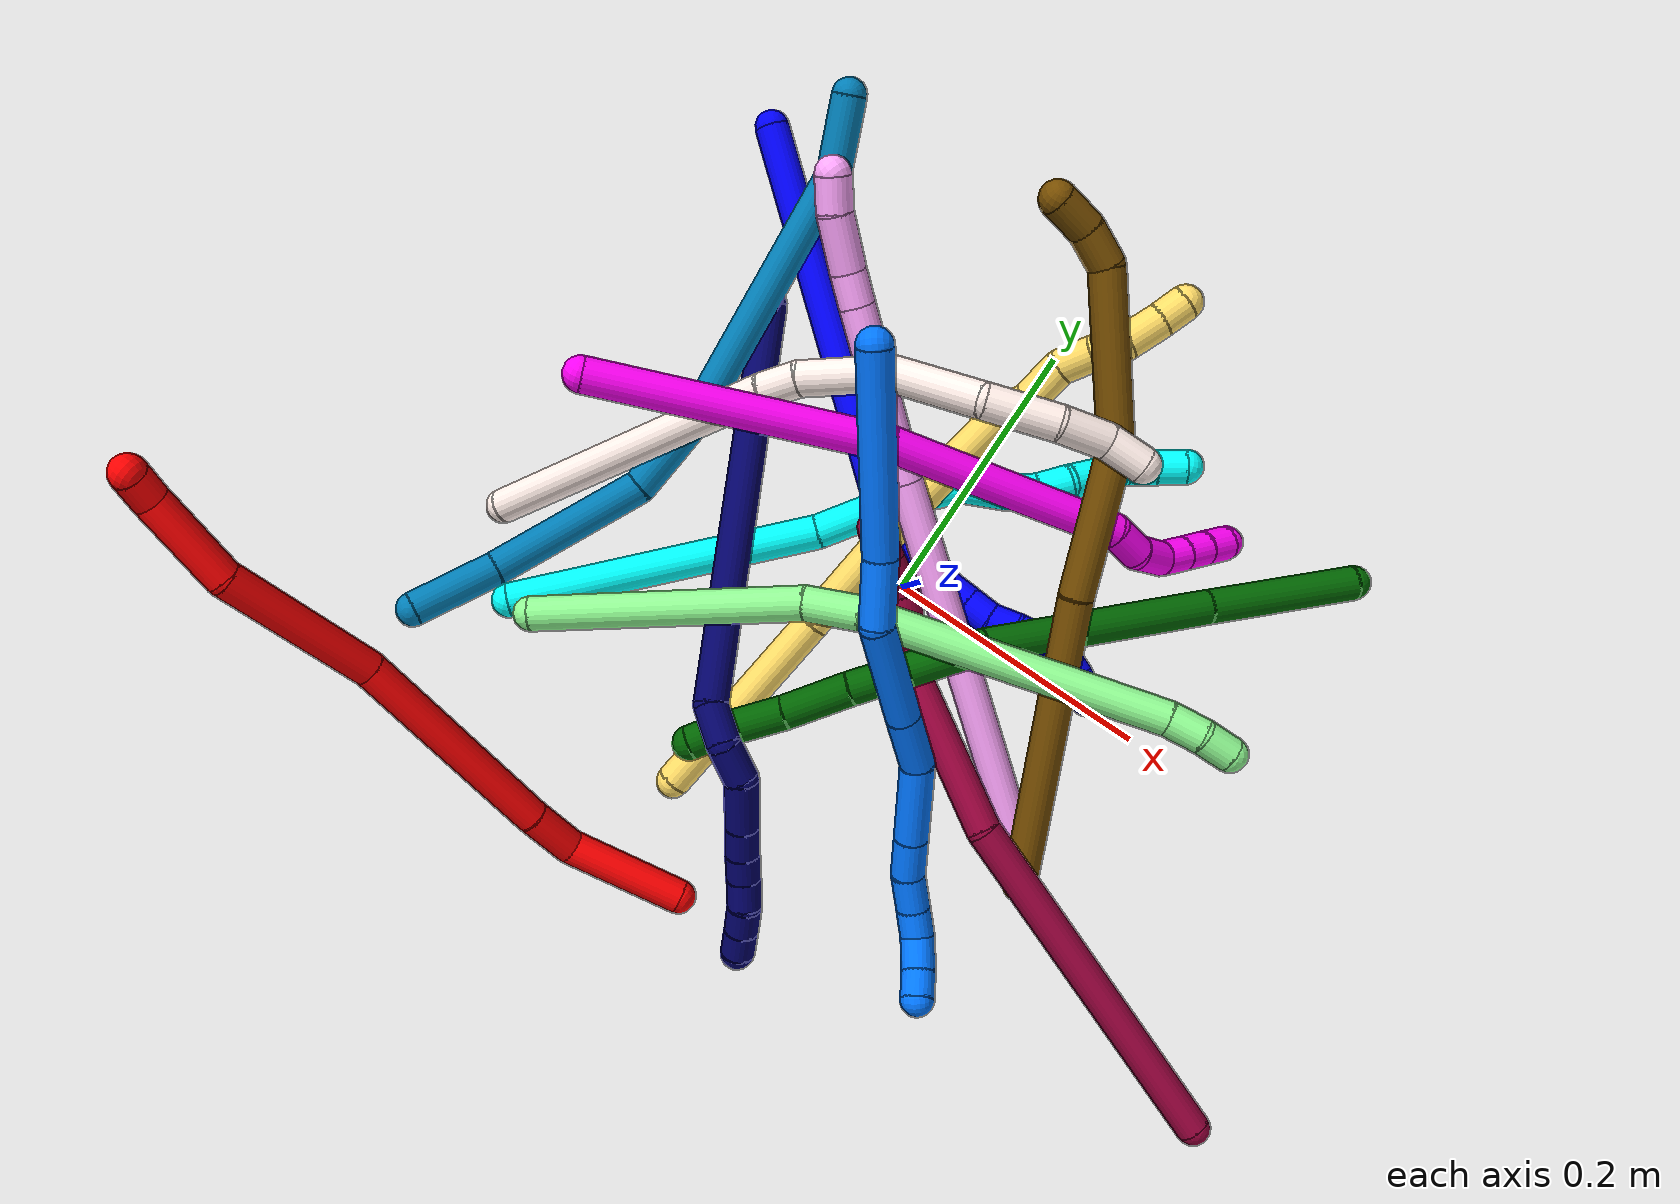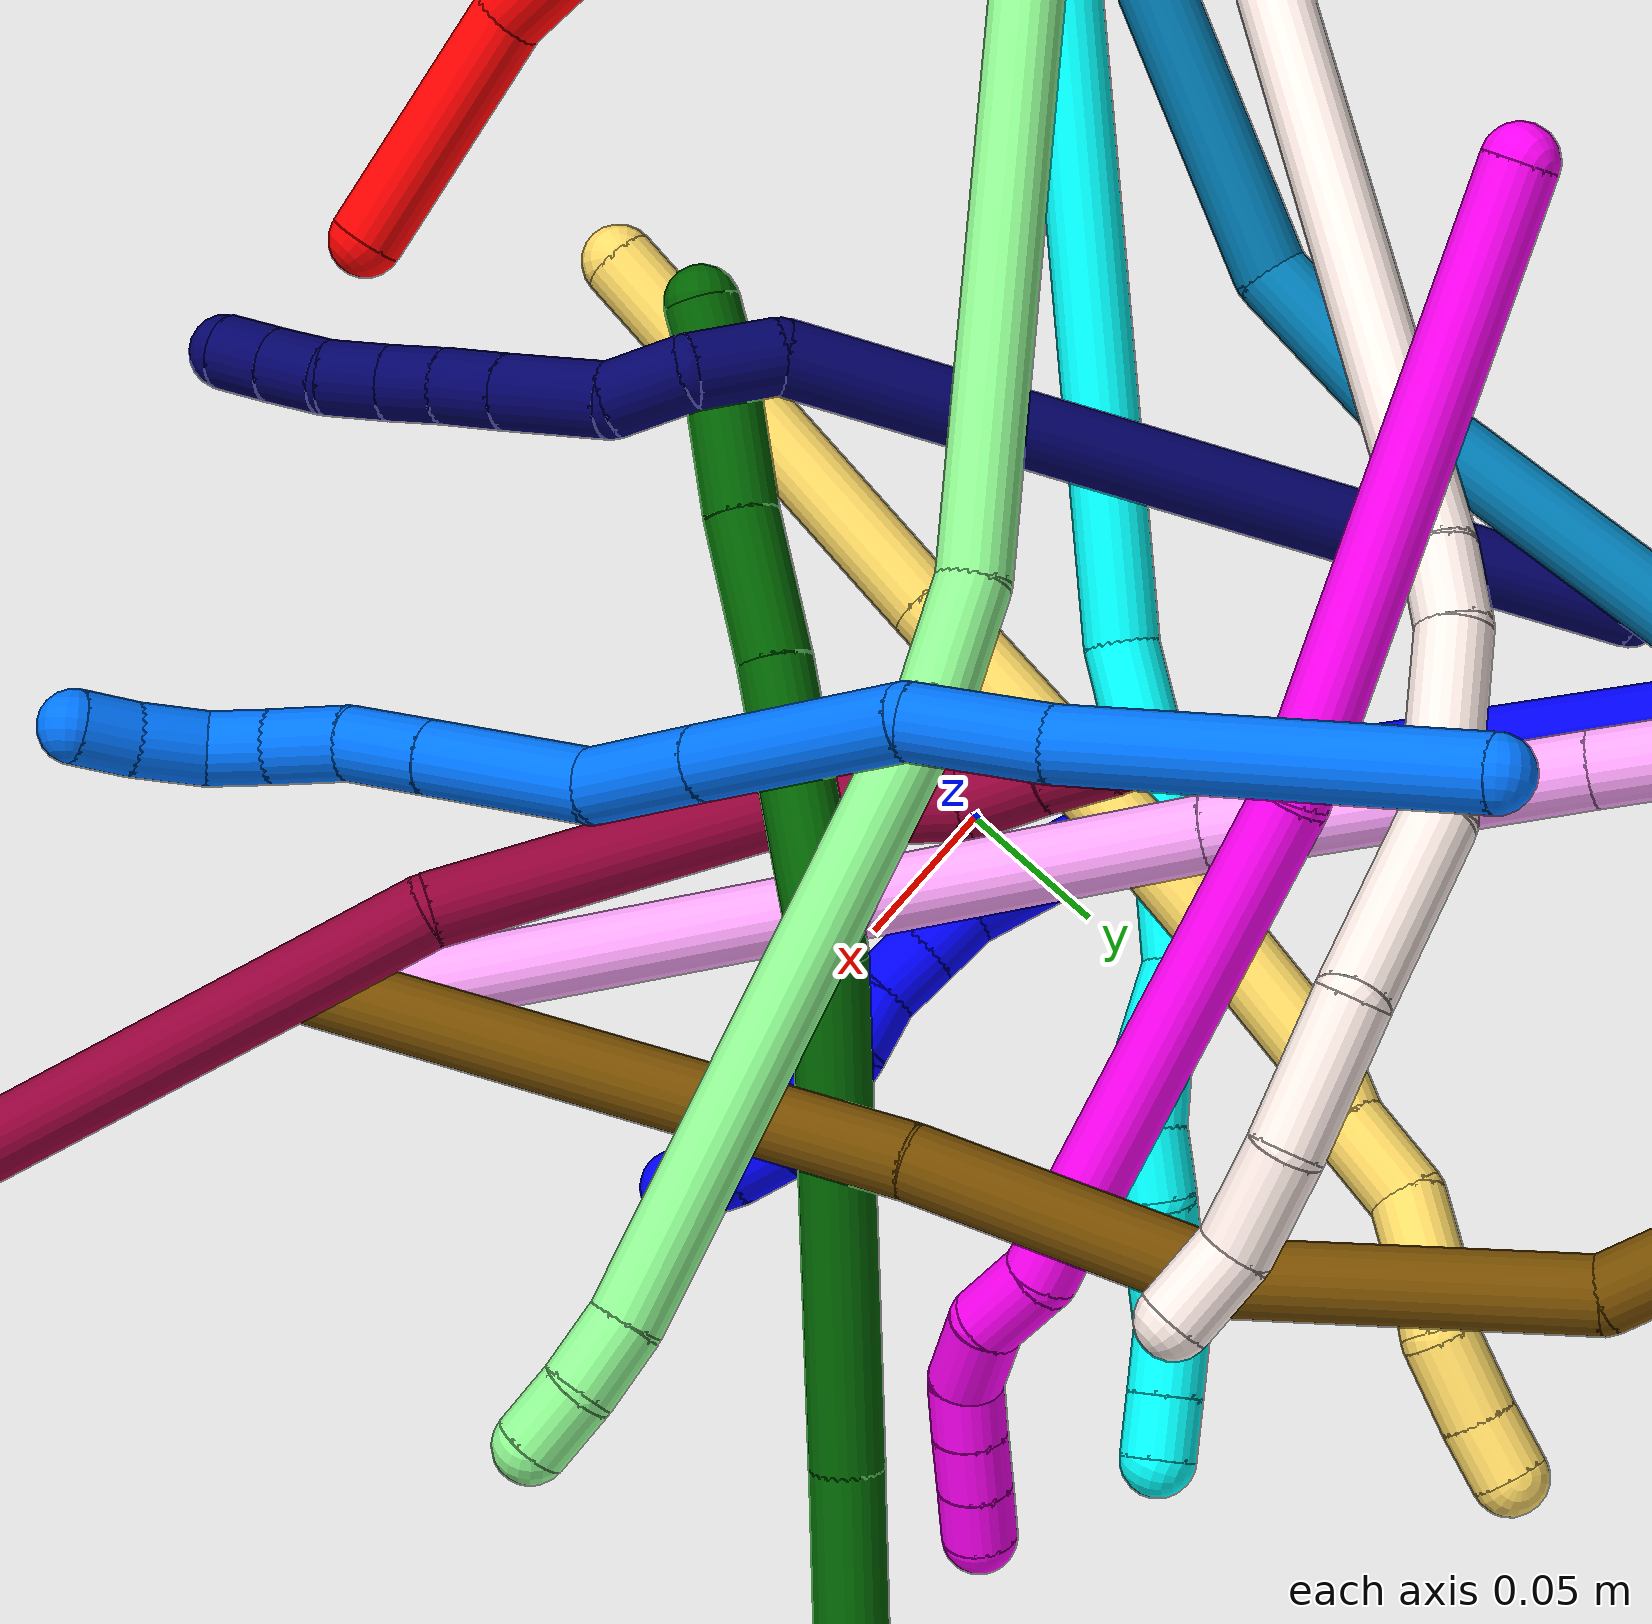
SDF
<sdf version="1.7">
 <world name="default">
  <plugin name="TubeGeneratorPlugin" filename="libtube_generator_plugin.so"/>
  <model name="photoneo_s_sensor">
   <static>1</static>
   <pose>0 0 2 1.57079 1.57079 3.14159</pose>
   <link name="link">
    <inertial><mass>0.1</mass></inertial>
    <sensor name="sensor" type="depth">
     <update_rate>30</update_rate>
     <camera>
      <horizontal_fov>1.22</horizontal_fov>
      <image><width>1920</width><height>1200</height><format>B8G8R8</format></image>
      <clip><near>0.1</near><far>4</far></clip>
      <depth_camera><output>points</output></depth_camera>
     </camera>
     <plugin name="camera_plugin" filename="libgazebo_ros_depth_camera.so">
      <baseline>0.2</baseline>
      <alwaysOn>1</alwaysOn>
      <updateRate>0.0</updateRate>
      <cameraName>camera_ir</cameraName>
      <imageTopicName>/camera/color/image_raw</imageTopicName>
      <cameraInfoTopicName>/camera/color/camera_info</cameraInfoTopicName>
      <depthImageTopicName>/camera/depth/image_raw</depthImageTopicName>
      <depthImageCameraInfoTopicName>/camera/depth/camera_info</depthImageCameraInfoTopicName>
      <pointCloudTopicName>/camera/depth/points</pointCloudTopicName>
      <frameName>fr_optical</frameName>
      <pointCloudCutoff>0.1</pointCloudCutoff>
      <pointCloudCutoffMax>2.0</pointCloudCutoffMax>
      <distortionK1>0</distortionK1>
      <distortionK2>0</distortionK2>
      <distortionK3>0</distortionK3>
      <distortionT1>0</distortionT1>
      <distortionT2>0</distortionT2>
      <CxPrime>0</CxPrime>
      <Cx>0</Cx>
      <Cy>0</Cy>
      <focalLength>0</focalLength>
      <hackBaseline>0</hackBaseline>
     </plugin>
    </sensor>
   </link>
  </model>
  <gravity>0 0 -9.8</gravity>
  <magnetic_field>6e-06 2.3e-05 -4.2e-05</magnetic_field>
  <atmosphere type="adiabatic"/>
  <physics name="default_physics" default="0" type="ode">
   <max_step_size>0.003</max_step_size>
   <real_time_factor>1</real_time_factor>
   <real_time_update_rate>1000</real_time_update_rate>
   <max_contacts>10000</max_contacts>
   <ode>
    <solver>
     <type>quick</type>
     <iters>100</iters>
     <sor>1.3</sor>
     <use_dynamic_moi_rescaling>0</use_dynamic_moi_rescaling>
    </solver>
    <constraints>
     <contact_max_correcting_vel>0</contact_max_correcting_vel>
     <contact_surface_layer>0.001</contact_surface_layer>
     <cfm>0</cfm>
     <erp>0.2</erp>
    </constraints>
   </ode>
  </physics>
  <scene><ambient>0.4 0.4 0.4 1</ambient><background>0.7 0.7 0.7 1</background><shadows>0</shadows></scene>
  <audio><device>default</device></audio>
  <spherical_coordinates>
   <surface_model>EARTH_WGS84</surface_model>
   <latitude_deg>0</latitude_deg>
   <longitude_deg>0</longitude_deg>
   <elevation>0</elevation>
   <heading_deg>0</heading_deg>
  </spherical_coordinates>
  <model name="bin">
   <static>1</static>
   <link name="bottom">
    <collision name="collision-bottom">
     <pose>0 0 -0.01 0 -0 0</pose>
     <geometry><box><size>0.8 0.6 0.02</size></box></geometry>
     <surface>
      <friction><ode><mu>100</mu><mu2>100</mu2></ode></friction>
      <contact><collide_bitmask>65535</collide_bitmask></contact>
     </surface>
    </collision>
   </link>
   <link name="west_wall">
    <collision name="collision-west_wall">
     <pose>-0.41 0 0.1 0 -0 0</pose>
     <geometry><box><size>0.02 0.6 0.2</size></box></geometry>
     <surface>
      <friction><ode><mu>100</mu><mu2>100</mu2></ode></friction>
      <contact><collide_bitmask>65535</collide_bitmask></contact>
     </surface>
    </collision>
   </link>
   <link name="east_wall">
    <collision name="collision-east_wall">
     <pose>0.41 0 0.1 0 -0 0</pose>
     <geometry><box><size>0.02 0.6 0.2</size></box></geometry>
     <surface>
      <friction><ode><mu>100</mu><mu2>100</mu2></ode></friction>
      <contact><collide_bitmask>65535</collide_bitmask></contact>
     </surface>
    </collision>
   </link>
   <link name="south_wall">
    <collision name="collision-south_wall">
     <pose>0 -0.31 0.1 0 -0 0</pose>
     <geometry><box><size>0.8 0.02 0.2</size></box></geometry>
     <surface>
      <friction><ode><mu>100</mu><mu2>100</mu2></ode></friction>
      <contact><collide_bitmask>65535</collide_bitmask></contact>
     </surface>
    </collision>
   </link>
   <link name="north_wall">
    <collision name="collision-north_wall">
     <pose>0 0.31 0.1 0 -0 0</pose>
     <geometry><box><size>0.8 0.02 0.2</size></box></geometry>
     <surface>
      <friction><ode><mu>100</mu><mu2>100</mu2></ode></friction>
      <contact><collide_bitmask>65535</collide_bitmask></contact>
     </surface>
    </collision>
   </link>
  </model>
  <model name="1">
   <static>0</static>
   <link name="1">
    <collision name="collision-cylinder-e_1_1_4">
     <pose>0.107219 -0.080087 -0.046219 2.09421 0.85914 1.34126</pose>
     <geometry><cylinder><radius>0.0125</radius><length>0.283168</length></cylinder></geometry>
     <surface>
      <friction><ode><mu>1.16</mu><mu2>1.16</mu2><slip1>0</slip1><slip2>0</slip2></ode></friction>
      <contact><ode><kp>1e+06</kp><kd>1</kd><max_vel>0</max_vel><min_depth>0.001</min_depth></ode></contact>
     </surface>
    </collision>
    <visual name="visual-cylinder-e_1_1_4">
     <pose>0.107219 -0.080087 -0.046219 2.09421 0.85914 1.34126</pose>
     <geometry><cylinder><radius>0.0125</radius><length>0.283168</length></cylinder></geometry>
     <material><ambient>0 0 1 1</ambient></material>
    </visual>
    <collision name="collision-cylinder-e_2_4_5">
     <pose>0.228446 -0.164963 -0.092444 1.57216 1.24144 1.24273</pose>
     <geometry><cylinder><radius>0.0125</radius><length>0.029607</length></cylinder></geometry>
     <surface>
      <friction><ode><mu>1.16</mu><mu2>1.16</mu2><slip1>0</slip1><slip2>0</slip2></ode></friction>
      <contact><ode><kp>1e+06</kp><kd>1</kd><max_vel>0</max_vel><min_depth>0.001</min_depth></ode></contact>
     </surface>
    </collision>
    <visual name="visual-cylinder-e_2_4_5">
     <pose>0.228446 -0.164963 -0.092444 1.57216 1.24144 1.24273</pose>
     <geometry><cylinder><radius>0.0125</radius><length>0.029607</length></cylinder></geometry>
     <material><ambient>0 0 1 1</ambient></material>
    </visual>
    <collision name="collision-cylinder-e_3_5_6">
     <pose>0.263669 -0.179963 -0.092719 1.59712 1.12204 1.14589</pose>
     <geometry><cylinder><radius>0.0125</radius><length>0.047092</length></cylinder></geometry>
     <surface>
      <friction><ode><mu>1.16</mu><mu2>1.16</mu2><slip1>0</slip1><slip2>0</slip2></ode></friction>
      <contact><ode><kp>1e+06</kp><kd>1</kd><max_vel>0</max_vel><min_depth>0.001</min_depth></ode></contact>
     </surface>
    </collision>
    <visual name="visual-cylinder-e_3_5_6">
     <pose>0.263669 -0.179963 -0.092719 1.59712 1.12204 1.14589</pose>
     <geometry><cylinder><radius>0.0125</radius><length>0.047092</length></cylinder></geometry>
     <material><ambient>0 0 1 1</ambient></material>
    </visual>
    <collision name="collision-cylinder-e_4_6_7">
     <pose>0.294527 -0.19232 -0.091417 0.938752 1.30176 0.73722</pose>
     <geometry><cylinder><radius>0.0125</radius><length>0.020007</length></cylinder></geometry>
     <surface>
      <friction><ode><mu>1.16</mu><mu2>1.16</mu2><slip1>0</slip1><slip2>0</slip2></ode></friction>
      <contact><ode><kp>1e+06</kp><kd>1</kd><max_vel>0</max_vel><min_depth>0.001</min_depth></ode></contact>
     </surface>
    </collision>
    <visual name="visual-cylinder-e_4_6_7">
     <pose>0.294527 -0.19232 -0.091417 0.938752 1.30176 0.73722</pose>
     <geometry><cylinder><radius>0.0125</radius><length>0.020007</length></cylinder></geometry>
     <material><ambient>0 0 1 1</ambient></material>
    </visual>
    <collision name="collision-cylinder-e_5_7_8">
     <pose>0.313633 -0.197028 -0.087871 0.914163 1.24128 0.676179</pose>
     <geometry><cylinder><radius>0.0125</radius><length>0.020001</length></cylinder></geometry>
     <surface>
      <friction><ode><mu>1.16</mu><mu2>1.16</mu2><slip1>0</slip1><slip2>0</slip2></ode></friction>
      <contact><ode><kp>1e+06</kp><kd>1</kd><max_vel>0</max_vel><min_depth>0.001</min_depth></ode></contact>
     </surface>
    </collision>
    <visual name="visual-cylinder-e_5_7_8">
     <pose>0.313633 -0.197028 -0.087871 0.914163 1.24128 0.676179</pose>
     <geometry><cylinder><radius>0.0125</radius><length>0.020001</length></cylinder></geometry>
     <material><ambient>0 0 1 1</ambient></material>
    </visual>
    <collision name="collision-cylinder-e_6_8_9">
     <pose>0.332441 -0.19974 -0.082295 0.041125 1.20285 0.028223</pose>
     <geometry><cylinder><radius>0.0125</radius><length>0.020032</length></cylinder></geometry>
     <surface>
      <friction><ode><mu>1.16</mu><mu2>1.16</mu2><slip1>0</slip1><slip2>0</slip2></ode></friction>
      <contact><ode><kp>1e+06</kp><kd>1</kd><max_vel>0</max_vel><min_depth>0.001</min_depth></ode></contact>
     </surface>
    </collision>
    <visual name="visual-cylinder-e_6_8_9">
     <pose>0.332441 -0.19974 -0.082295 0.041125 1.20285 0.028223</pose>
     <geometry><cylinder><radius>0.0125</radius><length>0.020032</length></cylinder></geometry>
     <material><ambient>0 0 1 1</ambient></material>
    </visual>
    <collision name="collision-cylinder-e_7_9_10">
     <pose>0.351657 -0.199082 -0.077279 -0.517082 1.40718 -0.441449</pose>
     <geometry><cylinder><radius>0.0125</radius><length>0.020006</length></cylinder></geometry>
     <surface>
      <friction><ode><mu>1.16</mu><mu2>1.16</mu2><slip1>0</slip1><slip2>0</slip2></ode></friction>
      <contact><ode><kp>1e+06</kp><kd>1</kd><max_vel>0</max_vel><min_depth>0.001</min_depth></ode></contact>
     </surface>
    </collision>
    <visual name="visual-cylinder-e_7_9_10">
     <pose>0.351657 -0.199082 -0.077279 -0.517082 1.40718 -0.441449</pose>
     <geometry><cylinder><radius>0.0125</radius><length>0.020006</length></cylinder></geometry>
     <material><ambient>0 0 1 1</ambient></material>
    </visual>
    <collision name="collision-cylinder-e_8_10_11">
     <pose>0.370722 -0.195484 -0.078632 -2.35196 1.16668 -2.01521</pose>
     <geometry><cylinder><radius>0.0125</radius><length>0.020003</length></cylinder></geometry>
     <surface>
      <friction><ode><mu>1.16</mu><mu2>1.16</mu2><slip1>0</slip1><slip2>0</slip2></ode></friction>
      <contact><ode><kp>1e+06</kp><kd>1</kd><max_vel>0</max_vel><min_depth>0.001</min_depth></ode></contact>
     </surface>
    </collision>
    <visual name="visual-cylinder-e_8_10_11">
     <pose>0.370722 -0.195484 -0.078632 -2.35196 1.16668 -2.01521</pose>
     <geometry><cylinder><radius>0.0125</radius><length>0.020003</length></cylinder></geometry>
     <material><ambient>0 0 1 1</ambient></material>
    </visual>
    <collision name="collision-cylinder-e_9_11_12">
     <pose>0.389088 -0.193902 -0.085246 2.83671 1.15661 2.67929</pose>
     <geometry><cylinder><radius>0.0125</radius><length>0.020034</length></cylinder></geometry>
     <surface>
      <friction><ode><mu>1.16</mu><mu2>1.16</mu2><slip1>0</slip1><slip2>0</slip2></ode></friction>
      <contact><ode><kp>1e+06</kp><kd>1</kd><max_vel>0</max_vel><min_depth>0.001</min_depth></ode></contact>
     </surface>
    </collision>
    <visual name="visual-cylinder-e_9_11_12">
     <pose>0.389088 -0.193902 -0.085246 2.83671 1.15661 2.67929</pose>
     <geometry><cylinder><radius>0.0125</radius><length>0.020034</length></cylinder></geometry>
     <material><ambient>0 0 1 1</ambient></material>
    </visual>
    <collision name="collision-cylinder-e_10_12_2">
     <pose>0.406866 -0.199441 -0.091856 2.13908 1.03283 1.60642</pose>
     <geometry><cylinder><radius>0.0125</radius><length>0.020048</length></cylinder></geometry>
     <surface>
      <friction><ode><mu>1.16</mu><mu2>1.16</mu2><slip1>0</slip1><slip2>0</slip2></ode></friction>
      <contact><ode><kp>1e+06</kp><kd>1</kd><max_vel>0</max_vel><min_depth>0.001</min_depth></ode></contact>
     </surface>
    </collision>
    <visual name="visual-cylinder-e_10_12_2">
     <pose>0.406866 -0.199441 -0.091856 2.13908 1.03283 1.60642</pose>
     <geometry><cylinder><radius>0.0125</radius><length>0.020048</length></cylinder></geometry>
     <material><ambient>0 0 1 1</ambient></material>
    </visual>
    <collision name="collision-sphere-2">
     <pose>0.415475 -0.20377 -0.09462 0 -0 0</pose>
     <geometry><sphere><radius>0.0125</radius></sphere></geometry>
     <surface>
      <friction><ode><mu>1.16</mu><mu2>1.16</mu2><slip1>0</slip1><slip2>0</slip2></ode></friction>
      <contact><ode><kp>1e+06</kp><kd>1</kd><max_vel>0</max_vel><min_depth>0.001</min_depth></ode></contact>
     </surface>
    </collision>
    <visual name="visual-sphere-2">
     <pose>0.415475 -0.20377 -0.09462 0 -0 0</pose>
     <geometry><sphere><radius>0.0125</radius></sphere></geometry>
     <material><ambient>0 0 1 1</ambient></material>
    </visual>
    <collision name="collision-sphere-12">
     <pose>0.398258 -0.195112 -0.089092 0 -0 0</pose>
     <geometry><sphere><radius>0.0125</radius></sphere></geometry>
     <surface>
      <friction><ode><mu>1.16</mu><mu2>1.16</mu2><slip1>0</slip1><slip2>0</slip2></ode></friction>
      <contact><ode><kp>1e+06</kp><kd>1</kd><max_vel>0</max_vel><min_depth>0.001</min_depth></ode></contact>
     </surface>
    </collision>
    <visual name="visual-sphere-12">
     <pose>0.398258 -0.195112 -0.089092 0 -0 0</pose>
     <geometry><sphere><radius>0.0125</radius></sphere></geometry>
     <material><ambient>0 0 1 1</ambient></material>
    </visual>
    <collision name="collision-sphere-11">
     <pose>0.379918 -0.192692 -0.081401 0 -0 0</pose>
     <geometry><sphere><radius>0.0125</radius></sphere></geometry>
     <surface>
      <friction><ode><mu>1.16</mu><mu2>1.16</mu2><slip1>0</slip1><slip2>0</slip2></ode></friction>
      <contact><ode><kp>1e+06</kp><kd>1</kd><max_vel>0</max_vel><min_depth>0.001</min_depth></ode></contact>
     </surface>
    </collision>
    <visual name="visual-sphere-11">
     <pose>0.379918 -0.192692 -0.081401 0 -0 0</pose>
     <geometry><sphere><radius>0.0125</radius></sphere></geometry>
     <material><ambient>0 0 1 1</ambient></material>
    </visual>
    <collision name="collision-sphere-10">
     <pose>0.361526 -0.198277 -0.075863 0 -0 0</pose>
     <geometry><sphere><radius>0.0125</radius></sphere></geometry>
     <surface>
      <friction><ode><mu>1.16</mu><mu2>1.16</mu2><slip1>0</slip1><slip2>0</slip2></ode></friction>
      <contact><ode><kp>1e+06</kp><kd>1</kd><max_vel>0</max_vel><min_depth>0.001</min_depth></ode></contact>
     </surface>
    </collision>
    <visual name="visual-sphere-10">
     <pose>0.361526 -0.198277 -0.075863 0 -0 0</pose>
     <geometry><sphere><radius>0.0125</radius></sphere></geometry>
     <material><ambient>0 0 1 1</ambient></material>
    </visual>
    <collision name="collision-sphere-9">
     <pose>0.341787 -0.199888 -0.078696 0 -0 0</pose>
     <geometry><sphere><radius>0.0125</radius></sphere></geometry>
     <surface>
      <friction><ode><mu>1.16</mu><mu2>1.16</mu2><slip1>0</slip1><slip2>0</slip2></ode></friction>
      <contact><ode><kp>1e+06</kp><kd>1</kd><max_vel>0</max_vel><min_depth>0.001</min_depth></ode></contact>
     </surface>
    </collision>
    <visual name="visual-sphere-9">
     <pose>0.341787 -0.199888 -0.078696 0 -0 0</pose>
     <geometry><sphere><radius>0.0125</radius></sphere></geometry>
     <material><ambient>0 0 1 1</ambient></material>
    </visual>
    <collision name="collision-sphere-4">
     <pose>0.214438 -0.160175 -0.092437 0 -0 0</pose>
     <geometry><sphere><radius>0.0125</radius></sphere></geometry>
     <surface>
      <friction><ode><mu>1.16</mu><mu2>1.16</mu2><slip1>0</slip1><slip2>0</slip2></ode></friction>
      <contact><ode><kp>1e+06</kp><kd>1</kd><max_vel>0</max_vel><min_depth>0.001</min_depth></ode></contact>
     </surface>
    </collision>
    <visual name="visual-sphere-4">
     <pose>0.214438 -0.160175 -0.092437 0 -0 0</pose>
     <geometry><sphere><radius>0.0125</radius></sphere></geometry>
     <material><ambient>0 0 1 1</ambient></material>
    </visual>
    <collision name="collision-sphere-1">
     <geometry><sphere><radius>0.0125</radius></sphere></geometry>
     <surface>
      <friction><ode><mu>1.16</mu><mu2>1.16</mu2><slip1>0</slip1><slip2>0</slip2></ode></friction>
      <contact><ode><kp>1e+06</kp><kd>1</kd><max_vel>0</max_vel><min_depth>0.001</min_depth></ode></contact>
     </surface>
    </collision>
    <visual name="visual-sphere-1">
     <geometry><sphere><radius>0.0125</radius></sphere></geometry>
     <material><ambient>0 0 1 1</ambient></material>
    </visual>
    <collision name="collision-sphere-8">
     <pose>0.323096 -0.199591 -0.085895 0 -0 0</pose>
     <geometry><sphere><radius>0.0125</radius></sphere></geometry>
     <surface>
      <friction><ode><mu>1.16</mu><mu2>1.16</mu2><slip1>0</slip1><slip2>0</slip2></ode></friction>
      <contact><ode><kp>1e+06</kp><kd>1</kd><max_vel>0</max_vel><min_depth>0.001</min_depth></ode></contact>
     </surface>
    </collision>
    <visual name="visual-sphere-8">
     <pose>0.323096 -0.199591 -0.085895 0 -0 0</pose>
     <geometry><sphere><radius>0.0125</radius></sphere></geometry>
     <material><ambient>0 0 1 1</ambient></material>
    </visual>
    <collision name="collision-sphere-5">
     <pose>0.242454 -0.169751 -0.09245 0 -0 0</pose>
     <geometry><sphere><radius>0.0125</radius></sphere></geometry>
     <surface>
      <friction><ode><mu>1.16</mu><mu2>1.16</mu2><slip1>0</slip1><slip2>0</slip2></ode></friction>
      <contact><ode><kp>1e+06</kp><kd>1</kd><max_vel>0</max_vel><min_depth>0.001</min_depth></ode></contact>
     </surface>
    </collision>
    <visual name="visual-sphere-5">
     <pose>0.242454 -0.169751 -0.09245 0 -0 0</pose>
     <geometry><sphere><radius>0.0125</radius></sphere></geometry>
     <material><ambient>0 0 1 1</ambient></material>
    </visual>
    <collision name="collision-sphere-6">
     <pose>0.284884 -0.190175 -0.092988 0 -0 0</pose>
     <geometry><sphere><radius>0.0125</radius></sphere></geometry>
     <surface>
      <friction><ode><mu>1.16</mu><mu2>1.16</mu2><slip1>0</slip1><slip2>0</slip2></ode></friction>
      <contact><ode><kp>1e+06</kp><kd>1</kd><max_vel>0</max_vel><min_depth>0.001</min_depth></ode></contact>
     </surface>
    </collision>
    <visual name="visual-sphere-6">
     <pose>0.284884 -0.190175 -0.092988 0 -0 0</pose>
     <geometry><sphere><radius>0.0125</radius></sphere></geometry>
     <material><ambient>0 0 1 1</ambient></material>
    </visual>
    <collision name="collision-sphere-7">
     <pose>0.304171 -0.194465 -0.089846 0 -0 0</pose>
     <geometry><sphere><radius>0.0125</radius></sphere></geometry>
     <surface>
      <friction><ode><mu>1.16</mu><mu2>1.16</mu2><slip1>0</slip1><slip2>0</slip2></ode></friction>
      <contact><ode><kp>1e+06</kp><kd>1</kd><max_vel>0</max_vel><min_depth>0.001</min_depth></ode></contact>
     </surface>
    </collision>
    <visual name="visual-sphere-7">
     <pose>0.304171 -0.194465 -0.089846 0 -0 0</pose>
     <geometry><sphere><radius>0.0125</radius></sphere></geometry>
     <material><ambient>0 0 1 1</ambient></material>
    </visual>
    <inertial>
     <pose>0.197539 -0.127206 -0.064189 0 -0 0</pose>
     <mass>0.5</mass>
     <inertia>
      <ixx>0.001535</ixx>
      <ixy>0</ixy>
      <ixz>0</ixz>
      <iyy>0.002221</iyy>
      <iyz>0</iyz>
      <izz>-0.000388</izz>
     </inertia>
    </inertial>
   </link>
   <pose>-0.263751 0.223493 0.014014 -0.632983 0.105794 0.008427</pose>
  </model>
  <model name="2">
   <static>0</static>
   <link name="2">
    <collision name="collision-cylinder-e_1_1_4">
     <pose>-0.01053 0.004297 -0.041858 -3.03931 -0.245202 2.35414</pose>
     <geometry><cylinder><radius>0.0125</radius><length>0.086751</length></cylinder></geometry>
     <surface>
      <friction><ode><mu>1.16</mu><mu2>1.16</mu2><slip1>0</slip1><slip2>0</slip2></ode></friction>
      <contact><ode><kp>1e+06</kp><kd>1</kd><max_vel>0</max_vel><min_depth>0.001</min_depth></ode></contact>
     </surface>
    </collision>
    <visual name="visual-cylinder-e_1_1_4">
     <pose>-0.01053 0.004297 -0.041858 -3.03931 -0.245202 2.35414</pose>
     <geometry><cylinder><radius>0.0125</radius><length>0.086751</length></cylinder></geometry>
     <material><ambient>1 0 0 1</ambient></material>
    </visual>
    <collision name="collision-cylinder-e_2_4_5">
     <pose>-0.023011 0.019916 -0.100643 -2.552 -0.095557 0.312376</pose>
     <geometry><cylinder><radius>0.0125</radius><length>0.040917</length></cylinder></geometry>
     <surface>
      <friction><ode><mu>1.16</mu><mu2>1.16</mu2><slip1>0</slip1><slip2>0</slip2></ode></friction>
      <contact><ode><kp>1e+06</kp><kd>1</kd><max_vel>0</max_vel><min_depth>0.001</min_depth></ode></contact>
     </surface>
    </collision>
    <visual name="visual-cylinder-e_2_4_5">
     <pose>-0.023011 0.019916 -0.100643 -2.552 -0.095557 0.312376</pose>
     <geometry><cylinder><radius>0.0125</radius><length>0.040917</length></cylinder></geometry>
     <material><ambient>1 0 0 1</ambient></material>
    </visual>
    <collision name="collision-cylinder-e_3_5_6">
     <pose>-0.027367 0.073064 -0.187672 -2.60366 -0.029442 0.106718</pose>
     <geometry><cylinder><radius>0.0125</radius><length>0.163332</length></cylinder></geometry>
     <surface>
      <friction><ode><mu>1.16</mu><mu2>1.16</mu2><slip1>0</slip1><slip2>0</slip2></ode></friction>
      <contact><ode><kp>1e+06</kp><kd>1</kd><max_vel>0</max_vel><min_depth>0.001</min_depth></ode></contact>
     </surface>
    </collision>
    <visual name="visual-cylinder-e_3_5_6">
     <pose>-0.027367 0.073064 -0.187672 -2.60366 -0.029442 0.106718</pose>
     <geometry><cylinder><radius>0.0125</radius><length>0.163332</length></cylinder></geometry>
     <material><ambient>1 0 0 1</ambient></material>
    </visual>
    <collision name="collision-cylinder-e_4_6_7">
     <pose>-0.041972 0.148427 -0.304797 -2.52204 -0.208171 0.630934</pose>
     <geometry><cylinder><radius>0.0125</radius><length>0.118066</length></cylinder></geometry>
     <surface>
      <friction><ode><mu>1.16</mu><mu2>1.16</mu2><slip1>0</slip1><slip2>0</slip2></ode></friction>
      <contact><ode><kp>1e+06</kp><kd>1</kd><max_vel>0</max_vel><min_depth>0.001</min_depth></ode></contact>
     </surface>
    </collision>
    <visual name="visual-cylinder-e_4_6_7">
     <pose>-0.041972 0.148427 -0.304797 -2.52204 -0.208171 0.630934</pose>
     <geometry><cylinder><radius>0.0125</radius><length>0.118066</length></cylinder></geometry>
     <material><ambient>1 0 0 1</ambient></material>
    </visual>
    <collision name="collision-cylinder-e_5_7_8">
     <pose>-0.051853 0.197434 -0.380897 -2.65269 0.070298 -0.280091</pose>
     <geometry><cylinder><radius>0.0125</radius><length>0.066034</length></cylinder></geometry>
     <surface>
      <friction><ode><mu>1.16</mu><mu2>1.16</mu2><slip1>0</slip1><slip2>0</slip2></ode></friction>
      <contact><ode><kp>1e+06</kp><kd>1</kd><max_vel>0</max_vel><min_depth>0.001</min_depth></ode></contact>
     </surface>
    </collision>
    <visual name="visual-cylinder-e_5_7_8">
     <pose>-0.051853 0.197434 -0.380897 -2.65269 0.070298 -0.280091</pose>
     <geometry><cylinder><radius>0.0125</radius><length>0.066034</length></cylinder></geometry>
     <material><ambient>1 0 0 1</ambient></material>
    </visual>
    <collision name="collision-cylinder-e_6_8_2">
     <pose>-0.049495 0.223406 -0.416659 -2.13765 0.003121 -0.005686</pose>
     <geometry><cylinder><radius>0.0125</radius><length>0.024901</length></cylinder></geometry>
     <surface>
      <friction><ode><mu>1.16</mu><mu2>1.16</mu2><slip1>0</slip1><slip2>0</slip2></ode></friction>
      <contact><ode><kp>1e+06</kp><kd>1</kd><max_vel>0</max_vel><min_depth>0.001</min_depth></ode></contact>
     </surface>
    </collision>
    <visual name="visual-cylinder-e_6_8_2">
     <pose>-0.049495 0.223406 -0.416659 -2.13765 0.003121 -0.005686</pose>
     <geometry><cylinder><radius>0.0125</radius><length>0.024901</length></cylinder></geometry>
     <material><ambient>1 0 0 1</ambient></material>
    </visual>
    <collision name="collision-sphere-2">
     <pose>-0.049456 0.233909 -0.423345 0 -0 0</pose>
     <geometry><sphere><radius>0.0125</radius></sphere></geometry>
     <surface>
      <friction><ode><mu>1.16</mu><mu2>1.16</mu2><slip1>0</slip1><slip2>0</slip2></ode></friction>
      <contact><ode><kp>1e+06</kp><kd>1</kd><max_vel>0</max_vel><min_depth>0.001</min_depth></ode></contact>
     </surface>
    </collision>
    <visual name="visual-sphere-2">
     <pose>-0.049456 0.233909 -0.423345 0 -0 0</pose>
     <geometry><sphere><radius>0.0125</radius></sphere></geometry>
     <material><ambient>1 0 0 1</ambient></material>
    </visual>
    <collision name="collision-sphere-4">
     <pose>-0.021059 0.008593 -0.083717 0 -0 0</pose>
     <geometry><sphere><radius>0.0125</radius></sphere></geometry>
     <surface>
      <friction><ode><mu>1.16</mu><mu2>1.16</mu2><slip1>0</slip1><slip2>0</slip2></ode></friction>
      <contact><ode><kp>1e+06</kp><kd>1</kd><max_vel>0</max_vel><min_depth>0.001</min_depth></ode></contact>
     </surface>
    </collision>
    <visual name="visual-sphere-4">
     <pose>-0.021059 0.008593 -0.083717 0 -0 0</pose>
     <geometry><sphere><radius>0.0125</radius></sphere></geometry>
     <material><ambient>1 0 0 1</ambient></material>
    </visual>
    <collision name="collision-sphere-1">
     <geometry><sphere><radius>0.0125</radius></sphere></geometry>
     <surface>
      <friction><ode><mu>1.16</mu><mu2>1.16</mu2><slip1>0</slip1><slip2>0</slip2></ode></friction>
      <contact><ode><kp>1e+06</kp><kd>1</kd><max_vel>0</max_vel><min_depth>0.001</min_depth></ode></contact>
     </surface>
    </collision>
    <visual name="visual-sphere-1">
     <geometry><sphere><radius>0.0125</radius></sphere></geometry>
     <material><ambient>1 0 0 1</ambient></material>
    </visual>
    <collision name="collision-sphere-8">
     <pose>-0.049534 0.212903 -0.409974 0 -0 0</pose>
     <geometry><sphere><radius>0.0125</radius></sphere></geometry>
     <surface>
      <friction><ode><mu>1.16</mu><mu2>1.16</mu2><slip1>0</slip1><slip2>0</slip2></ode></friction>
      <contact><ode><kp>1e+06</kp><kd>1</kd><max_vel>0</max_vel><min_depth>0.001</min_depth></ode></contact>
     </surface>
    </collision>
    <visual name="visual-sphere-8">
     <pose>-0.049534 0.212903 -0.409974 0 -0 0</pose>
     <geometry><sphere><radius>0.0125</radius></sphere></geometry>
     <material><ambient>1 0 0 1</ambient></material>
    </visual>
    <collision name="collision-sphere-5">
     <pose>-0.024963 0.03124 -0.11757 0 -0 0</pose>
     <geometry><sphere><radius>0.0125</radius></sphere></geometry>
     <surface>
      <friction><ode><mu>1.16</mu><mu2>1.16</mu2><slip1>0</slip1><slip2>0</slip2></ode></friction>
      <contact><ode><kp>1e+06</kp><kd>1</kd><max_vel>0</max_vel><min_depth>0.001</min_depth></ode></contact>
     </surface>
    </collision>
    <visual name="visual-sphere-5">
     <pose>-0.024963 0.03124 -0.11757 0 -0 0</pose>
     <geometry><sphere><radius>0.0125</radius></sphere></geometry>
     <material><ambient>1 0 0 1</ambient></material>
    </visual>
    <collision name="collision-sphere-6">
     <pose>-0.029771 0.114889 -0.257773 0 -0 0</pose>
     <geometry><sphere><radius>0.0125</radius></sphere></geometry>
     <surface>
      <friction><ode><mu>1.16</mu><mu2>1.16</mu2><slip1>0</slip1><slip2>0</slip2></ode></friction>
      <contact><ode><kp>1e+06</kp><kd>1</kd><max_vel>0</max_vel><min_depth>0.001</min_depth></ode></contact>
     </surface>
    </collision>
    <visual name="visual-sphere-6">
     <pose>-0.029771 0.114889 -0.257773 0 -0 0</pose>
     <geometry><sphere><radius>0.0125</radius></sphere></geometry>
     <material><ambient>1 0 0 1</ambient></material>
    </visual>
    <collision name="collision-sphere-7">
     <pose>-0.054172 0.181966 -0.35182 0 -0 0</pose>
     <geometry><sphere><radius>0.0125</radius></sphere></geometry>
     <surface>
      <friction><ode><mu>1.16</mu><mu2>1.16</mu2><slip1>0</slip1><slip2>0</slip2></ode></friction>
      <contact><ode><kp>1e+06</kp><kd>1</kd><max_vel>0</max_vel><min_depth>0.001</min_depth></ode></contact>
     </surface>
    </collision>
    <visual name="visual-sphere-7">
     <pose>-0.054172 0.181966 -0.35182 0 -0 0</pose>
     <geometry><sphere><radius>0.0125</radius></sphere></geometry>
     <material><ambient>1 0 0 1</ambient></material>
    </visual>
    <inertial>
     <pose>-0.031874 0.098492 -0.219831 0 -0 0</pose>
     <mass>0.5</mass>
     <inertia>
      <ixx>0.000626</ixx>
      <ixy>0</ixy>
      <ixz>0</ixz>
      <iyy>-0.000212</iyy>
      <iyz>0</iyz>
      <izz>-0.000274</izz>
     </inertia>
    </inertial>
   </link>
   <pose>-0.009931 -0.276519 0.011857 1.55467 0.360982 1.50251</pose>
  </model>
  <model name="3">
   <static>0</static>
   <link name="3">
    <collision name="collision-cylinder-e_1_1_4">
     <pose>0.063315 0.076719 0.054609 -0.952186 0.591928 -0.311913</pose>
     <geometry><cylinder><radius>0.0125</radius><length>0.226952</length></cylinder></geometry>
     <surface>
      <friction><ode><mu>1.16</mu><mu2>1.16</mu2><slip1>0</slip1><slip2>0</slip2></ode></friction>
      <contact><ode><kp>1e+06</kp><kd>1</kd><max_vel>0</max_vel><min_depth>0.001</min_depth></ode></contact>
     </surface>
    </collision>
    <visual name="visual-cylinder-e_1_1_4">
     <pose>0.063315 0.076719 0.054609 -0.952186 0.591928 -0.311913</pose>
     <geometry><cylinder><radius>0.0125</radius><length>0.226952</length></cylinder></geometry>
     <material><ambient>0.003922 1 0.996078 1</ambient></material>
    </visual>
    <collision name="collision-cylinder-e_2_4_5">
     <pose>0.146193 0.169407 0.131098 -0.630515 0.62547 -0.210132</pose>
     <geometry><cylinder><radius>0.0125</radius><length>0.066824</length></cylinder></geometry>
     <surface>
      <friction><ode><mu>1.16</mu><mu2>1.16</mu2><slip1>0</slip1><slip2>0</slip2></ode></friction>
      <contact><ode><kp>1e+06</kp><kd>1</kd><max_vel>0</max_vel><min_depth>0.001</min_depth></ode></contact>
     </surface>
    </collision>
    <visual name="visual-cylinder-e_2_4_5">
     <pose>0.146193 0.169407 0.131098 -0.630515 0.62547 -0.210132</pose>
     <geometry><cylinder><radius>0.0125</radius><length>0.066824</length></cylinder></geometry>
     <material><ambient>0.003922 1 0.996078 1</ambient></material>
    </visual>
    <collision name="collision-cylinder-e_3_5_6">
     <pose>0.180475 0.195434 0.164416 -0.721158 0.76829 -0.302511</pose>
     <geometry><cylinder><radius>0.0125</radius><length>0.042366</length></cylinder></geometry>
     <surface>
      <friction><ode><mu>1.16</mu><mu2>1.16</mu2><slip1>0</slip1><slip2>0</slip2></ode></friction>
      <contact><ode><kp>1e+06</kp><kd>1</kd><max_vel>0</max_vel><min_depth>0.001</min_depth></ode></contact>
     </surface>
    </collision>
    <visual name="visual-cylinder-e_3_5_6">
     <pose>0.180475 0.195434 0.164416 -0.721158 0.76829 -0.302511</pose>
     <geometry><cylinder><radius>0.0125</radius><length>0.042366</length></cylinder></geometry>
     <material><ambient>0.003922 1 0.996078 1</ambient></material>
    </visual>
    <collision name="collision-cylinder-e_4_6_7">
     <pose>0.208153 0.212789 0.178913 -1.17419 1.02265 -0.714612</pose>
     <geometry><cylinder><radius>0.0125</radius><length>0.030365</length></cylinder></geometry>
     <surface>
      <friction><ode><mu>1.16</mu><mu2>1.16</mu2><slip1>0</slip1><slip2>0</slip2></ode></friction>
      <contact><ode><kp>1e+06</kp><kd>1</kd><max_vel>0</max_vel><min_depth>0.001</min_depth></ode></contact>
     </surface>
    </collision>
    <visual name="visual-cylinder-e_4_6_7">
     <pose>0.208153 0.212789 0.178913 -1.17419 1.02265 -0.714612</pose>
     <geometry><cylinder><radius>0.0125</radius><length>0.030365</length></cylinder></geometry>
     <material><ambient>0.003922 1 0.996078 1</ambient></material>
    </visual>
    <collision name="collision-cylinder-e_5_7_8">
     <pose>0.228908 0.227432 0.18612 -1.05644 0.745933 -0.448951</pose>
     <geometry><cylinder><radius>0.0125</radius><length>0.022977</length></cylinder></geometry>
     <surface>
      <friction><ode><mu>1.16</mu><mu2>1.16</mu2><slip1>0</slip1><slip2>0</slip2></ode></friction>
      <contact><ode><kp>1e+06</kp><kd>1</kd><max_vel>0</max_vel><min_depth>0.001</min_depth></ode></contact>
     </surface>
    </collision>
    <visual name="visual-cylinder-e_5_7_8">
     <pose>0.228908 0.227432 0.18612 -1.05644 0.745933 -0.448951</pose>
     <geometry><cylinder><radius>0.0125</radius><length>0.022977</length></cylinder></geometry>
     <material><ambient>0.003922 1 0.996078 1</ambient></material>
    </visual>
    <collision name="collision-cylinder-e_6_8_9">
     <pose>0.242688 0.242869 0.196288 -0.931381 0.535579 -0.274054</pose>
     <geometry><cylinder><radius>0.0125</radius><length>0.023448</length></cylinder></geometry>
     <surface>
      <friction><ode><mu>1.16</mu><mu2>1.16</mu2><slip1>0</slip1><slip2>0</slip2></ode></friction>
      <contact><ode><kp>1e+06</kp><kd>1</kd><max_vel>0</max_vel><min_depth>0.001</min_depth></ode></contact>
     </surface>
    </collision>
    <visual name="visual-cylinder-e_6_8_9">
     <pose>0.242688 0.242869 0.196288 -0.931381 0.535579 -0.274054</pose>
     <geometry><cylinder><radius>0.0125</radius><length>0.023448</length></cylinder></geometry>
     <material><ambient>0.003922 1 0.996078 1</ambient></material>
    </visual>
    <collision name="collision-cylinder-e_7_9_10">
     <pose>0.252381 0.261151 0.206353 -1.19261 0.326224 -0.22248</pose>
     <geometry><cylinder><radius>0.0125</radius><length>0.023154</length></cylinder></geometry>
     <surface>
      <friction><ode><mu>1.16</mu><mu2>1.16</mu2><slip1>0</slip1><slip2>0</slip2></ode></friction>
      <contact><ode><kp>1e+06</kp><kd>1</kd><max_vel>0</max_vel><min_depth>0.001</min_depth></ode></contact>
     </surface>
    </collision>
    <visual name="visual-cylinder-e_7_9_10">
     <pose>0.252381 0.261151 0.206353 -1.19261 0.326224 -0.22248</pose>
     <geometry><cylinder><radius>0.0125</radius><length>0.023154</length></cylinder></geometry>
     <material><ambient>0.003922 1 0.996078 1</ambient></material>
    </visual>
    <collision name="collision-cylinder-e_8_10_11">
     <pose>0.260038 0.280184 0.214869 -1.10309 0.379118 -0.234994</pose>
     <geometry><cylinder><radius>0.0125</radius><length>0.021326</length></cylinder></geometry>
     <surface>
      <friction><ode><mu>1.16</mu><mu2>1.16</mu2><slip1>0</slip1><slip2>0</slip2></ode></friction>
      <contact><ode><kp>1e+06</kp><kd>1</kd><max_vel>0</max_vel><min_depth>0.001</min_depth></ode></contact>
     </surface>
    </collision>
    <visual name="visual-cylinder-e_8_10_11">
     <pose>0.260038 0.280184 0.214869 -1.10309 0.379118 -0.234994</pose>
     <geometry><cylinder><radius>0.0125</radius><length>0.021326</length></cylinder></geometry>
     <material><ambient>0.003922 1 0.996078 1</ambient></material>
    </visual>
    <collision name="collision-cylinder-e_9_11_12">
     <pose>0.271767 0.295766 0.22308 -1.06353 0.790086 -0.481089</pose>
     <geometry><cylinder><radius>0.0125</radius><length>0.021911</length></cylinder></geometry>
     <surface>
      <friction><ode><mu>1.16</mu><mu2>1.16</mu2><slip1>0</slip1><slip2>0</slip2></ode></friction>
      <contact><ode><kp>1e+06</kp><kd>1</kd><max_vel>0</max_vel><min_depth>0.001</min_depth></ode></contact>
     </surface>
    </collision>
    <visual name="visual-cylinder-e_9_11_12">
     <pose>0.271767 0.295766 0.22308 -1.06353 0.790086 -0.481089</pose>
     <geometry><cylinder><radius>0.0125</radius><length>0.021911</length></cylinder></geometry>
     <material><ambient>0.003922 1 0.996078 1</ambient></material>
    </visual>
    <collision name="collision-cylinder-e_10_12_2">
     <pose>0.286908 0.308884 0.230298 -1.07231 0.791977 -0.486994</pose>
     <geometry><cylinder><radius>0.0125</radius><length>0.020677</length></cylinder></geometry>
     <surface>
      <friction><ode><mu>1.16</mu><mu2>1.16</mu2><slip1>0</slip1><slip2>0</slip2></ode></friction>
      <contact><ode><kp>1e+06</kp><kd>1</kd><max_vel>0</max_vel><min_depth>0.001</min_depth></ode></contact>
     </surface>
    </collision>
    <visual name="visual-cylinder-e_10_12_2">
     <pose>0.286908 0.308884 0.230298 -1.07231 0.791977 -0.486994</pose>
     <geometry><cylinder><radius>0.0125</radius><length>0.020677</length></cylinder></geometry>
     <material><ambient>0.003922 1 0.996078 1</ambient></material>
    </visual>
    <collision name="collision-sphere-2">
     <pose>0.294267 0.315262 0.23377 0 -0 0</pose>
     <geometry><sphere><radius>0.0125</radius></sphere></geometry>
     <surface>
      <friction><ode><mu>1.16</mu><mu2>1.16</mu2><slip1>0</slip1><slip2>0</slip2></ode></friction>
      <contact><ode><kp>1e+06</kp><kd>1</kd><max_vel>0</max_vel><min_depth>0.001</min_depth></ode></contact>
     </surface>
    </collision>
    <visual name="visual-sphere-2">
     <pose>0.294267 0.315262 0.23377 0 -0 0</pose>
     <geometry><sphere><radius>0.0125</radius></sphere></geometry>
     <material><ambient>0.003922 1 0.996078 1</ambient></material>
    </visual>
    <collision name="collision-sphere-12">
     <pose>0.27955 0.302505 0.226826 0 -0 0</pose>
     <geometry><sphere><radius>0.0125</radius></sphere></geometry>
     <surface>
      <friction><ode><mu>1.16</mu><mu2>1.16</mu2><slip1>0</slip1><slip2>0</slip2></ode></friction>
      <contact><ode><kp>1e+06</kp><kd>1</kd><max_vel>0</max_vel><min_depth>0.001</min_depth></ode></contact>
     </surface>
    </collision>
    <visual name="visual-sphere-12">
     <pose>0.27955 0.302505 0.226826 0 -0 0</pose>
     <geometry><sphere><radius>0.0125</radius></sphere></geometry>
     <material><ambient>0.003922 1 0.996078 1</ambient></material>
    </visual>
    <collision name="collision-sphere-11">
     <pose>0.263984 0.289027 0.219335 0 -0 0</pose>
     <geometry><sphere><radius>0.0125</radius></sphere></geometry>
     <surface>
      <friction><ode><mu>1.16</mu><mu2>1.16</mu2><slip1>0</slip1><slip2>0</slip2></ode></friction>
      <contact><ode><kp>1e+06</kp><kd>1</kd><max_vel>0</max_vel><min_depth>0.001</min_depth></ode></contact>
     </surface>
    </collision>
    <visual name="visual-sphere-11">
     <pose>0.263984 0.289027 0.219335 0 -0 0</pose>
     <geometry><sphere><radius>0.0125</radius></sphere></geometry>
     <material><ambient>0.003922 1 0.996078 1</ambient></material>
    </visual>
    <collision name="collision-sphere-10">
     <pose>0.256091 0.271342 0.210403 0 -0 0</pose>
     <geometry><sphere><radius>0.0125</radius></sphere></geometry>
     <surface>
      <friction><ode><mu>1.16</mu><mu2>1.16</mu2><slip1>0</slip1><slip2>0</slip2></ode></friction>
      <contact><ode><kp>1e+06</kp><kd>1</kd><max_vel>0</max_vel><min_depth>0.001</min_depth></ode></contact>
     </surface>
    </collision>
    <visual name="visual-sphere-10">
     <pose>0.256091 0.271342 0.210403 0 -0 0</pose>
     <geometry><sphere><radius>0.0125</radius></sphere></geometry>
     <material><ambient>0.003922 1 0.996078 1</ambient></material>
    </visual>
    <collision name="collision-sphere-9">
     <pose>0.248671 0.250959 0.202304 0 -0 0</pose>
     <geometry><sphere><radius>0.0125</radius></sphere></geometry>
     <surface>
      <friction><ode><mu>1.16</mu><mu2>1.16</mu2><slip1>0</slip1><slip2>0</slip2></ode></friction>
      <contact><ode><kp>1e+06</kp><kd>1</kd><max_vel>0</max_vel><min_depth>0.001</min_depth></ode></contact>
     </surface>
    </collision>
    <visual name="visual-sphere-9">
     <pose>0.248671 0.250959 0.202304 0 -0 0</pose>
     <geometry><sphere><radius>0.0125</radius></sphere></geometry>
     <material><ambient>0.003922 1 0.996078 1</ambient></material>
    </visual>
    <collision name="collision-sphere-4">
     <pose>0.126631 0.153438 0.109219 0 -0 0</pose>
     <geometry><sphere><radius>0.0125</radius></sphere></geometry>
     <surface>
      <friction><ode><mu>1.16</mu><mu2>1.16</mu2><slip1>0</slip1><slip2>0</slip2></ode></friction>
      <contact><ode><kp>1e+06</kp><kd>1</kd><max_vel>0</max_vel><min_depth>0.001</min_depth></ode></contact>
     </surface>
    </collision>
    <visual name="visual-sphere-4">
     <pose>0.126631 0.153438 0.109219 0 -0 0</pose>
     <geometry><sphere><radius>0.0125</radius></sphere></geometry>
     <material><ambient>0.003922 1 0.996078 1</ambient></material>
    </visual>
    <collision name="collision-sphere-1">
     <geometry><sphere><radius>0.0125</radius></sphere></geometry>
     <surface>
      <friction><ode><mu>1.16</mu><mu2>1.16</mu2><slip1>0</slip1><slip2>0</slip2></ode></friction>
      <contact><ode><kp>1e+06</kp><kd>1</kd><max_vel>0</max_vel><min_depth>0.001</min_depth></ode></contact>
     </surface>
    </collision>
    <visual name="visual-sphere-1">
     <geometry><sphere><radius>0.0125</radius></sphere></geometry>
     <material><ambient>0.003922 1 0.996078 1</ambient></material>
    </visual>
    <collision name="collision-sphere-8">
     <pose>0.236705 0.234778 0.190272 0 -0 0</pose>
     <geometry><sphere><radius>0.0125</radius></sphere></geometry>
     <surface>
      <friction><ode><mu>1.16</mu><mu2>1.16</mu2><slip1>0</slip1><slip2>0</slip2></ode></friction>
      <contact><ode><kp>1e+06</kp><kd>1</kd><max_vel>0</max_vel><min_depth>0.001</min_depth></ode></contact>
     </surface>
    </collision>
    <visual name="visual-sphere-8">
     <pose>0.236705 0.234778 0.190272 0 -0 0</pose>
     <geometry><sphere><radius>0.0125</radius></sphere></geometry>
     <material><ambient>0.003922 1 0.996078 1</ambient></material>
    </visual>
    <collision name="collision-sphere-5">
     <pose>0.165755 0.185376 0.152976 0 -0 0</pose>
     <geometry><sphere><radius>0.0125</radius></sphere></geometry>
     <surface>
      <friction><ode><mu>1.16</mu><mu2>1.16</mu2><slip1>0</slip1><slip2>0</slip2></ode></friction>
      <contact><ode><kp>1e+06</kp><kd>1</kd><max_vel>0</max_vel><min_depth>0.001</min_depth></ode></contact>
     </surface>
    </collision>
    <visual name="visual-sphere-5">
     <pose>0.165755 0.185376 0.152976 0 -0 0</pose>
     <geometry><sphere><radius>0.0125</radius></sphere></geometry>
     <material><ambient>0.003922 1 0.996078 1</ambient></material>
    </visual>
    <collision name="collision-sphere-6">
     <pose>0.195195 0.205491 0.175857 0 -0 0</pose>
     <geometry><sphere><radius>0.0125</radius></sphere></geometry>
     <surface>
      <friction><ode><mu>1.16</mu><mu2>1.16</mu2><slip1>0</slip1><slip2>0</slip2></ode></friction>
      <contact><ode><kp>1e+06</kp><kd>1</kd><max_vel>0</max_vel><min_depth>0.001</min_depth></ode></contact>
     </surface>
    </collision>
    <visual name="visual-sphere-6">
     <pose>0.195195 0.205491 0.175857 0 -0 0</pose>
     <geometry><sphere><radius>0.0125</radius></sphere></geometry>
     <material><ambient>0.003922 1 0.996078 1</ambient></material>
    </visual>
    <collision name="collision-sphere-7">
     <pose>0.221111 0.220086 0.181969 0 -0 0</pose>
     <geometry><sphere><radius>0.0125</radius></sphere></geometry>
     <surface>
      <friction><ode><mu>1.16</mu><mu2>1.16</mu2><slip1>0</slip1><slip2>0</slip2></ode></friction>
      <contact><ode><kp>1e+06</kp><kd>1</kd><max_vel>0</max_vel><min_depth>0.001</min_depth></ode></contact>
     </surface>
    </collision>
    <visual name="visual-sphere-7">
     <pose>0.221111 0.220086 0.181969 0 -0 0</pose>
     <geometry><sphere><radius>0.0125</radius></sphere></geometry>
     <material><ambient>0.003922 1 0.996078 1</ambient></material>
    </visual>
    <inertial>
     <pose>0.144663 0.158565 0.122883 0 -0 0</pose>
     <mass>0.5</mass>
     <inertia>
      <ixx>0.000575</ixx>
      <ixy>0</ixy>
      <ixz>0</ixz>
      <iyy>0.000484</iyy>
      <iyz>0</iyz>
      <izz>-0.001252</izz>
     </inertia>
    </inertial>
   </link>
   <pose>-0.22955 -0.165625 0.027473 -1.13043 -0.614636 0.000532</pose>
  </model>
  <model name="4">
   <static>0</static>
   <link name="4">
    <collision name="collision-cylinder-e_1_1_4">
     <pose>-0.041147 0.050839 0.128882 -0.375724 -0.288694 0.055252</pose>
     <geometry><cylinder><radius>0.0125</radius><length>0.289057</length></cylinder></geometry>
     <surface>
      <friction><ode><mu>1.16</mu><mu2>1.16</mu2><slip1>0</slip1><slip2>0</slip2></ode></friction>
      <contact><ode><kp>1e+06</kp><kd>1</kd><max_vel>0</max_vel><min_depth>0.001</min_depth></ode></contact>
     </surface>
    </collision>
    <visual name="visual-cylinder-e_1_1_4">
     <pose>-0.041147 0.050839 0.128882 -0.375724 -0.288694 0.055252</pose>
     <geometry><cylinder><radius>0.0125</radius><length>0.289057</length></cylinder></geometry>
     <material><ambient>1 0.65098 0.996078 1</ambient></material>
    </visual>
    <collision name="collision-cylinder-e_2_4_5">
     <pose>-0.101488 0.123522 0.312202 -0.381587 -0.316242 0.061575</pose>
     <geometry><cylinder><radius>0.0125</radius><length>0.123432</length></cylinder></geometry>
     <surface>
      <friction><ode><mu>1.16</mu><mu2>1.16</mu2><slip1>0</slip1><slip2>0</slip2></ode></friction>
      <contact><ode><kp>1e+06</kp><kd>1</kd><max_vel>0</max_vel><min_depth>0.001</min_depth></ode></contact>
     </surface>
    </collision>
    <visual name="visual-cylinder-e_2_4_5">
     <pose>-0.101488 0.123522 0.312202 -0.381587 -0.316242 0.061575</pose>
     <geometry><cylinder><radius>0.0125</radius><length>0.123432</length></cylinder></geometry>
     <material><ambient>1 0.65098 0.996078 1</ambient></material>
    </visual>
    <collision name="collision-cylinder-e_3_5_6">
     <pose>-0.124401 0.149769 0.37688 -0.40614 -0.322001 0.066857</pose>
     <geometry><cylinder><radius>0.0125</radius><length>0.023504</length></cylinder></geometry>
     <surface>
      <friction><ode><mu>1.16</mu><mu2>1.16</mu2><slip1>0</slip1><slip2>0</slip2></ode></friction>
      <contact><ode><kp>1e+06</kp><kd>1</kd><max_vel>0</max_vel><min_depth>0.001</min_depth></ode></contact>
     </surface>
    </collision>
    <visual name="visual-cylinder-e_3_5_6">
     <pose>-0.124401 0.149769 0.37688 -0.40614 -0.322001 0.066857</pose>
     <geometry><cylinder><radius>0.0125</radius><length>0.023504</length></cylinder></geometry>
     <material><ambient>1 0.65098 0.996078 1</ambient></material>
    </visual>
    <collision name="collision-cylinder-e_4_6_7">
     <pose>-0.134393 0.163829 0.40318 -0.541357 -0.323035 0.090365</pose>
     <geometry><cylinder><radius>0.0125</radius><length>0.039521</length></cylinder></geometry>
     <surface>
      <friction><ode><mu>1.16</mu><mu2>1.16</mu2><slip1>0</slip1><slip2>0</slip2></ode></friction>
      <contact><ode><kp>1e+06</kp><kd>1</kd><max_vel>0</max_vel><min_depth>0.001</min_depth></ode></contact>
     </surface>
    </collision>
    <visual name="visual-cylinder-e_4_6_7">
     <pose>-0.134393 0.163829 0.40318 -0.541357 -0.323035 0.090365</pose>
     <geometry><cylinder><radius>0.0125</radius><length>0.039521</length></cylinder></geometry>
     <material><ambient>1 0.65098 0.996078 1</ambient></material>
    </visual>
    <collision name="collision-cylinder-e_5_7_2">
     <pose>-0.146705 0.178861 0.428432 -0.529105 -0.515874 0.142693</pose>
     <geometry><cylinder><radius>0.0125</radius><length>0.024487</length></cylinder></geometry>
     <surface>
      <friction><ode><mu>1.16</mu><mu2>1.16</mu2><slip1>0</slip1><slip2>0</slip2></ode></friction>
      <contact><ode><kp>1e+06</kp><kd>1</kd><max_vel>0</max_vel><min_depth>0.001</min_depth></ode></contact>
     </surface>
    </collision>
    <visual name="visual-cylinder-e_5_7_2">
     <pose>-0.146705 0.178861 0.428432 -0.529105 -0.515874 0.142693</pose>
     <geometry><cylinder><radius>0.0125</radius><length>0.024487</length></cylinder></geometry>
     <material><ambient>1 0.65098 0.996078 1</ambient></material>
    </visual>
    <collision name="collision-sphere-2">
     <pose>-0.152745 0.184236 0.437626 0 -0 0</pose>
     <geometry><sphere><radius>0.0125</radius></sphere></geometry>
     <surface>
      <friction><ode><mu>1.16</mu><mu2>1.16</mu2><slip1>0</slip1><slip2>0</slip2></ode></friction>
      <contact><ode><kp>1e+06</kp><kd>1</kd><max_vel>0</max_vel><min_depth>0.001</min_depth></ode></contact>
     </surface>
    </collision>
    <visual name="visual-sphere-2">
     <pose>-0.152745 0.184236 0.437626 0 -0 0</pose>
     <geometry><sphere><radius>0.0125</radius></sphere></geometry>
     <material><ambient>1 0.65098 0.996078 1</ambient></material>
    </visual>
    <collision name="collision-sphere-7">
     <pose>-0.140666 0.173485 0.419239 0 -0 0</pose>
     <geometry><sphere><radius>0.0125</radius></sphere></geometry>
     <surface>
      <friction><ode><mu>1.16</mu><mu2>1.16</mu2><slip1>0</slip1><slip2>0</slip2></ode></friction>
      <contact><ode><kp>1e+06</kp><kd>1</kd><max_vel>0</max_vel><min_depth>0.001</min_depth></ode></contact>
     </surface>
    </collision>
    <visual name="visual-sphere-7">
     <pose>-0.140666 0.173485 0.419239 0 -0 0</pose>
     <geometry><sphere><radius>0.0125</radius></sphere></geometry>
     <material><ambient>1 0.65098 0.996078 1</ambient></material>
    </visual>
    <collision name="collision-sphere-6">
     <pose>-0.12812 0.154173 0.387121 0 -0 0</pose>
     <geometry><sphere><radius>0.0125</radius></sphere></geometry>
     <surface>
      <friction><ode><mu>1.16</mu><mu2>1.16</mu2><slip1>0</slip1><slip2>0</slip2></ode></friction>
      <contact><ode><kp>1e+06</kp><kd>1</kd><max_vel>0</max_vel><min_depth>0.001</min_depth></ode></contact>
     </surface>
    </collision>
    <visual name="visual-sphere-6">
     <pose>-0.12812 0.154173 0.387121 0 -0 0</pose>
     <geometry><sphere><radius>0.0125</radius></sphere></geometry>
     <material><ambient>1 0.65098 0.996078 1</ambient></material>
    </visual>
    <collision name="collision-sphere-5">
     <pose>-0.120682 0.145365 0.366638 0 -0 0</pose>
     <geometry><sphere><radius>0.0125</radius></sphere></geometry>
     <surface>
      <friction><ode><mu>1.16</mu><mu2>1.16</mu2><slip1>0</slip1><slip2>0</slip2></ode></friction>
      <contact><ode><kp>1e+06</kp><kd>1</kd><max_vel>0</max_vel><min_depth>0.001</min_depth></ode></contact>
     </surface>
    </collision>
    <visual name="visual-sphere-5">
     <pose>-0.120682 0.145365 0.366638 0 -0 0</pose>
     <geometry><sphere><radius>0.0125</radius></sphere></geometry>
     <material><ambient>1 0.65098 0.996078 1</ambient></material>
    </visual>
    <collision name="collision-sphere-1">
     <geometry><sphere><radius>0.0125</radius></sphere></geometry>
     <surface>
      <friction><ode><mu>1.16</mu><mu2>1.16</mu2><slip1>0</slip1><slip2>0</slip2></ode></friction>
      <contact><ode><kp>1e+06</kp><kd>1</kd><max_vel>0</max_vel><min_depth>0.001</min_depth></ode></contact>
     </surface>
    </collision>
    <visual name="visual-sphere-1">
     <geometry><sphere><radius>0.0125</radius></sphere></geometry>
     <material><ambient>1 0.65098 0.996078 1</ambient></material>
    </visual>
    <collision name="collision-sphere-4">
     <pose>-0.082295 0.101679 0.257765 0 -0 0</pose>
     <geometry><sphere><radius>0.0125</radius></sphere></geometry>
     <surface>
      <friction><ode><mu>1.16</mu><mu2>1.16</mu2><slip1>0</slip1><slip2>0</slip2></ode></friction>
      <contact><ode><kp>1e+06</kp><kd>1</kd><max_vel>0</max_vel><min_depth>0.001</min_depth></ode></contact>
     </surface>
    </collision>
    <visual name="visual-sphere-4">
     <pose>-0.082295 0.101679 0.257765 0 -0 0</pose>
     <geometry><sphere><radius>0.0125</radius></sphere></geometry>
     <material><ambient>1 0.65098 0.996078 1</ambient></material>
    </visual>
    <inertial>
     <pose>-0.072497 0.088633 0.222146 0 -0 0</pose>
     <mass>0.5</mass>
     <inertia>
      <ixx>0.002206</ixx>
      <ixy>0</ixy>
      <ixz>0</ixz>
      <iyy>0.002184</iyy>
      <iyz>0</iyz>
      <izz>-0.00011</izz>
     </inertia>
    </inertial>
   </link>
   <pose>0.177013 -0.111879 0.01157 1.62091 -0.057462 -1.90721</pose>
  </model>
  <model name="5">
   <static>0</static>
   <link name="5">
    <collision name="collision-cylinder-e_1_1_4">
     <pose>0.027538 0.069721 0.019593 -1.29684 0.363358 -0.276614</pose>
     <geometry><cylinder><radius>0.0125</radius><length>0.154962</length></cylinder></geometry>
     <surface>
      <friction><ode><mu>1.16</mu><mu2>1.16</mu2><slip1>0</slip1><slip2>0</slip2></ode></friction>
      <contact><ode><kp>1e+06</kp><kd>1</kd><max_vel>0</max_vel><min_depth>0.001</min_depth></ode></contact>
     </surface>
    </collision>
    <visual name="visual-cylinder-e_1_1_4">
     <pose>0.027538 0.069721 0.019593 -1.29684 0.363358 -0.276614</pose>
     <geometry><cylinder><radius>0.0125</radius><length>0.154962</length></cylinder></geometry>
     <material><ambient>1 0.858824 0.4 1</ambient></material>
    </visual>
    <collision name="collision-cylinder-e_2_4_5">
     <pose>0.073541 0.186386 0.055084 -1.24427 0.356632 -0.257075</pose>
     <geometry><cylinder><radius>0.0125</radius><length>0.10578</length></cylinder></geometry>
     <surface>
      <friction><ode><mu>1.16</mu><mu2>1.16</mu2><slip1>0</slip1><slip2>0</slip2></ode></friction>
      <contact><ode><kp>1e+06</kp><kd>1</kd><max_vel>0</max_vel><min_depth>0.001</min_depth></ode></contact>
     </surface>
    </collision>
    <visual name="visual-cylinder-e_2_4_5">
     <pose>0.073541 0.186386 0.055084 -1.24427 0.356632 -0.257075</pose>
     <geometry><cylinder><radius>0.0125</radius><length>0.10578</length></cylinder></geometry>
     <material><ambient>1 0.858824 0.4 1</ambient></material>
    </visual>
    <collision name="collision-cylinder-e_3_5_6">
     <pose>0.100199 0.252766 0.076152 -1.3108 0.386822 -0.298893</pose>
     <geometry><cylinder><radius>0.0125</radius><length>0.043436</length></cylinder></geometry>
     <surface>
      <friction><ode><mu>1.16</mu><mu2>1.16</mu2><slip1>0</slip1><slip2>0</slip2></ode></friction>
      <contact><ode><kp>1e+06</kp><kd>1</kd><max_vel>0</max_vel><min_depth>0.001</min_depth></ode></contact>
     </surface>
    </collision>
    <visual name="visual-cylinder-e_3_5_6">
     <pose>0.100199 0.252766 0.076152 -1.3108 0.386822 -0.298893</pose>
     <geometry><cylinder><radius>0.0125</radius><length>0.043436</length></cylinder></geometry>
     <material><ambient>1 0.858824 0.4 1</ambient></material>
    </visual>
    <collision name="collision-cylinder-e_4_6_7">
     <pose>0.117475 0.292426 0.086617 -1.31472 0.409912 -0.318198</pose>
     <geometry><cylinder><radius>0.0125</radius><length>0.045585</length></cylinder></geometry>
     <surface>
      <friction><ode><mu>1.16</mu><mu2>1.16</mu2><slip1>0</slip1><slip2>0</slip2></ode></friction>
      <contact><ode><kp>1e+06</kp><kd>1</kd><max_vel>0</max_vel><min_depth>0.001</min_depth></ode></contact>
     </surface>
    </collision>
    <visual name="visual-cylinder-e_4_6_7">
     <pose>0.117475 0.292426 0.086617 -1.31472 0.409912 -0.318198</pose>
     <geometry><cylinder><radius>0.0125</radius><length>0.045585</length></cylinder></geometry>
     <material><ambient>1 0.858824 0.4 1</ambient></material>
    </visual>
    <collision name="collision-cylinder-e_5_7_8">
     <pose>0.134332 0.320757 0.096317 -1.07308 0.700095 -0.427618</pose>
     <geometry><cylinder><radius>0.0125</radius><length>0.024131</length></cylinder></geometry>
     <surface>
      <friction><ode><mu>1.16</mu><mu2>1.16</mu2><slip1>0</slip1><slip2>0</slip2></ode></friction>
      <contact><ode><kp>1e+06</kp><kd>1</kd><max_vel>0</max_vel><min_depth>0.001</min_depth></ode></contact>
     </surface>
    </collision>
    <visual name="visual-cylinder-e_5_7_8">
     <pose>0.134332 0.320757 0.096317 -1.07308 0.700095 -0.427618</pose>
     <geometry><cylinder><radius>0.0125</radius><length>0.024131</length></cylinder></geometry>
     <material><ambient>1 0.858824 0.4 1</ambient></material>
    </visual>
    <collision name="collision-cylinder-e_6_8_9">
     <pose>0.148244 0.342154 0.105558 -1.22186 0.409479 -0.28881</pose>
     <geometry><cylinder><radius>0.0125</radius><length>0.030831</length></cylinder></geometry>
     <surface>
      <friction><ode><mu>1.16</mu><mu2>1.16</mu2><slip1>0</slip1><slip2>0</slip2></ode></friction>
      <contact><ode><kp>1e+06</kp><kd>1</kd><max_vel>0</max_vel><min_depth>0.001</min_depth></ode></contact>
     </surface>
    </collision>
    <visual name="visual-cylinder-e_6_8_9">
     <pose>0.148244 0.342154 0.105558 -1.22186 0.409479 -0.28881</pose>
     <geometry><cylinder><radius>0.0125</radius><length>0.030831</length></cylinder></geometry>
     <material><ambient>1 0.858824 0.4 1</ambient></material>
    </visual>
    <collision name="collision-cylinder-e_7_9_10">
     <pose>0.163576 0.362538 0.115868 -0.913509 0.798202 -0.408706</pose>
     <geometry><cylinder><radius>0.0125</radius><length>0.02568</length></cylinder></geometry>
     <surface>
      <friction><ode><mu>1.16</mu><mu2>1.16</mu2><slip1>0</slip1><slip2>0</slip2></ode></friction>
      <contact><ode><kp>1e+06</kp><kd>1</kd><max_vel>0</max_vel><min_depth>0.001</min_depth></ode></contact>
     </surface>
    </collision>
    <visual name="visual-cylinder-e_7_9_10">
     <pose>0.163576 0.362538 0.115868 -0.913509 0.798202 -0.408706</pose>
     <geometry><cylinder><radius>0.0125</radius><length>0.02568</length></cylinder></geometry>
     <material><ambient>1 0.858824 0.4 1</ambient></material>
    </visual>
    <collision name="collision-cylinder-e_8_10_11">
     <pose>0.181156 0.37567 0.123643 -1.20696 0.91435 -0.653806</pose>
     <geometry><cylinder><radius>0.0125</radius><length>0.021169</length></cylinder></geometry>
     <surface>
      <friction><ode><mu>1.16</mu><mu2>1.16</mu2><slip1>0</slip1><slip2>0</slip2></ode></friction>
      <contact><ode><kp>1e+06</kp><kd>1</kd><max_vel>0</max_vel><min_depth>0.001</min_depth></ode></contact>
     </surface>
    </collision>
    <visual name="visual-cylinder-e_8_10_11">
     <pose>0.181156 0.37567 0.123643 -1.20696 0.91435 -0.653806</pose>
     <geometry><cylinder><radius>0.0125</radius><length>0.021169</length></cylinder></geometry>
     <material><ambient>1 0.858824 0.4 1</ambient></material>
    </visual>
    <collision name="collision-cylinder-e_9_11_12">
     <pose>0.197607 0.393129 0.125863 -1.57767 0.61491 -0.618885</pose>
     <geometry><cylinder><radius>0.0125</radius><length>0.027967</length></cylinder></geometry>
     <surface>
      <friction><ode><mu>1.16</mu><mu2>1.16</mu2><slip1>0</slip1><slip2>0</slip2></ode></friction>
      <contact><ode><kp>1e+06</kp><kd>1</kd><max_vel>0</max_vel><min_depth>0.001</min_depth></ode></contact>
     </surface>
    </collision>
    <visual name="visual-cylinder-e_9_11_12">
     <pose>0.197607 0.393129 0.125863 -1.57767 0.61491 -0.618885</pose>
     <geometry><cylinder><radius>0.0125</radius><length>0.027967</length></cylinder></geometry>
     <material><ambient>1 0.858824 0.4 1</ambient></material>
    </visual>
    <collision name="collision-cylinder-e_10_12_2">
     <pose>0.211236 0.41311 0.126444 -1.49389 0.574867 -0.534345</pose>
     <geometry><cylinder><radius>0.0125</radius><length>0.020458</length></cylinder></geometry>
     <surface>
      <friction><ode><mu>1.16</mu><mu2>1.16</mu2><slip1>0</slip1><slip2>0</slip2></ode></friction>
      <contact><ode><kp>1e+06</kp><kd>1</kd><max_vel>0</max_vel><min_depth>0.001</min_depth></ode></contact>
     </surface>
    </collision>
    <visual name="visual-cylinder-e_10_12_2">
     <pose>0.211236 0.41311 0.126444 -1.49389 0.574867 -0.534345</pose>
     <geometry><cylinder><radius>0.0125</radius><length>0.020458</length></cylinder></geometry>
     <material><ambient>1 0.858824 0.4 1</ambient></material>
    </visual>
    <collision name="collision-sphere-2">
     <pose>0.216798 0.42167 0.127104 0 -0 0</pose>
     <geometry><sphere><radius>0.0125</radius></sphere></geometry>
     <surface>
      <friction><ode><mu>1.16</mu><mu2>1.16</mu2><slip1>0</slip1><slip2>0</slip2></ode></friction>
      <contact><ode><kp>1e+06</kp><kd>1</kd><max_vel>0</max_vel><min_depth>0.001</min_depth></ode></contact>
     </surface>
    </collision>
    <visual name="visual-sphere-2">
     <pose>0.216798 0.42167 0.127104 0 -0 0</pose>
     <geometry><sphere><radius>0.0125</radius></sphere></geometry>
     <material><ambient>1 0.858824 0.4 1</ambient></material>
    </visual>
    <collision name="collision-sphere-12">
     <pose>0.205674 0.404551 0.125785 0 -0 0</pose>
     <geometry><sphere><radius>0.0125</radius></sphere></geometry>
     <surface>
      <friction><ode><mu>1.16</mu><mu2>1.16</mu2><slip1>0</slip1><slip2>0</slip2></ode></friction>
      <contact><ode><kp>1e+06</kp><kd>1</kd><max_vel>0</max_vel><min_depth>0.001</min_depth></ode></contact>
     </surface>
    </collision>
    <visual name="visual-sphere-12">
     <pose>0.205674 0.404551 0.125785 0 -0 0</pose>
     <geometry><sphere><radius>0.0125</radius></sphere></geometry>
     <material><ambient>1 0.858824 0.4 1</ambient></material>
    </visual>
    <collision name="collision-sphere-11">
     <pose>0.18954 0.381707 0.125942 0 -0 0</pose>
     <geometry><sphere><radius>0.0125</radius></sphere></geometry>
     <surface>
      <friction><ode><mu>1.16</mu><mu2>1.16</mu2><slip1>0</slip1><slip2>0</slip2></ode></friction>
      <contact><ode><kp>1e+06</kp><kd>1</kd><max_vel>0</max_vel><min_depth>0.001</min_depth></ode></contact>
     </surface>
    </collision>
    <visual name="visual-sphere-11">
     <pose>0.18954 0.381707 0.125942 0 -0 0</pose>
     <geometry><sphere><radius>0.0125</radius></sphere></geometry>
     <material><ambient>1 0.858824 0.4 1</ambient></material>
    </visual>
    <collision name="collision-sphere-10">
     <pose>0.172771 0.369633 0.121344 0 -0 0</pose>
     <geometry><sphere><radius>0.0125</radius></sphere></geometry>
     <surface>
      <friction><ode><mu>1.16</mu><mu2>1.16</mu2><slip1>0</slip1><slip2>0</slip2></ode></friction>
      <contact><ode><kp>1e+06</kp><kd>1</kd><max_vel>0</max_vel><min_depth>0.001</min_depth></ode></contact>
     </surface>
    </collision>
    <visual name="visual-sphere-10">
     <pose>0.172771 0.369633 0.121344 0 -0 0</pose>
     <geometry><sphere><radius>0.0125</radius></sphere></geometry>
     <material><ambient>1 0.858824 0.4 1</ambient></material>
    </visual>
    <collision name="collision-sphere-9">
     <pose>0.154381 0.355443 0.110392 0 -0 0</pose>
     <geometry><sphere><radius>0.0125</radius></sphere></geometry>
     <surface>
      <friction><ode><mu>1.16</mu><mu2>1.16</mu2><slip1>0</slip1><slip2>0</slip2></ode></friction>
      <contact><ode><kp>1e+06</kp><kd>1</kd><max_vel>0</max_vel><min_depth>0.001</min_depth></ode></contact>
     </surface>
    </collision>
    <visual name="visual-sphere-9">
     <pose>0.154381 0.355443 0.110392 0 -0 0</pose>
     <geometry><sphere><radius>0.0125</radius></sphere></geometry>
     <material><ambient>1 0.858824 0.4 1</ambient></material>
    </visual>
    <collision name="collision-sphere-4">
     <pose>0.055076 0.139443 0.039187 0 -0 0</pose>
     <geometry><sphere><radius>0.0125</radius></sphere></geometry>
     <surface>
      <friction><ode><mu>1.16</mu><mu2>1.16</mu2><slip1>0</slip1><slip2>0</slip2></ode></friction>
      <contact><ode><kp>1e+06</kp><kd>1</kd><max_vel>0</max_vel><min_depth>0.001</min_depth></ode></contact>
     </surface>
    </collision>
    <visual name="visual-sphere-4">
     <pose>0.055076 0.139443 0.039187 0 -0 0</pose>
     <geometry><sphere><radius>0.0125</radius></sphere></geometry>
     <material><ambient>1 0.858824 0.4 1</ambient></material>
    </visual>
    <collision name="collision-sphere-1">
     <geometry><sphere><radius>0.0125</radius></sphere></geometry>
     <surface>
      <friction><ode><mu>1.16</mu><mu2>1.16</mu2><slip1>0</slip1><slip2>0</slip2></ode></friction>
      <contact><ode><kp>1e+06</kp><kd>1</kd><max_vel>0</max_vel><min_depth>0.001</min_depth></ode></contact>
     </surface>
    </collision>
    <visual name="visual-sphere-1">
     <geometry><sphere><radius>0.0125</radius></sphere></geometry>
     <material><ambient>1 0.858824 0.4 1</ambient></material>
    </visual>
    <collision name="collision-sphere-8">
     <pose>0.142106 0.328865 0.100723 0 -0 0</pose>
     <geometry><sphere><radius>0.0125</radius></sphere></geometry>
     <surface>
      <friction><ode><mu>1.16</mu><mu2>1.16</mu2><slip1>0</slip1><slip2>0</slip2></ode></friction>
      <contact><ode><kp>1e+06</kp><kd>1</kd><max_vel>0</max_vel><min_depth>0.001</min_depth></ode></contact>
     </surface>
    </collision>
    <visual name="visual-sphere-8">
     <pose>0.142106 0.328865 0.100723 0 -0 0</pose>
     <geometry><sphere><radius>0.0125</radius></sphere></geometry>
     <material><ambient>1 0.858824 0.4 1</ambient></material>
    </visual>
    <collision name="collision-sphere-5">
     <pose>0.092006 0.233329 0.070981 0 -0 0</pose>
     <geometry><sphere><radius>0.0125</radius></sphere></geometry>
     <surface>
      <friction><ode><mu>1.16</mu><mu2>1.16</mu2><slip1>0</slip1><slip2>0</slip2></ode></friction>
      <contact><ode><kp>1e+06</kp><kd>1</kd><max_vel>0</max_vel><min_depth>0.001</min_depth></ode></contact>
     </surface>
    </collision>
    <visual name="visual-sphere-5">
     <pose>0.092006 0.233329 0.070981 0 -0 0</pose>
     <geometry><sphere><radius>0.0125</radius></sphere></geometry>
     <material><ambient>1 0.858824 0.4 1</ambient></material>
    </visual>
    <collision name="collision-sphere-6">
     <pose>0.108392 0.272203 0.081322 0 -0 0</pose>
     <geometry><sphere><radius>0.0125</radius></sphere></geometry>
     <surface>
      <friction><ode><mu>1.16</mu><mu2>1.16</mu2><slip1>0</slip1><slip2>0</slip2></ode></friction>
      <contact><ode><kp>1e+06</kp><kd>1</kd><max_vel>0</max_vel><min_depth>0.001</min_depth></ode></contact>
     </surface>
    </collision>
    <visual name="visual-sphere-6">
     <pose>0.108392 0.272203 0.081322 0 -0 0</pose>
     <geometry><sphere><radius>0.0125</radius></sphere></geometry>
     <material><ambient>1 0.858824 0.4 1</ambient></material>
    </visual>
    <collision name="collision-sphere-7">
     <pose>0.126559 0.312649 0.091912 0 -0 0</pose>
     <geometry><sphere><radius>0.0125</radius></sphere></geometry>
     <surface>
      <friction><ode><mu>1.16</mu><mu2>1.16</mu2><slip1>0</slip1><slip2>0</slip2></ode></friction>
      <contact><ode><kp>1e+06</kp><kd>1</kd><max_vel>0</max_vel><min_depth>0.001</min_depth></ode></contact>
     </surface>
    </collision>
    <visual name="visual-sphere-7">
     <pose>0.126559 0.312649 0.091912 0 -0 0</pose>
     <geometry><sphere><radius>0.0125</radius></sphere></geometry>
     <material><ambient>1 0.858824 0.4 1</ambient></material>
    </visual>
    <inertial>
     <pose>0.094899 0.219655 0.066795 0 -0 0</pose>
     <mass>0.5</mass>
     <inertia>
      <ixx>0.000305</ixx>
      <ixy>0</ixy>
      <ixz>0</ixz>
      <iyy>8.4e-05</iyy>
      <iyz>0</iyz>
      <izz>-0.000556</izz>
     </inertia>
    </inertial>
   </link>
   <pose>-0.059663 -0.20923 0.011491 -0.123703 -0.125708 0.218312</pose>
  </model>
  <model name="6">
   <static>0</static>
   <link name="6">
    <collision name="collision-cylinder-e_1_1_4">
     <pose>-0.020729 0.004348 -0.051746 -3.05776 -0.379798 2.71193</pose>
     <geometry><cylinder><radius>0.0125</radius><length>0.111826</length></cylinder></geometry>
     <surface>
      <friction><ode><mu>1.16</mu><mu2>1.16</mu2><slip1>0</slip1><slip2>0</slip2></ode></friction>
      <contact><ode><kp>1e+06</kp><kd>1</kd><max_vel>0</max_vel><min_depth>0.001</min_depth></ode></contact>
     </surface>
    </collision>
    <visual name="visual-cylinder-e_1_1_4">
     <pose>-0.020729 0.004348 -0.051746 -3.05776 -0.379798 2.71193</pose>
     <geometry><cylinder><radius>0.0125</radius><length>0.111826</length></cylinder></geometry>
     <material><ambient>0 0.392157 0.003922 1</ambient></material>
    </visual>
    <collision name="collision-cylinder-e_2_4_5">
     <pose>-0.08022 0.014983 -0.179705 -3.0593 -0.469144 2.80038</pose>
     <geometry><cylinder><radius>0.0125</radius><length>0.171469</length></cylinder></geometry>
     <surface>
      <friction><ode><mu>1.16</mu><mu2>1.16</mu2><slip1>0</slip1><slip2>0</slip2></ode></friction>
      <contact><ode><kp>1e+06</kp><kd>1</kd><max_vel>0</max_vel><min_depth>0.001</min_depth></ode></contact>
     </surface>
    </collision>
    <visual name="visual-cylinder-e_2_4_5">
     <pose>-0.08022 0.014983 -0.179705 -3.0593 -0.469144 2.80038</pose>
     <geometry><cylinder><radius>0.0125</radius><length>0.171469</length></cylinder></geometry>
     <material><ambient>0 0.392157 0.003922 1</ambient></material>
    </visual>
    <collision name="collision-cylinder-e_3_5_6">
     <pose>-0.120941 0.018651 -0.285944 3.05463 -0.064883 -1.28179</pose>
     <geometry><cylinder><radius>0.0125</radius><length>0.060409</length></cylinder></geometry>
     <surface>
      <friction><ode><mu>1.16</mu><mu2>1.16</mu2><slip1>0</slip1><slip2>0</slip2></ode></friction>
      <contact><ode><kp>1e+06</kp><kd>1</kd><max_vel>0</max_vel><min_depth>0.001</min_depth></ode></contact>
     </surface>
    </collision>
    <visual name="visual-cylinder-e_3_5_6">
     <pose>-0.120941 0.018651 -0.285944 3.05463 -0.064883 -1.28179</pose>
     <geometry><cylinder><radius>0.0125</radius><length>0.060409</length></cylinder></geometry>
     <material><ambient>0 0.392157 0.003922 1</ambient></material>
    </visual>
    <collision name="collision-cylinder-e_4_6_7">
     <pose>-0.123966 0.014525 -0.333892 3.05765 -0.059268 -1.22931</pose>
     <geometry><cylinder><radius>0.0125</radius><length>0.036032</length></cylinder></geometry>
     <surface>
      <friction><ode><mu>1.16</mu><mu2>1.16</mu2><slip1>0</slip1><slip2>0</slip2></ode></friction>
      <contact><ode><kp>1e+06</kp><kd>1</kd><max_vel>0</max_vel><min_depth>0.001</min_depth></ode></contact>
     </surface>
    </collision>
    <visual name="visual-cylinder-e_4_6_7">
     <pose>-0.123966 0.014525 -0.333892 3.05765 -0.059268 -1.22931</pose>
     <geometry><cylinder><radius>0.0125</radius><length>0.036032</length></cylinder></geometry>
     <material><ambient>0 0.392157 0.003922 1</ambient></material>
    </visual>
    <collision name="collision-cylinder-e_5_7_8">
     <pose>-0.126092 0.009936 -0.376175 3.01579 -0.043058 -0.658816</pose>
     <geometry><cylinder><radius>0.0125</radius><length>0.049157</length></cylinder></geometry>
     <surface>
      <friction><ode><mu>1.16</mu><mu2>1.16</mu2><slip1>0</slip1><slip2>0</slip2></ode></friction>
      <contact><ode><kp>1e+06</kp><kd>1</kd><max_vel>0</max_vel><min_depth>0.001</min_depth></ode></contact>
     </surface>
    </collision>
    <visual name="visual-cylinder-e_5_7_8">
     <pose>-0.126092 0.009936 -0.376175 3.01579 -0.043058 -0.658816</pose>
     <geometry><cylinder><radius>0.0125</radius><length>0.049157</length></cylinder></geometry>
     <material><ambient>0 0.392157 0.003922 1</ambient></material>
    </visual>
    <collision name="collision-cylinder-e_6_8_9">
     <pose>-0.128684 0.005505 -0.425093 3.08666 -0.062313 -1.69665</pose>
     <geometry><cylinder><radius>0.0125</radius><length>0.049283</length></cylinder></geometry>
     <surface>
      <friction><ode><mu>1.16</mu><mu2>1.16</mu2><slip1>0</slip1><slip2>0</slip2></ode></friction>
      <contact><ode><kp>1e+06</kp><kd>1</kd><max_vel>0</max_vel><min_depth>0.001</min_depth></ode></contact>
     </surface>
    </collision>
    <visual name="visual-cylinder-e_6_8_9">
     <pose>-0.128684 0.005505 -0.425093 3.08666 -0.062313 -1.69665</pose>
     <geometry><cylinder><radius>0.0125</radius><length>0.049283</length></cylinder></geometry>
     <material><ambient>0 0.392157 0.003922 1</ambient></material>
    </visual>
    <collision name="collision-cylinder-e_7_9_2">
     <pose>-0.131472 0.002429 -0.460351 2.98172 -0.115075 -1.24678</pose>
     <geometry><cylinder><radius>0.0125</radius><length>0.021825</length></cylinder></geometry>
     <surface>
      <friction><ode><mu>1.16</mu><mu2>1.16</mu2><slip1>0</slip1><slip2>0</slip2></ode></friction>
      <contact><ode><kp>1e+06</kp><kd>1</kd><max_vel>0</max_vel><min_depth>0.001</min_depth></ode></contact>
     </surface>
    </collision>
    <visual name="visual-cylinder-e_7_9_2">
     <pose>-0.131472 0.002429 -0.460351 2.98172 -0.115075 -1.24678</pose>
     <geometry><cylinder><radius>0.0125</radius><length>0.021825</length></cylinder></geometry>
     <material><ambient>0 0.392157 0.003922 1</ambient></material>
    </visual>
    <collision name="collision-sphere-2">
     <pose>-0.132725 0.000703 -0.471054 0 -0 0</pose>
     <geometry><sphere><radius>0.0125</radius></sphere></geometry>
     <surface>
      <friction><ode><mu>1.16</mu><mu2>1.16</mu2><slip1>0</slip1><slip2>0</slip2></ode></friction>
      <contact><ode><kp>1e+06</kp><kd>1</kd><max_vel>0</max_vel><min_depth>0.001</min_depth></ode></contact>
     </surface>
    </collision>
    <visual name="visual-sphere-2">
     <pose>-0.132725 0.000703 -0.471054 0 -0 0</pose>
     <geometry><sphere><radius>0.0125</radius></sphere></geometry>
     <material><ambient>0 0.392157 0.003922 1</ambient></material>
    </visual>
    <collision name="collision-sphere-9">
     <pose>-0.130219 0.004155 -0.449649 0 -0 0</pose>
     <geometry><sphere><radius>0.0125</radius></sphere></geometry>
     <surface>
      <friction><ode><mu>1.16</mu><mu2>1.16</mu2><slip1>0</slip1><slip2>0</slip2></ode></friction>
      <contact><ode><kp>1e+06</kp><kd>1</kd><max_vel>0</max_vel><min_depth>0.001</min_depth></ode></contact>
     </surface>
    </collision>
    <visual name="visual-sphere-9">
     <pose>-0.130219 0.004155 -0.449649 0 -0 0</pose>
     <geometry><sphere><radius>0.0125</radius></sphere></geometry>
     <material><ambient>0 0.392157 0.003922 1</ambient></material>
    </visual>
    <collision name="collision-sphere-4">
     <pose>-0.041458 0.008697 -0.103493 0 -0 0</pose>
     <geometry><sphere><radius>0.0125</radius></sphere></geometry>
     <surface>
      <friction><ode><mu>1.16</mu><mu2>1.16</mu2><slip1>0</slip1><slip2>0</slip2></ode></friction>
      <contact><ode><kp>1e+06</kp><kd>1</kd><max_vel>0</max_vel><min_depth>0.001</min_depth></ode></contact>
     </surface>
    </collision>
    <visual name="visual-sphere-4">
     <pose>-0.041458 0.008697 -0.103493 0 -0 0</pose>
     <geometry><sphere><radius>0.0125</radius></sphere></geometry>
     <material><ambient>0 0.392157 0.003922 1</ambient></material>
    </visual>
    <collision name="collision-sphere-1">
     <geometry><sphere><radius>0.0125</radius></sphere></geometry>
     <surface>
      <friction><ode><mu>1.16</mu><mu2>1.16</mu2><slip1>0</slip1><slip2>0</slip2></ode></friction>
      <contact><ode><kp>1e+06</kp><kd>1</kd><max_vel>0</max_vel><min_depth>0.001</min_depth></ode></contact>
     </surface>
    </collision>
    <visual name="visual-sphere-1">
     <geometry><sphere><radius>0.0125</radius></sphere></geometry>
     <material><ambient>0 0.392157 0.003922 1</ambient></material>
    </visual>
    <collision name="collision-sphere-8">
     <pose>-0.12715 0.006855 -0.400536 0 -0 0</pose>
     <geometry><sphere><radius>0.0125</radius></sphere></geometry>
     <surface>
      <friction><ode><mu>1.16</mu><mu2>1.16</mu2><slip1>0</slip1><slip2>0</slip2></ode></friction>
      <contact><ode><kp>1e+06</kp><kd>1</kd><max_vel>0</max_vel><min_depth>0.001</min_depth></ode></contact>
     </surface>
    </collision>
    <visual name="visual-sphere-8">
     <pose>-0.12715 0.006855 -0.400536 0 -0 0</pose>
     <geometry><sphere><radius>0.0125</radius></sphere></geometry>
     <material><ambient>0 0.392157 0.003922 1</ambient></material>
    </visual>
    <collision name="collision-sphere-5">
     <pose>-0.118983 0.021268 -0.255917 0 -0 0</pose>
     <geometry><sphere><radius>0.0125</radius></sphere></geometry>
     <surface>
      <friction><ode><mu>1.16</mu><mu2>1.16</mu2><slip1>0</slip1><slip2>0</slip2></ode></friction>
      <contact><ode><kp>1e+06</kp><kd>1</kd><max_vel>0</max_vel><min_depth>0.001</min_depth></ode></contact>
     </surface>
    </collision>
    <visual name="visual-sphere-5">
     <pose>-0.118983 0.021268 -0.255917 0 -0 0</pose>
     <geometry><sphere><radius>0.0125</radius></sphere></geometry>
     <material><ambient>0 0.392157 0.003922 1</ambient></material>
    </visual>
    <collision name="collision-sphere-6">
     <pose>-0.122899 0.016033 -0.315971 0 -0 0</pose>
     <geometry><sphere><radius>0.0125</radius></sphere></geometry>
     <surface>
      <friction><ode><mu>1.16</mu><mu2>1.16</mu2><slip1>0</slip1><slip2>0</slip2></ode></friction>
      <contact><ode><kp>1e+06</kp><kd>1</kd><max_vel>0</max_vel><min_depth>0.001</min_depth></ode></contact>
     </surface>
    </collision>
    <visual name="visual-sphere-6">
     <pose>-0.122899 0.016033 -0.315971 0 -0 0</pose>
     <geometry><sphere><radius>0.0125</radius></sphere></geometry>
     <material><ambient>0 0.392157 0.003922 1</ambient></material>
    </visual>
    <collision name="collision-sphere-7">
     <pose>-0.125034 0.013017 -0.351813 0 -0 0</pose>
     <geometry><sphere><radius>0.0125</radius></sphere></geometry>
     <surface>
      <friction><ode><mu>1.16</mu><mu2>1.16</mu2><slip1>0</slip1><slip2>0</slip2></ode></friction>
      <contact><ode><kp>1e+06</kp><kd>1</kd><max_vel>0</max_vel><min_depth>0.001</min_depth></ode></contact>
     </surface>
    </collision>
    <visual name="visual-sphere-7">
     <pose>-0.125034 0.013017 -0.351813 0 -0 0</pose>
     <geometry><sphere><radius>0.0125</radius></sphere></geometry>
     <material><ambient>0 0.392157 0.003922 1</ambient></material>
    </visual>
    <inertial>
     <pose>-0.086511 0.011036 -0.230786 0 -0 0</pose>
     <mass>0.5</mass>
     <inertia>
      <ixx>-0.000326</ixx>
      <ixy>0</ixy>
      <ixz>0</ixz>
      <iyy>0.00063</iyy>
      <iyz>0</iyz>
      <izz>0.000168</izz>
     </inertia>
    </inertial>
   </link>
   <pose>0.266859 0.18233 0.022194 0.141403 1.35872 0.962037</pose>
  </model>
  <model name="7">
   <static>0</static>
   <link name="7">
    <collision name="collision-cylinder-e_1_1_4">
     <pose>0.014697 -0.147044 -0.01367 1.6635 0.099196 0.108828</pose>
     <geometry><cylinder><radius>0.0125</radius><length>0.296815</length></cylinder></geometry>
     <surface>
      <friction><ode><mu>1.16</mu><mu2>1.16</mu2><slip1>0</slip1><slip2>0</slip2></ode></friction>
      <contact><ode><kp>1e+06</kp><kd>1</kd><max_vel>0</max_vel><min_depth>0.001</min_depth></ode></contact>
     </surface>
    </collision>
    <visual name="visual-cylinder-e_1_1_4">
     <pose>0.014697 -0.147044 -0.01367 1.6635 0.099196 0.108828</pose>
     <geometry><cylinder><radius>0.0125</radius><length>0.296815</length></cylinder></geometry>
     <material><ambient>0.003922 0 0.403922 1</ambient></material>
    </visual>
    <collision name="collision-cylinder-e_2_4_5">
     <pose>0.03722 -0.306622 -0.02871 1.67961 0.555452 0.615654</pose>
     <geometry><cylinder><radius>0.0125</radius><length>0.02968</length></cylinder></geometry>
     <surface>
      <friction><ode><mu>1.16</mu><mu2>1.16</mu2><slip1>0</slip1><slip2>0</slip2></ode></friction>
      <contact><ode><kp>1e+06</kp><kd>1</kd><max_vel>0</max_vel><min_depth>0.001</min_depth></ode></contact>
     </surface>
    </collision>
    <visual name="visual-cylinder-e_2_4_5">
     <pose>0.03722 -0.306622 -0.02871 1.67961 0.555452 0.615654</pose>
     <geometry><cylinder><radius>0.0125</radius><length>0.02968</length></cylinder></geometry>
     <material><ambient>0.003922 0 0.403922 1</ambient></material>
    </visual>
    <collision name="collision-cylinder-e_3_5_6">
     <pose>0.052893 -0.327755 -0.03783 2.30433 0.59574 1.20797</pose>
     <geometry><cylinder><radius>0.0125</radius><length>0.027971</length></cylinder></geometry>
     <surface>
      <friction><ode><mu>1.16</mu><mu2>1.16</mu2><slip1>0</slip1><slip2>0</slip2></ode></friction>
      <contact><ode><kp>1e+06</kp><kd>1</kd><max_vel>0</max_vel><min_depth>0.001</min_depth></ode></contact>
     </surface>
    </collision>
    <visual name="visual-cylinder-e_3_5_6">
     <pose>0.052893 -0.327755 -0.03783 2.30433 0.59574 1.20797</pose>
     <geometry><cylinder><radius>0.0125</radius><length>0.027971</length></cylinder></geometry>
     <material><ambient>0.003922 0 0.403922 1</ambient></material>
    </visual>
    <collision name="collision-cylinder-e_4_6_7">
     <pose>0.063714 -0.349585 -0.059577 2.38434 0.153142 0.381028</pose>
     <geometry><cylinder><radius>0.0125</radius><length>0.038977</length></cylinder></geometry>
     <surface>
      <friction><ode><mu>1.16</mu><mu2>1.16</mu2><slip1>0</slip1><slip2>0</slip2></ode></friction>
      <contact><ode><kp>1e+06</kp><kd>1</kd><max_vel>0</max_vel><min_depth>0.001</min_depth></ode></contact>
     </surface>
    </collision>
    <visual name="visual-cylinder-e_4_6_7">
     <pose>0.063714 -0.349585 -0.059577 2.38434 0.153142 0.381028</pose>
     <geometry><cylinder><radius>0.0125</radius><length>0.038977</length></cylinder></geometry>
     <material><ambient>0.003922 0 0.403922 1</ambient></material>
    </visual>
    <collision name="collision-cylinder-e_5_7_8">
     <pose>0.068304 -0.370743 -0.08185 2.37771 0.140179 0.346071</pose>
     <geometry><cylinder><radius>0.0125</radius><length>0.023148</length></cylinder></geometry>
     <surface>
      <friction><ode><mu>1.16</mu><mu2>1.16</mu2><slip1>0</slip1><slip2>0</slip2></ode></friction>
      <contact><ode><kp>1e+06</kp><kd>1</kd><max_vel>0</max_vel><min_depth>0.001</min_depth></ode></contact>
     </surface>
    </collision>
    <visual name="visual-cylinder-e_5_7_8">
     <pose>0.068304 -0.370743 -0.08185 2.37771 0.140179 0.346071</pose>
     <geometry><cylinder><radius>0.0125</radius><length>0.023148</length></cylinder></geometry>
     <material><ambient>0.003922 0 0.403922 1</ambient></material>
    </visual>
    <collision name="collision-cylinder-e_6_8_9">
     <pose>0.071828 -0.385916 -0.097083 2.33581 0.187676 0.434664</pose>
     <geometry><cylinder><radius>0.0125</radius><length>0.020448</length></cylinder></geometry>
     <surface>
      <friction><ode><mu>1.16</mu><mu2>1.16</mu2><slip1>0</slip1><slip2>0</slip2></ode></friction>
      <contact><ode><kp>1e+06</kp><kd>1</kd><max_vel>0</max_vel><min_depth>0.001</min_depth></ode></contact>
     </surface>
    </collision>
    <visual name="visual-cylinder-e_6_8_9">
     <pose>0.071828 -0.385916 -0.097083 2.33581 0.187676 0.434664</pose>
     <geometry><cylinder><radius>0.0125</radius><length>0.020448</length></cylinder></geometry>
     <material><ambient>0.003922 0 0.403922 1</ambient></material>
    </visual>
    <collision name="collision-cylinder-e_7_9_10">
     <pose>0.075947 -0.401908 -0.110292 2.19144 0.202812 0.390606</pose>
     <geometry><cylinder><radius>0.0125</radius><length>0.021954</length></cylinder></geometry>
     <surface>
      <friction><ode><mu>1.16</mu><mu2>1.16</mu2><slip1>0</slip1><slip2>0</slip2></ode></friction>
      <contact><ode><kp>1e+06</kp><kd>1</kd><max_vel>0</max_vel><min_depth>0.001</min_depth></ode></contact>
     </surface>
    </collision>
    <visual name="visual-cylinder-e_7_9_10">
     <pose>0.075947 -0.401908 -0.110292 2.19144 0.202812 0.390606</pose>
     <geometry><cylinder><radius>0.0125</radius><length>0.021954</length></cylinder></geometry>
     <material><ambient>0.003922 0 0.403922 1</ambient></material>
    </visual>
    <collision name="collision-cylinder-e_8_10_11">
     <pose>0.078433 -0.417925 -0.123971 2.36685 0.026502 0.06494</pose>
     <geometry><cylinder><radius>0.0125</radius><length>0.020792</length></cylinder></geometry>
     <surface>
      <friction><ode><mu>1.16</mu><mu2>1.16</mu2><slip1>0</slip1><slip2>0</slip2></ode></friction>
      <contact><ode><kp>1e+06</kp><kd>1</kd><max_vel>0</max_vel><min_depth>0.001</min_depth></ode></contact>
     </surface>
    </collision>
    <visual name="visual-cylinder-e_8_10_11">
     <pose>0.078433 -0.417925 -0.123971 2.36685 0.026502 0.06494</pose>
     <geometry><cylinder><radius>0.0125</radius><length>0.020792</length></cylinder></geometry>
     <material><ambient>0.003922 0 0.403922 1</ambient></material>
    </visual>
    <collision name="collision-cylinder-e_9_11_2">
     <pose>0.078744 -0.432267 -0.138619 2.3666 0.003478 0.008521</pose>
     <geometry><cylinder><radius>0.0125</radius><length>0.020216</length></cylinder></geometry>
     <surface>
      <friction><ode><mu>1.16</mu><mu2>1.16</mu2><slip1>0</slip1><slip2>0</slip2></ode></friction>
      <contact><ode><kp>1e+06</kp><kd>1</kd><max_vel>0</max_vel><min_depth>0.001</min_depth></ode></contact>
     </surface>
    </collision>
    <visual name="visual-cylinder-e_9_11_2">
     <pose>0.078744 -0.432267 -0.138619 2.3666 0.003478 0.008521</pose>
     <geometry><cylinder><radius>0.0125</radius><length>0.020216</length></cylinder></geometry>
     <material><ambient>0.003922 0 0.403922 1</ambient></material>
    </visual>
    <collision name="collision-sphere-2">
     <pose>0.078779 -0.43934 -0.14584 0 -0 0</pose>
     <geometry><sphere><radius>0.0125</radius></sphere></geometry>
     <surface>
      <friction><ode><mu>1.16</mu><mu2>1.16</mu2><slip1>0</slip1><slip2>0</slip2></ode></friction>
      <contact><ode><kp>1e+06</kp><kd>1</kd><max_vel>0</max_vel><min_depth>0.001</min_depth></ode></contact>
     </surface>
    </collision>
    <visual name="visual-sphere-2">
     <pose>0.078779 -0.43934 -0.14584 0 -0 0</pose>
     <geometry><sphere><radius>0.0125</radius></sphere></geometry>
     <material><ambient>0.003922 0 0.403922 1</ambient></material>
    </visual>
    <collision name="collision-sphere-11">
     <pose>0.078709 -0.425194 -0.131397 0 -0 0</pose>
     <geometry><sphere><radius>0.0125</radius></sphere></geometry>
     <surface>
      <friction><ode><mu>1.16</mu><mu2>1.16</mu2><slip1>0</slip1><slip2>0</slip2></ode></friction>
      <contact><ode><kp>1e+06</kp><kd>1</kd><max_vel>0</max_vel><min_depth>0.001</min_depth></ode></contact>
     </surface>
    </collision>
    <visual name="visual-sphere-11">
     <pose>0.078709 -0.425194 -0.131397 0 -0 0</pose>
     <geometry><sphere><radius>0.0125</radius></sphere></geometry>
     <material><ambient>0.003922 0 0.403922 1</ambient></material>
    </visual>
    <collision name="collision-sphere-10">
     <pose>0.078158 -0.410655 -0.116545 0 -0 0</pose>
     <geometry><sphere><radius>0.0125</radius></sphere></geometry>
     <surface>
      <friction><ode><mu>1.16</mu><mu2>1.16</mu2><slip1>0</slip1><slip2>0</slip2></ode></friction>
      <contact><ode><kp>1e+06</kp><kd>1</kd><max_vel>0</max_vel><min_depth>0.001</min_depth></ode></contact>
     </surface>
    </collision>
    <visual name="visual-sphere-10">
     <pose>0.078158 -0.410655 -0.116545 0 -0 0</pose>
     <geometry><sphere><radius>0.0125</radius></sphere></geometry>
     <material><ambient>0.003922 0 0.403922 1</ambient></material>
    </visual>
    <collision name="collision-sphere-9">
     <pose>0.073736 -0.393161 -0.104039 0 -0 0</pose>
     <geometry><sphere><radius>0.0125</radius></sphere></geometry>
     <surface>
      <friction><ode><mu>1.16</mu><mu2>1.16</mu2><slip1>0</slip1><slip2>0</slip2></ode></friction>
      <contact><ode><kp>1e+06</kp><kd>1</kd><max_vel>0</max_vel><min_depth>0.001</min_depth></ode></contact>
     </surface>
    </collision>
    <visual name="visual-sphere-9">
     <pose>0.073736 -0.393161 -0.104039 0 -0 0</pose>
     <geometry><sphere><radius>0.0125</radius></sphere></geometry>
     <material><ambient>0.003922 0 0.403922 1</ambient></material>
    </visual>
    <collision name="collision-sphere-4">
     <pose>0.029395 -0.294087 -0.027341 0 -0 0</pose>
     <geometry><sphere><radius>0.0125</radius></sphere></geometry>
     <surface>
      <friction><ode><mu>1.16</mu><mu2>1.16</mu2><slip1>0</slip1><slip2>0</slip2></ode></friction>
      <contact><ode><kp>1e+06</kp><kd>1</kd><max_vel>0</max_vel><min_depth>0.001</min_depth></ode></contact>
     </surface>
    </collision>
    <visual name="visual-sphere-4">
     <pose>0.029395 -0.294087 -0.027341 0 -0 0</pose>
     <geometry><sphere><radius>0.0125</radius></sphere></geometry>
     <material><ambient>0.003922 0 0.403922 1</ambient></material>
    </visual>
    <collision name="collision-sphere-1">
     <geometry><sphere><radius>0.0125</radius></sphere></geometry>
     <surface>
      <friction><ode><mu>1.16</mu><mu2>1.16</mu2><slip1>0</slip1><slip2>0</slip2></ode></friction>
      <contact><ode><kp>1e+06</kp><kd>1</kd><max_vel>0</max_vel><min_depth>0.001</min_depth></ode></contact>
     </surface>
    </collision>
    <visual name="visual-sphere-1">
     <geometry><sphere><radius>0.0125</radius></sphere></geometry>
     <material><ambient>0.003922 0 0.403922 1</ambient></material>
    </visual>
    <collision name="collision-sphere-8">
     <pose>0.069921 -0.37867 -0.090127 0 -0 0</pose>
     <geometry><sphere><radius>0.0125</radius></sphere></geometry>
     <surface>
      <friction><ode><mu>1.16</mu><mu2>1.16</mu2><slip1>0</slip1><slip2>0</slip2></ode></friction>
      <contact><ode><kp>1e+06</kp><kd>1</kd><max_vel>0</max_vel><min_depth>0.001</min_depth></ode></contact>
     </surface>
    </collision>
    <visual name="visual-sphere-8">
     <pose>0.069921 -0.37867 -0.090127 0 -0 0</pose>
     <geometry><sphere><radius>0.0125</radius></sphere></geometry>
     <material><ambient>0.003922 0 0.403922 1</ambient></material>
    </visual>
    <collision name="collision-sphere-5">
     <pose>0.045046 -0.319156 -0.030079 0 -0 0</pose>
     <geometry><sphere><radius>0.0125</radius></sphere></geometry>
     <surface>
      <friction><ode><mu>1.16</mu><mu2>1.16</mu2><slip1>0</slip1><slip2>0</slip2></ode></friction>
      <contact><ode><kp>1e+06</kp><kd>1</kd><max_vel>0</max_vel><min_depth>0.001</min_depth></ode></contact>
     </surface>
    </collision>
    <visual name="visual-sphere-5">
     <pose>0.045046 -0.319156 -0.030079 0 -0 0</pose>
     <geometry><sphere><radius>0.0125</radius></sphere></geometry>
     <material><ambient>0.003922 0 0.403922 1</ambient></material>
    </visual>
    <collision name="collision-sphere-6">
     <pose>0.060741 -0.336354 -0.04558 0 -0 0</pose>
     <geometry><sphere><radius>0.0125</radius></sphere></geometry>
     <surface>
      <friction><ode><mu>1.16</mu><mu2>1.16</mu2><slip1>0</slip1><slip2>0</slip2></ode></friction>
      <contact><ode><kp>1e+06</kp><kd>1</kd><max_vel>0</max_vel><min_depth>0.001</min_depth></ode></contact>
     </surface>
    </collision>
    <visual name="visual-sphere-6">
     <pose>0.060741 -0.336354 -0.04558 0 -0 0</pose>
     <geometry><sphere><radius>0.0125</radius></sphere></geometry>
     <material><ambient>0.003922 0 0.403922 1</ambient></material>
    </visual>
    <collision name="collision-sphere-7">
     <pose>0.066687 -0.362815 -0.073574 0 -0 0</pose>
     <geometry><sphere><radius>0.0125</radius></sphere></geometry>
     <surface>
      <friction><ode><mu>1.16</mu><mu2>1.16</mu2><slip1>0</slip1><slip2>0</slip2></ode></friction>
      <contact><ode><kp>1e+06</kp><kd>1</kd><max_vel>0</max_vel><min_depth>0.001</min_depth></ode></contact>
     </surface>
    </collision>
    <visual name="visual-sphere-7">
     <pose>0.066687 -0.362815 -0.073574 0 -0 0</pose>
     <geometry><sphere><radius>0.0125</radius></sphere></geometry>
     <material><ambient>0.003922 0 0.403922 1</ambient></material>
    </visual>
    <inertial>
     <pose>0.034739 -0.236527 -0.039942 0 -0 0</pose>
     <mass>0.5</mass>
     <inertia>
      <ixx>0.002435</ixx>
      <ixy>0</ixy>
      <ixz>0</ixz>
      <iyy>2.5e-05</iyy>
      <iyz>0</iyz>
      <izz>0.001952</izz>
     </inertia>
    </inertial>
   </link>
   <pose>-0.193674 0.11621 0.011499 -0.30644 -0.094788 0.371686</pose>
  </model>
  <model name="8">
   <static>0</static>
   <link name="8">
    <collision name="collision-cylinder-e_1_1_4">
     <pose>-0.096848 0.005377 -0.092867 -3.08376 -0.805545 3.00603</pose>
     <geometry><cylinder><radius>0.0125</radius><length>0.268573</length></cylinder></geometry>
     <surface>
      <friction><ode><mu>1.16</mu><mu2>1.16</mu2><slip1>0</slip1><slip2>0</slip2></ode></friction>
      <contact><ode><kp>1e+06</kp><kd>1</kd><max_vel>0</max_vel><min_depth>0.001</min_depth></ode></contact>
     </surface>
    </collision>
    <visual name="visual-cylinder-e_1_1_4">
     <pose>-0.096848 0.005377 -0.092867 -3.08376 -0.805545 3.00603</pose>
     <geometry><cylinder><radius>0.0125</radius><length>0.268573</length></cylinder></geometry>
     <material><ambient>0.584314 0 0.227451 1</ambient></material>
    </visual>
    <collision name="collision-cylinder-e_2_4_5">
     <pose>-0.227462 0.028454 -0.227731 -2.7427 -0.637643 2.04267</pose>
     <geometry><cylinder><radius>0.0125</radius><length>0.11344</length></cylinder></geometry>
     <surface>
      <friction><ode><mu>1.16</mu><mu2>1.16</mu2><slip1>0</slip1><slip2>0</slip2></ode></friction>
      <contact><ode><kp>1e+06</kp><kd>1</kd><max_vel>0</max_vel><min_depth>0.001</min_depth></ode></contact>
     </surface>
    </collision>
    <visual name="visual-cylinder-e_2_4_5">
     <pose>-0.227462 0.028454 -0.227731 -2.7427 -0.637643 2.04267</pose>
     <geometry><cylinder><radius>0.0125</radius><length>0.11344</length></cylinder></geometry>
     <material><ambient>0.584314 0 0.227451 1</ambient></material>
    </visual>
    <collision name="collision-cylinder-e_3_5_6">
     <pose>-0.277181 0.053711 -0.278362 -2.42272 -0.947288 1.87639</pose>
     <geometry><cylinder><radius>0.0125</radius><length>0.039301</length></cylinder></geometry>
     <surface>
      <friction><ode><mu>1.16</mu><mu2>1.16</mu2><slip1>0</slip1><slip2>0</slip2></ode></friction>
      <contact><ode><kp>1e+06</kp><kd>1</kd><max_vel>0</max_vel><min_depth>0.001</min_depth></ode></contact>
     </surface>
    </collision>
    <visual name="visual-cylinder-e_3_5_6">
     <pose>-0.277181 0.053711 -0.278362 -2.42272 -0.947288 1.87639</pose>
     <geometry><cylinder><radius>0.0125</radius><length>0.039301</length></cylinder></geometry>
     <material><ambient>0.584314 0 0.227451 1</ambient></material>
    </visual>
    <collision name="collision-cylinder-e_4_6_7">
     <pose>-0.304709 0.065594 -0.291839 -2.41236 -1.05952 1.98633</pose>
     <geometry><cylinder><radius>0.0125</radius><length>0.026545</length></cylinder></geometry>
     <surface>
      <friction><ode><mu>1.16</mu><mu2>1.16</mu2><slip1>0</slip1><slip2>0</slip2></ode></friction>
      <contact><ode><kp>1e+06</kp><kd>1</kd><max_vel>0</max_vel><min_depth>0.001</min_depth></ode></contact>
     </surface>
    </collision>
    <visual name="visual-cylinder-e_4_6_7">
     <pose>-0.304709 0.065594 -0.291839 -2.41236 -1.05952 1.98633</pose>
     <geometry><cylinder><radius>0.0125</radius><length>0.026545</length></cylinder></geometry>
     <material><ambient>0.584314 0 0.227451 1</ambient></material>
    </visual>
    <collision name="collision-cylinder-e_5_7_8">
     <pose>-0.328853 0.070524 -0.302527 -3.03869 -1.13346 2.98009</pose>
     <geometry><cylinder><radius>0.0125</radius><length>0.02775</length></cylinder></geometry>
     <surface>
      <friction><ode><mu>1.16</mu><mu2>1.16</mu2><slip1>0</slip1><slip2>0</slip2></ode></friction>
      <contact><ode><kp>1e+06</kp><kd>1</kd><max_vel>0</max_vel><min_depth>0.001</min_depth></ode></contact>
     </surface>
    </collision>
    <visual name="visual-cylinder-e_5_7_8">
     <pose>-0.328853 0.070524 -0.302527 -3.03869 -1.13346 2.98009</pose>
     <geometry><cylinder><radius>0.0125</radius><length>0.02775</length></cylinder></geometry>
     <material><ambient>0.584314 0 0.227451 1</ambient></material>
    </visual>
    <collision name="collision-cylinder-e_6_8_2">
     <pose>-0.352309 0.072504 -0.313695 -2.88863 -1.10315 2.73398</pose>
     <geometry><cylinder><radius>0.0125</radius><length>0.024392</length></cylinder></geometry>
     <surface>
      <friction><ode><mu>1.16</mu><mu2>1.16</mu2><slip1>0</slip1><slip2>0</slip2></ode></friction>
      <contact><ode><kp>1e+06</kp><kd>1</kd><max_vel>0</max_vel><min_depth>0.001</min_depth></ode></contact>
     </surface>
    </collision>
    <visual name="visual-cylinder-e_6_8_2">
     <pose>-0.352309 0.072504 -0.313695 -2.88863 -1.10315 2.73398</pose>
     <geometry><cylinder><radius>0.0125</radius><length>0.024392</length></cylinder></geometry>
     <material><ambient>0.584314 0 0.227451 1</ambient></material>
    </visual>
    <collision name="collision-sphere-2">
     <pose>-0.363195 0.07388 -0.319018 0 -0 0</pose>
     <geometry><sphere><radius>0.0125</radius></sphere></geometry>
     <surface>
      <friction><ode><mu>1.16</mu><mu2>1.16</mu2><slip1>0</slip1><slip2>0</slip2></ode></friction>
      <contact><ode><kp>1e+06</kp><kd>1</kd><max_vel>0</max_vel><min_depth>0.001</min_depth></ode></contact>
     </surface>
    </collision>
    <visual name="visual-sphere-2">
     <pose>-0.363195 0.07388 -0.319018 0 -0 0</pose>
     <geometry><sphere><radius>0.0125</radius></sphere></geometry>
     <material><ambient>0.584314 0 0.227451 1</ambient></material>
    </visual>
    <collision name="collision-sphere-4">
     <pose>-0.193697 0.010753 -0.185734 0 -0 0</pose>
     <geometry><sphere><radius>0.0125</radius></sphere></geometry>
     <surface>
      <friction><ode><mu>1.16</mu><mu2>1.16</mu2><slip1>0</slip1><slip2>0</slip2></ode></friction>
      <contact><ode><kp>1e+06</kp><kd>1</kd><max_vel>0</max_vel><min_depth>0.001</min_depth></ode></contact>
     </surface>
    </collision>
    <visual name="visual-sphere-4">
     <pose>-0.193697 0.010753 -0.185734 0 -0 0</pose>
     <geometry><sphere><radius>0.0125</radius></sphere></geometry>
     <material><ambient>0.584314 0 0.227451 1</ambient></material>
    </visual>
    <collision name="collision-sphere-1">
     <geometry><sphere><radius>0.0125</radius></sphere></geometry>
     <surface>
      <friction><ode><mu>1.16</mu><mu2>1.16</mu2><slip1>0</slip1><slip2>0</slip2></ode></friction>
      <contact><ode><kp>1e+06</kp><kd>1</kd><max_vel>0</max_vel><min_depth>0.001</min_depth></ode></contact>
     </surface>
    </collision>
    <visual name="visual-sphere-1">
     <geometry><sphere><radius>0.0125</radius></sphere></geometry>
     <material><ambient>0.584314 0 0.227451 1</ambient></material>
    </visual>
    <collision name="collision-sphere-8">
     <pose>-0.341422 0.071128 -0.308372 0 -0 0</pose>
     <geometry><sphere><radius>0.0125</radius></sphere></geometry>
     <surface>
      <friction><ode><mu>1.16</mu><mu2>1.16</mu2><slip1>0</slip1><slip2>0</slip2></ode></friction>
      <contact><ode><kp>1e+06</kp><kd>1</kd><max_vel>0</max_vel><min_depth>0.001</min_depth></ode></contact>
     </surface>
    </collision>
    <visual name="visual-sphere-8">
     <pose>-0.341422 0.071128 -0.308372 0 -0 0</pose>
     <geometry><sphere><radius>0.0125</radius></sphere></geometry>
     <material><ambient>0.584314 0 0.227451 1</ambient></material>
    </visual>
    <collision name="collision-sphere-5">
     <pose>-0.261228 0.046155 -0.269727 0 -0 0</pose>
     <geometry><sphere><radius>0.0125</radius></sphere></geometry>
     <surface>
      <friction><ode><mu>1.16</mu><mu2>1.16</mu2><slip1>0</slip1><slip2>0</slip2></ode></friction>
      <contact><ode><kp>1e+06</kp><kd>1</kd><max_vel>0</max_vel><min_depth>0.001</min_depth></ode></contact>
     </surface>
    </collision>
    <visual name="visual-sphere-5">
     <pose>-0.261228 0.046155 -0.269727 0 -0 0</pose>
     <geometry><sphere><radius>0.0125</radius></sphere></geometry>
     <material><ambient>0.584314 0 0.227451 1</ambient></material>
    </visual>
    <collision name="collision-sphere-6">
     <pose>-0.293134 0.061267 -0.286996 0 -0 0</pose>
     <geometry><sphere><radius>0.0125</radius></sphere></geometry>
     <surface>
      <friction><ode><mu>1.16</mu><mu2>1.16</mu2><slip1>0</slip1><slip2>0</slip2></ode></friction>
      <contact><ode><kp>1e+06</kp><kd>1</kd><max_vel>0</max_vel><min_depth>0.001</min_depth></ode></contact>
     </surface>
    </collision>
    <visual name="visual-sphere-6">
     <pose>-0.293134 0.061267 -0.286996 0 -0 0</pose>
     <geometry><sphere><radius>0.0125</radius></sphere></geometry>
     <material><ambient>0.584314 0 0.227451 1</ambient></material>
    </visual>
    <collision name="collision-sphere-7">
     <pose>-0.316284 0.069921 -0.296681 0 -0 0</pose>
     <geometry><sphere><radius>0.0125</radius></sphere></geometry>
     <surface>
      <friction><ode><mu>1.16</mu><mu2>1.16</mu2><slip1>0</slip1><slip2>0</slip2></ode></friction>
      <contact><ode><kp>1e+06</kp><kd>1</kd><max_vel>0</max_vel><min_depth>0.001</min_depth></ode></contact>
     </surface>
    </collision>
    <visual name="visual-sphere-7">
     <pose>-0.316284 0.069921 -0.296681 0 -0 0</pose>
     <geometry><sphere><radius>0.0125</radius></sphere></geometry>
     <material><ambient>0.584314 0 0.227451 1</ambient></material>
    </visual>
    <inertial>
     <pose>-0.17703 0.024499 -0.171017 0 -0 0</pose>
     <mass>0.5</mass>
     <inertia>
      <ixx>-0.000946</ixx>
      <ixy>0</ixy>
      <ixz>0</ixz>
      <iyy>0.001961</iyy>
      <iyz>0</iyz>
      <izz>0.001126</izz>
     </inertia>
    </inertial>
   </link>
   <pose>0.38805 -0.206821 0.026293 -0.673897 0.814822 -0.780927</pose>
  </model>
  <model name="9">
   <static>0</static>
   <link name="9">
    <collision name="collision-cylinder-e_1_1_4">
     <pose>-0.01749 -0.021014 -0.001511 1.64259 -0.69287 -0.740042</pose>
     <geometry><cylinder><radius>0.0125</radius><length>0.054764</length></cylinder></geometry>
     <surface>
      <friction><ode><mu>1.16</mu><mu2>1.16</mu2><slip1>0</slip1><slip2>0</slip2></ode></friction>
      <contact><ode><kp>1e+06</kp><kd>1</kd><max_vel>0</max_vel><min_depth>0.001</min_depth></ode></contact>
     </surface>
    </collision>
    <visual name="visual-cylinder-e_1_1_4">
     <pose>-0.01749 -0.021014 -0.001511 1.64259 -0.69287 -0.740042</pose>
     <geometry><cylinder><radius>0.0125</radius><length>0.054764</length></cylinder></geometry>
     <material><ambient>0 0.490196 0.709804 1</ambient></material>
    </visual>
    <collision name="collision-cylinder-e_2_4_5">
     <pose>-0.070177 -0.132447 -0.018134 1.7364 -0.36658 -0.431046</pose>
     <geometry><cylinder><radius>0.0125</radius><length>0.196395</length></cylinder></geometry>
     <surface>
      <friction><ode><mu>1.16</mu><mu2>1.16</mu2><slip1>0</slip1><slip2>0</slip2></ode></friction>
      <contact><ode><kp>1e+06</kp><kd>1</kd><max_vel>0</max_vel><min_depth>0.001</min_depth></ode></contact>
     </surface>
    </collision>
    <visual name="visual-cylinder-e_2_4_5">
     <pose>-0.070177 -0.132447 -0.018134 1.7364 -0.36658 -0.431046</pose>
     <geometry><cylinder><radius>0.0125</radius><length>0.196395</length></cylinder></geometry>
     <material><ambient>0 0.490196 0.709804 1</ambient></material>
    </visual>
    <collision name="collision-cylinder-e_3_5_6">
     <pose>-0.111548 -0.254683 -0.034946 1.62417 -0.191424 -0.201855</pose>
     <geometry><cylinder><radius>0.0125</radius><length>0.064911</length></cylinder></geometry>
     <surface>
      <friction><ode><mu>1.16</mu><mu2>1.16</mu2><slip1>0</slip1><slip2>0</slip2></ode></friction>
      <contact><ode><kp>1e+06</kp><kd>1</kd><max_vel>0</max_vel><min_depth>0.001</min_depth></ode></contact>
     </surface>
    </collision>
    <visual name="visual-cylinder-e_3_5_6">
     <pose>-0.111548 -0.254683 -0.034946 1.62417 -0.191424 -0.201855</pose>
     <geometry><cylinder><radius>0.0125</radius><length>0.064911</length></cylinder></geometry>
     <material><ambient>0 0.490196 0.709804 1</ambient></material>
    </visual>
    <collision name="collision-cylinder-e_4_6_7">
     <pose>-0.107331 -0.340165 -0.060738 1.99277 0.174859 0.269227</pose>
     <geometry><cylinder><radius>0.0125</radius><length>0.11947</length></cylinder></geometry>
     <surface>
      <friction><ode><mu>1.16</mu><mu2>1.16</mu2><slip1>0</slip1><slip2>0</slip2></ode></friction>
      <contact><ode><kp>1e+06</kp><kd>1</kd><max_vel>0</max_vel><min_depth>0.001</min_depth></ode></contact>
     </surface>
    </collision>
    <visual name="visual-cylinder-e_4_6_7">
     <pose>-0.107331 -0.340165 -0.060738 1.99277 0.174859 0.269227</pose>
     <geometry><cylinder><radius>0.0125</radius><length>0.11947</length></cylinder></geometry>
     <material><ambient>0 0.490196 0.709804 1</ambient></material>
    </visual>
    <collision name="collision-cylinder-e_5_7_2">
     <pose>-0.089425 -0.4222 -0.098151 2.00975 0.235303 0.367933</pose>
     <geometry><cylinder><radius>0.0125</radius><length>0.064459</length></cylinder></geometry>
     <surface>
      <friction><ode><mu>1.16</mu><mu2>1.16</mu2><slip1>0</slip1><slip2>0</slip2></ode></friction>
      <contact><ode><kp>1e+06</kp><kd>1</kd><max_vel>0</max_vel><min_depth>0.001</min_depth></ode></contact>
     </surface>
    </collision>
    <visual name="visual-cylinder-e_5_7_2">
     <pose>-0.089425 -0.4222 -0.098151 2.00975 0.235303 0.367933</pose>
     <geometry><cylinder><radius>0.0125</radius><length>0.064459</length></cylinder></geometry>
     <material><ambient>0 0.490196 0.709804 1</ambient></material>
    </visual>
    <collision name="collision-sphere-2">
     <pose>-0.081911 -0.45057 -0.11147 0 -0 0</pose>
     <geometry><sphere><radius>0.0125</radius></sphere></geometry>
     <surface>
      <friction><ode><mu>1.16</mu><mu2>1.16</mu2><slip1>0</slip1><slip2>0</slip2></ode></friction>
      <contact><ode><kp>1e+06</kp><kd>1</kd><max_vel>0</max_vel><min_depth>0.001</min_depth></ode></contact>
     </surface>
    </collision>
    <visual name="visual-sphere-2">
     <pose>-0.081911 -0.45057 -0.11147 0 -0 0</pose>
     <geometry><sphere><radius>0.0125</radius></sphere></geometry>
     <material><ambient>0 0.490196 0.709804 1</ambient></material>
    </visual>
    <collision name="collision-sphere-7">
     <pose>-0.096939 -0.393829 -0.084831 0 -0 0</pose>
     <geometry><sphere><radius>0.0125</radius></sphere></geometry>
     <surface>
      <friction><ode><mu>1.16</mu><mu2>1.16</mu2><slip1>0</slip1><slip2>0</slip2></ode></friction>
      <contact><ode><kp>1e+06</kp><kd>1</kd><max_vel>0</max_vel><min_depth>0.001</min_depth></ode></contact>
     </surface>
    </collision>
    <visual name="visual-sphere-7">
     <pose>-0.096939 -0.393829 -0.084831 0 -0 0</pose>
     <geometry><sphere><radius>0.0125</radius></sphere></geometry>
     <material><ambient>0 0.490196 0.709804 1</ambient></material>
    </visual>
    <collision name="collision-sphere-6">
     <pose>-0.117723 -0.286501 -0.036646 0 -0 0</pose>
     <geometry><sphere><radius>0.0125</radius></sphere></geometry>
     <surface>
      <friction><ode><mu>1.16</mu><mu2>1.16</mu2><slip1>0</slip1><slip2>0</slip2></ode></friction>
      <contact><ode><kp>1e+06</kp><kd>1</kd><max_vel>0</max_vel><min_depth>0.001</min_depth></ode></contact>
     </surface>
    </collision>
    <visual name="visual-sphere-6">
     <pose>-0.117723 -0.286501 -0.036646 0 -0 0</pose>
     <geometry><sphere><radius>0.0125</radius></sphere></geometry>
     <material><ambient>0 0.490196 0.709804 1</ambient></material>
    </visual>
    <collision name="collision-sphere-5">
     <pose>-0.105373 -0.222866 -0.033246 0 -0 0</pose>
     <geometry><sphere><radius>0.0125</radius></sphere></geometry>
     <surface>
      <friction><ode><mu>1.16</mu><mu2>1.16</mu2><slip1>0</slip1><slip2>0</slip2></ode></friction>
      <contact><ode><kp>1e+06</kp><kd>1</kd><max_vel>0</max_vel><min_depth>0.001</min_depth></ode></contact>
     </surface>
    </collision>
    <visual name="visual-sphere-5">
     <pose>-0.105373 -0.222866 -0.033246 0 -0 0</pose>
     <geometry><sphere><radius>0.0125</radius></sphere></geometry>
     <material><ambient>0 0.490196 0.709804 1</ambient></material>
    </visual>
    <collision name="collision-sphere-1">
     <geometry><sphere><radius>0.0125</radius></sphere></geometry>
     <surface>
      <friction><ode><mu>1.16</mu><mu2>1.16</mu2><slip1>0</slip1><slip2>0</slip2></ode></friction>
      <contact><ode><kp>1e+06</kp><kd>1</kd><max_vel>0</max_vel><min_depth>0.001</min_depth></ode></contact>
     </surface>
    </collision>
    <visual name="visual-sphere-1">
     <geometry><sphere><radius>0.0125</radius></sphere></geometry>
     <material><ambient>0 0.490196 0.709804 1</ambient></material>
    </visual>
    <collision name="collision-sphere-4">
     <pose>-0.03498 -0.042028 -0.003022 0 -0 0</pose>
     <geometry><sphere><radius>0.0125</radius></sphere></geometry>
     <surface>
      <friction><ode><mu>1.16</mu><mu2>1.16</mu2><slip1>0</slip1><slip2>0</slip2></ode></friction>
      <contact><ode><kp>1e+06</kp><kd>1</kd><max_vel>0</max_vel><min_depth>0.001</min_depth></ode></contact>
     </surface>
    </collision>
    <visual name="visual-sphere-4">
     <pose>-0.03498 -0.042028 -0.003022 0 -0 0</pose>
     <geometry><sphere><radius>0.0125</radius></sphere></geometry>
     <material><ambient>0 0.490196 0.709804 1</ambient></material>
    </visual>
    <inertial>
     <pose>-0.081136 -0.223098 -0.038992 0 -0 0</pose>
     <mass>0.5</mass>
     <inertia>
      <ixx>0.000515</ixx>
      <ixy>0</ixy>
      <ixz>0</ixz>
      <iyy>-0.000306</iyy>
      <iyz>0</iyz>
      <izz>0.000983</izz>
     </inertia>
    </inertial>
   </link>
   <pose>-0.223053 0.259992 0.069701 2.86952 -0.139349 2.85148</pose>
  </model>
  <model name="10">
   <static>0</static>
   <link name="10">
    <collision name="collision-cylinder-e_1_1_4">
     <pose>0.097477 0.034975 -0.003605 -1.67352 1.22462 -1.32297</pose>
     <geometry><cylinder><radius>0.0125</radius><length>0.20725</length></cylinder></geometry>
     <surface>
      <friction><ode><mu>1.16</mu><mu2>1.16</mu2><slip1>0</slip1><slip2>0</slip2></ode></friction>
      <contact><ode><kp>1e+06</kp><kd>1</kd><max_vel>0</max_vel><min_depth>0.001</min_depth></ode></contact>
     </surface>
    </collision>
    <visual name="visual-cylinder-e_1_1_4">
     <pose>0.097477 0.034975 -0.003605 -1.67352 1.22462 -1.32297</pose>
     <geometry><cylinder><radius>0.0125</radius><length>0.20725</length></cylinder></geometry>
     <material><ambient>1 0 0.964706 1</ambient></material>
    </visual>
    <collision name="collision-cylinder-e_2_4_5">
     <pose>0.26724 0.09354 0.00425 -1.11853 1.22275 -0.826925</pose>
     <geometry><cylinder><radius>0.0125</radius><length>0.153792</length></cylinder></geometry>
     <surface>
      <friction><ode><mu>1.16</mu><mu2>1.16</mu2><slip1>0</slip1><slip2>0</slip2></ode></friction>
      <contact><ode><kp>1e+06</kp><kd>1</kd><max_vel>0</max_vel><min_depth>0.001</min_depth></ode></contact>
     </surface>
    </collision>
    <visual name="visual-cylinder-e_2_4_5">
     <pose>0.26724 0.09354 0.00425 -1.11853 1.22275 -0.826925</pose>
     <geometry><cylinder><radius>0.0125</radius><length>0.153792</length></cylinder></geometry>
     <material><ambient>1 0 0.964706 1</ambient></material>
    </visual>
    <collision name="collision-cylinder-e_3_5_6">
     <pose>0.350157 0.119619 0.017878 -0.854841 1.26973 -0.647434</pose>
     <geometry><cylinder><radius>0.0125</radius><length>0.022265</length></cylinder></geometry>
     <surface>
      <friction><ode><mu>1.16</mu><mu2>1.16</mu2><slip1>0</slip1><slip2>0</slip2></ode></friction>
      <contact><ode><kp>1e+06</kp><kd>1</kd><max_vel>0</max_vel><min_depth>0.001</min_depth></ode></contact>
     </surface>
    </collision>
    <visual name="visual-cylinder-e_3_5_6">
     <pose>0.350157 0.119619 0.017878 -0.854841 1.26973 -0.647434</pose>
     <geometry><cylinder><radius>0.0125</radius><length>0.022265</length></cylinder></geometry>
     <material><ambient>1 0 0.964706 1</ambient></material>
    </visual>
    <collision name="collision-cylinder-e_4_6_7">
     <pose>0.372203 0.124599 0.027405 -0.326085 0.973134 -0.173602</pose>
     <geometry><cylinder><radius>0.0125</radius><length>0.027617</length></cylinder></geometry>
     <surface>
      <friction><ode><mu>1.16</mu><mu2>1.16</mu2><slip1>0</slip1><slip2>0</slip2></ode></friction>
      <contact><ode><kp>1e+06</kp><kd>1</kd><max_vel>0</max_vel><min_depth>0.001</min_depth></ode></contact>
     </surface>
    </collision>
    <visual name="visual-cylinder-e_4_6_7">
     <pose>0.372203 0.124599 0.027405 -0.326085 0.973134 -0.173602</pose>
     <geometry><cylinder><radius>0.0125</radius><length>0.027617</length></cylinder></geometry>
     <material><ambient>1 0 0.964706 1</ambient></material>
    </visual>
    <collision name="collision-cylinder-e_5_7_8">
     <pose>0.397311 0.12507 0.038969 0.447542 1.24259 0.323001</pose>
     <geometry><cylinder><radius>0.0125</radius><length>0.02893</length></cylinder></geometry>
     <surface>
      <friction><ode><mu>1.16</mu><mu2>1.16</mu2><slip1>0</slip1><slip2>0</slip2></ode></friction>
      <contact><ode><kp>1e+06</kp><kd>1</kd><max_vel>0</max_vel><min_depth>0.001</min_depth></ode></contact>
     </surface>
    </collision>
    <visual name="visual-cylinder-e_5_7_8">
     <pose>0.397311 0.12507 0.038969 0.447542 1.24259 0.323001</pose>
     <geometry><cylinder><radius>0.0125</radius><length>0.02893</length></cylinder></geometry>
     <material><ambient>1 0 0.964706 1</ambient></material>
    </visual>
    <collision name="collision-cylinder-e_6_8_9">
     <pose>0.420814 0.12161 0.041822 2.32322 1.37206 2.16733</pose>
     <geometry><cylinder><radius>0.0125</radius><length>0.020015</length></cylinder></geometry>
     <surface>
      <friction><ode><mu>1.16</mu><mu2>1.16</mu2><slip1>0</slip1><slip2>0</slip2></ode></friction>
      <contact><ode><kp>1e+06</kp><kd>1</kd><max_vel>0</max_vel><min_depth>0.001</min_depth></ode></contact>
     </surface>
    </collision>
    <visual name="visual-cylinder-e_6_8_9">
     <pose>0.420814 0.12161 0.041822 2.32322 1.37206 2.16733</pose>
     <geometry><cylinder><radius>0.0125</radius><length>0.020015</length></cylinder></geometry>
     <material><ambient>1 0 0.964706 1</ambient></material>
    </visual>
    <collision name="collision-cylinder-e_7_9_10">
     <pose>0.440439 0.118512 0.039079 2.27002 1.35379 2.09119</pose>
     <geometry><cylinder><radius>0.0125</radius><length>0.0201</length></cylinder></geometry>
     <surface>
      <friction><ode><mu>1.16</mu><mu2>1.16</mu2><slip1>0</slip1><slip2>0</slip2></ode></friction>
      <contact><ode><kp>1e+06</kp><kd>1</kd><max_vel>0</max_vel><min_depth>0.001</min_depth></ode></contact>
     </surface>
    </collision>
    <visual name="visual-cylinder-e_7_9_10">
     <pose>0.440439 0.118512 0.039079 2.27002 1.35379 2.09119</pose>
     <geometry><cylinder><radius>0.0125</radius><length>0.0201</length></cylinder></geometry>
     <material><ambient>1 0 0.964706 1</ambient></material>
    </visual>
    <collision name="collision-cylinder-e_8_10_2">
     <pose>0.460045 0.11508 0.03655 2.14049 1.35873 1.9509</pose>
     <geometry><cylinder><radius>0.0125</radius><length>0.020032</length></cylinder></geometry>
     <surface>
      <friction><ode><mu>1.16</mu><mu2>1.16</mu2><slip1>0</slip1><slip2>0</slip2></ode></friction>
      <contact><ode><kp>1e+06</kp><kd>1</kd><max_vel>0</max_vel><min_depth>0.001</min_depth></ode></contact>
     </surface>
    </collision>
    <visual name="visual-cylinder-e_8_10_2">
     <pose>0.460045 0.11508 0.03655 2.14049 1.35873 1.9509</pose>
     <geometry><cylinder><radius>0.0125</radius><length>0.020032</length></cylinder></geometry>
     <material><ambient>1 0 0.964706 1</ambient></material>
    </visual>
    <collision name="collision-sphere-2">
     <pose>0.469837 0.113305 0.035413 0 -0 0</pose>
     <geometry><sphere><radius>0.0125</radius></sphere></geometry>
     <surface>
      <friction><ode><mu>1.16</mu><mu2>1.16</mu2><slip1>0</slip1><slip2>0</slip2></ode></friction>
      <contact><ode><kp>1e+06</kp><kd>1</kd><max_vel>0</max_vel><min_depth>0.001</min_depth></ode></contact>
     </surface>
    </collision>
    <visual name="visual-sphere-2">
     <pose>0.469837 0.113305 0.035413 0 -0 0</pose>
     <geometry><sphere><radius>0.0125</radius></sphere></geometry>
     <material><ambient>1 0 0.964706 1</ambient></material>
    </visual>
    <collision name="collision-sphere-10">
     <pose>0.450254 0.116855 0.037687 0 -0 0</pose>
     <geometry><sphere><radius>0.0125</radius></sphere></geometry>
     <surface>
      <friction><ode><mu>1.16</mu><mu2>1.16</mu2><slip1>0</slip1><slip2>0</slip2></ode></friction>
      <contact><ode><kp>1e+06</kp><kd>1</kd><max_vel>0</max_vel><min_depth>0.001</min_depth></ode></contact>
     </surface>
    </collision>
    <visual name="visual-sphere-10">
     <pose>0.450254 0.116855 0.037687 0 -0 0</pose>
     <geometry><sphere><radius>0.0125</radius></sphere></geometry>
     <material><ambient>1 0 0.964706 1</ambient></material>
    </visual>
    <collision name="collision-sphere-9">
     <pose>0.430625 0.120168 0.040472 0 -0 0</pose>
     <geometry><sphere><radius>0.0125</radius></sphere></geometry>
     <surface>
      <friction><ode><mu>1.16</mu><mu2>1.16</mu2><slip1>0</slip1><slip2>0</slip2></ode></friction>
      <contact><ode><kp>1e+06</kp><kd>1</kd><max_vel>0</max_vel><min_depth>0.001</min_depth></ode></contact>
     </surface>
    </collision>
    <visual name="visual-sphere-9">
     <pose>0.430625 0.120168 0.040472 0 -0 0</pose>
     <geometry><sphere><radius>0.0125</radius></sphere></geometry>
     <material><ambient>1 0 0.964706 1</ambient></material>
    </visual>
    <collision name="collision-sphere-4">
     <pose>0.194955 0.06995 -0.007211 0 -0 0</pose>
     <geometry><sphere><radius>0.0125</radius></sphere></geometry>
     <surface>
      <friction><ode><mu>1.16</mu><mu2>1.16</mu2><slip1>0</slip1><slip2>0</slip2></ode></friction>
      <contact><ode><kp>1e+06</kp><kd>1</kd><max_vel>0</max_vel><min_depth>0.001</min_depth></ode></contact>
     </surface>
    </collision>
    <visual name="visual-sphere-4">
     <pose>0.194955 0.06995 -0.007211 0 -0 0</pose>
     <geometry><sphere><radius>0.0125</radius></sphere></geometry>
     <material><ambient>1 0 0.964706 1</ambient></material>
    </visual>
    <collision name="collision-sphere-1">
     <geometry><sphere><radius>0.0125</radius></sphere></geometry>
     <surface>
      <friction><ode><mu>1.16</mu><mu2>1.16</mu2><slip1>0</slip1><slip2>0</slip2></ode></friction>
      <contact><ode><kp>1e+06</kp><kd>1</kd><max_vel>0</max_vel><min_depth>0.001</min_depth></ode></contact>
     </surface>
    </collision>
    <visual name="visual-sphere-1">
     <geometry><sphere><radius>0.0125</radius></sphere></geometry>
     <material><ambient>1 0 0.964706 1</ambient></material>
    </visual>
    <collision name="collision-sphere-8">
     <pose>0.411004 0.123052 0.043173 0 -0 0</pose>
     <geometry><sphere><radius>0.0125</radius></sphere></geometry>
     <surface>
      <friction><ode><mu>1.16</mu><mu2>1.16</mu2><slip1>0</slip1><slip2>0</slip2></ode></friction>
      <contact><ode><kp>1e+06</kp><kd>1</kd><max_vel>0</max_vel><min_depth>0.001</min_depth></ode></contact>
     </surface>
    </collision>
    <visual name="visual-sphere-8">
     <pose>0.411004 0.123052 0.043173 0 -0 0</pose>
     <geometry><sphere><radius>0.0125</radius></sphere></geometry>
     <material><ambient>1 0 0.964706 1</ambient></material>
    </visual>
    <collision name="collision-sphere-5">
     <pose>0.339525 0.117129 0.015711 0 -0 0</pose>
     <geometry><sphere><radius>0.0125</radius></sphere></geometry>
     <surface>
      <friction><ode><mu>1.16</mu><mu2>1.16</mu2><slip1>0</slip1><slip2>0</slip2></ode></friction>
      <contact><ode><kp>1e+06</kp><kd>1</kd><max_vel>0</max_vel><min_depth>0.001</min_depth></ode></contact>
     </surface>
    </collision>
    <visual name="visual-sphere-5">
     <pose>0.339525 0.117129 0.015711 0 -0 0</pose>
     <geometry><sphere><radius>0.0125</radius></sphere></geometry>
     <material><ambient>1 0 0.964706 1</ambient></material>
    </visual>
    <collision name="collision-sphere-6">
     <pose>0.360789 0.12211 0.020045 0 -0 0</pose>
     <geometry><sphere><radius>0.0125</radius></sphere></geometry>
     <surface>
      <friction><ode><mu>1.16</mu><mu2>1.16</mu2><slip1>0</slip1><slip2>0</slip2></ode></friction>
      <contact><ode><kp>1e+06</kp><kd>1</kd><max_vel>0</max_vel><min_depth>0.001</min_depth></ode></contact>
     </surface>
    </collision>
    <visual name="visual-sphere-6">
     <pose>0.360789 0.12211 0.020045 0 -0 0</pose>
     <geometry><sphere><radius>0.0125</radius></sphere></geometry>
     <material><ambient>1 0 0.964706 1</ambient></material>
    </visual>
    <collision name="collision-sphere-7">
     <pose>0.383618 0.127088 0.034766 0 -0 0</pose>
     <geometry><sphere><radius>0.0125</radius></sphere></geometry>
     <surface>
      <friction><ode><mu>1.16</mu><mu2>1.16</mu2><slip1>0</slip1><slip2>0</slip2></ode></friction>
      <contact><ode><kp>1e+06</kp><kd>1</kd><max_vel>0</max_vel><min_depth>0.001</min_depth></ode></contact>
     </surface>
    </collision>
    <visual name="visual-sphere-7">
     <pose>0.383618 0.127088 0.034766 0 -0 0</pose>
     <geometry><sphere><radius>0.0125</radius></sphere></geometry>
     <material><ambient>1 0 0.964706 1</ambient></material>
    </visual>
    <inertial>
     <pose>0.234724 0.076956 0.009087 0 -0 0</pose>
     <mass>0.5</mass>
     <inertia>
      <ixx>-0.000151</ixx>
      <ixy>0</ixy>
      <ixz>0</ixz>
      <iyy>0.000642</iyy>
      <iyz>0</iyz>
      <izz>-0.001352</izz>
     </inertia>
    </inertial>
   </link>
   <pose>-0.254026 -0.00879 0.162753 2.29449 0.451787 0.589077</pose>
  </model>
  <model name="11">
   <static>0</static>
   <link name="11">
    <collision name="collision-cylinder-e_1_1_4">
     <pose>0.09467 0.036672 0.051691 -0.617045 0.980863 -0.337105</pose>
     <geometry><cylinder><radius>0.0125</radius><length>0.227853</length></cylinder></geometry>
     <surface>
      <friction><ode><mu>1.16</mu><mu2>1.16</mu2><slip1>0</slip1><slip2>0</slip2></ode></friction>
      <contact><ode><kp>1e+06</kp><kd>1</kd><max_vel>0</max_vel><min_depth>0.001</min_depth></ode></contact>
     </surface>
    </collision>
    <visual name="visual-cylinder-e_1_1_4">
     <pose>0.09467 0.036672 0.051691 -0.617045 0.980863 -0.337105</pose>
     <geometry><cylinder><radius>0.0125</radius><length>0.227853</length></cylinder></geometry>
     <material><ambient>1 0.933333 0.909804 1</ambient></material>
    </visual>
    <collision name="collision-cylinder-e_2_4_5">
     <pose>0.200362 0.076844 0.110743 -0.443707 0.934004 -0.226488</pose>
     <geometry><cylinder><radius>0.0125</radius><length>0.027415</length></cylinder></geometry>
     <surface>
      <friction><ode><mu>1.16</mu><mu2>1.16</mu2><slip1>0</slip1><slip2>0</slip2></ode></friction>
      <contact><ode><kp>1e+06</kp><kd>1</kd><max_vel>0</max_vel><min_depth>0.001</min_depth></ode></contact>
     </surface>
    </collision>
    <visual name="visual-cylinder-e_2_4_5">
     <pose>0.200362 0.076844 0.110743 -0.443707 0.934004 -0.226488</pose>
     <geometry><cylinder><radius>0.0125</radius><length>0.027415</length></cylinder></geometry>
     <material><ambient>1 0.933333 0.909804 1</ambient></material>
    </visual>
    <collision name="collision-cylinder-e_3_5_6">
     <pose>0.232276 0.086316 0.141447 -0.250504 0.714357 -0.093907</pose>
     <geometry><cylinder><radius>0.0125</radius><length>0.063785</length></cylinder></geometry>
     <surface>
      <friction><ode><mu>1.16</mu><mu2>1.16</mu2><slip1>0</slip1><slip2>0</slip2></ode></friction>
      <contact><ode><kp>1e+06</kp><kd>1</kd><max_vel>0</max_vel><min_depth>0.001</min_depth></ode></contact>
     </surface>
    </collision>
    <visual name="visual-cylinder-e_3_5_6">
     <pose>0.232276 0.086316 0.141447 -0.250504 0.714357 -0.093907</pose>
     <geometry><cylinder><radius>0.0125</radius><length>0.063785</length></cylinder></geometry>
     <material><ambient>1 0.933333 0.909804 1</ambient></material>
    </visual>
    <collision name="collision-cylinder-e_4_6_7">
     <pose>0.265183 0.10443 0.193832 -0.395982 0.364585 -0.07393</pose>
     <geometry><cylinder><radius>0.0125</radius><length>0.067384</length></cylinder></geometry>
     <surface>
      <friction><ode><mu>1.16</mu><mu2>1.16</mu2><slip1>0</slip1><slip2>0</slip2></ode></friction>
      <contact><ode><kp>1e+06</kp><kd>1</kd><max_vel>0</max_vel><min_depth>0.001</min_depth></ode></contact>
     </surface>
    </collision>
    <visual name="visual-cylinder-e_4_6_7">
     <pose>0.265183 0.10443 0.193832 -0.395982 0.364585 -0.07393</pose>
     <geometry><cylinder><radius>0.0125</radius><length>0.067384</length></cylinder></geometry>
     <material><ambient>1 0.933333 0.909804 1</ambient></material>
    </visual>
    <collision name="collision-cylinder-e_5_7_8">
     <pose>0.286917 0.113872 0.245779 0.117328 0.398877 0.023741</pose>
     <geometry><cylinder><radius>0.0125</radius><length>0.050057</length></cylinder></geometry>
     <surface>
      <friction><ode><mu>1.16</mu><mu2>1.16</mu2><slip1>0</slip1><slip2>0</slip2></ode></friction>
      <contact><ode><kp>1e+06</kp><kd>1</kd><max_vel>0</max_vel><min_depth>0.001</min_depth></ode></contact>
     </surface>
    </collision>
    <visual name="visual-cylinder-e_5_7_8">
     <pose>0.286917 0.113872 0.245779 0.117328 0.398877 0.023741</pose>
     <geometry><cylinder><radius>0.0125</radius><length>0.050057</length></cylinder></geometry>
     <material><ambient>1 0.933333 0.909804 1</ambient></material>
    </visual>
    <collision name="collision-cylinder-e_6_8_9">
     <pose>0.302091 0.104728 0.284124 0.395357 0.315082 0.063615</pose>
     <geometry><cylinder><radius>0.0125</radius><length>0.035193</length></cylinder></geometry>
     <surface>
      <friction><ode><mu>1.16</mu><mu2>1.16</mu2><slip1>0</slip1><slip2>0</slip2></ode></friction>
      <contact><ode><kp>1e+06</kp><kd>1</kd><max_vel>0</max_vel><min_depth>0.001</min_depth></ode></contact>
     </surface>
    </collision>
    <visual name="visual-cylinder-e_6_8_9">
     <pose>0.302091 0.104728 0.284124 0.395357 0.315082 0.063615</pose>
     <geometry><cylinder><radius>0.0125</radius><length>0.035193</length></cylinder></geometry>
     <material><ambient>1 0.933333 0.909804 1</ambient></material>
    </visual>
    <collision name="collision-cylinder-e_7_9_2">
     <pose>0.308962 0.096049 0.31347 0.159441 0.100313 0.008021</pose>
     <geometry><cylinder><radius>0.0125</radius><length>0.028313</length></cylinder></geometry>
     <surface>
      <friction><ode><mu>1.16</mu><mu2>1.16</mu2><slip1>0</slip1><slip2>0</slip2></ode></friction>
      <contact><ode><kp>1e+06</kp><kd>1</kd><max_vel>0</max_vel><min_depth>0.001</min_depth></ode></contact>
     </surface>
    </collision>
    <visual name="visual-cylinder-e_7_9_2">
     <pose>0.308962 0.096049 0.31347 0.159441 0.100313 0.008021</pose>
     <geometry><cylinder><radius>0.0125</radius><length>0.028313</length></cylinder></geometry>
     <material><ambient>1 0.933333 0.909804 1</ambient></material>
    </visual>
    <collision name="collision-sphere-2">
     <pose>0.31038 0.093812 0.327377 0 -0 0</pose>
     <geometry><sphere><radius>0.0125</radius></sphere></geometry>
     <surface>
      <friction><ode><mu>1.16</mu><mu2>1.16</mu2><slip1>0</slip1><slip2>0</slip2></ode></friction>
      <contact><ode><kp>1e+06</kp><kd>1</kd><max_vel>0</max_vel><min_depth>0.001</min_depth></ode></contact>
     </surface>
    </collision>
    <visual name="visual-sphere-2">
     <pose>0.31038 0.093812 0.327377 0 -0 0</pose>
     <geometry><sphere><radius>0.0125</radius></sphere></geometry>
     <material><ambient>1 0.933333 0.909804 1</ambient></material>
    </visual>
    <collision name="collision-sphere-9">
     <pose>0.307544 0.098285 0.299563 0 -0 0</pose>
     <geometry><sphere><radius>0.0125</radius></sphere></geometry>
     <surface>
      <friction><ode><mu>1.16</mu><mu2>1.16</mu2><slip1>0</slip1><slip2>0</slip2></ode></friction>
      <contact><ode><kp>1e+06</kp><kd>1</kd><max_vel>0</max_vel><min_depth>0.001</min_depth></ode></contact>
     </surface>
    </collision>
    <visual name="visual-sphere-9">
     <pose>0.307544 0.098285 0.299563 0 -0 0</pose>
     <geometry><sphere><radius>0.0125</radius></sphere></geometry>
     <material><ambient>1 0.933333 0.909804 1</ambient></material>
    </visual>
    <collision name="collision-sphere-4">
     <pose>0.18934 0.073344 0.103381 0 -0 0</pose>
     <geometry><sphere><radius>0.0125</radius></sphere></geometry>
     <surface>
      <friction><ode><mu>1.16</mu><mu2>1.16</mu2><slip1>0</slip1><slip2>0</slip2></ode></friction>
      <contact><ode><kp>1e+06</kp><kd>1</kd><max_vel>0</max_vel><min_depth>0.001</min_depth></ode></contact>
     </surface>
    </collision>
    <visual name="visual-sphere-4">
     <pose>0.18934 0.073344 0.103381 0 -0 0</pose>
     <geometry><sphere><radius>0.0125</radius></sphere></geometry>
     <material><ambient>1 0.933333 0.909804 1</ambient></material>
    </visual>
    <collision name="collision-sphere-1">
     <geometry><sphere><radius>0.0125</radius></sphere></geometry>
     <surface>
      <friction><ode><mu>1.16</mu><mu2>1.16</mu2><slip1>0</slip1><slip2>0</slip2></ode></friction>
      <contact><ode><kp>1e+06</kp><kd>1</kd><max_vel>0</max_vel><min_depth>0.001</min_depth></ode></contact>
     </surface>
    </collision>
    <visual name="visual-sphere-1">
     <geometry><sphere><radius>0.0125</radius></sphere></geometry>
     <material><ambient>1 0.933333 0.909804 1</ambient></material>
    </visual>
    <collision name="collision-sphere-8">
     <pose>0.296638 0.111172 0.268684 0 -0 0</pose>
     <geometry><sphere><radius>0.0125</radius></sphere></geometry>
     <surface>
      <friction><ode><mu>1.16</mu><mu2>1.16</mu2><slip1>0</slip1><slip2>0</slip2></ode></friction>
      <contact><ode><kp>1e+06</kp><kd>1</kd><max_vel>0</max_vel><min_depth>0.001</min_depth></ode></contact>
     </surface>
    </collision>
    <visual name="visual-sphere-8">
     <pose>0.296638 0.111172 0.268684 0 -0 0</pose>
     <geometry><sphere><radius>0.0125</radius></sphere></geometry>
     <material><ambient>1 0.933333 0.909804 1</ambient></material>
    </visual>
    <collision name="collision-sphere-5">
     <pose>0.211383 0.080343 0.118104 0 -0 0</pose>
     <geometry><sphere><radius>0.0125</radius></sphere></geometry>
     <surface>
      <friction><ode><mu>1.16</mu><mu2>1.16</mu2><slip1>0</slip1><slip2>0</slip2></ode></friction>
      <contact><ode><kp>1e+06</kp><kd>1</kd><max_vel>0</max_vel><min_depth>0.001</min_depth></ode></contact>
     </surface>
    </collision>
    <visual name="visual-sphere-5">
     <pose>0.211383 0.080343 0.118104 0 -0 0</pose>
     <geometry><sphere><radius>0.0125</radius></sphere></geometry>
     <material><ambient>1 0.933333 0.909804 1</ambient></material>
    </visual>
    <collision name="collision-sphere-6">
     <pose>0.25317 0.092289 0.16479 0 -0 0</pose>
     <geometry><sphere><radius>0.0125</radius></sphere></geometry>
     <surface>
      <friction><ode><mu>1.16</mu><mu2>1.16</mu2><slip1>0</slip1><slip2>0</slip2></ode></friction>
      <contact><ode><kp>1e+06</kp><kd>1</kd><max_vel>0</max_vel><min_depth>0.001</min_depth></ode></contact>
     </surface>
    </collision>
    <visual name="visual-sphere-6">
     <pose>0.25317 0.092289 0.16479 0 -0 0</pose>
     <geometry><sphere><radius>0.0125</radius></sphere></geometry>
     <material><ambient>1 0.933333 0.909804 1</ambient></material>
    </visual>
    <collision name="collision-sphere-7">
     <pose>0.277197 0.116571 0.222874 0 -0 0</pose>
     <geometry><sphere><radius>0.0125</radius></sphere></geometry>
     <surface>
      <friction><ode><mu>1.16</mu><mu2>1.16</mu2><slip1>0</slip1><slip2>0</slip2></ode></friction>
      <contact><ode><kp>1e+06</kp><kd>1</kd><max_vel>0</max_vel><min_depth>0.001</min_depth></ode></contact>
     </surface>
    </collision>
    <visual name="visual-sphere-7">
     <pose>0.277197 0.116571 0.222874 0 -0 0</pose>
     <geometry><sphere><radius>0.0125</radius></sphere></geometry>
     <material><ambient>1 0.933333 0.909804 1</ambient></material>
    </visual>
    <inertial>
     <pose>0.18698 0.070221 0.136149 0 -0 0</pose>
     <mass>0.5</mass>
     <inertia>
      <ixx>0.000425</ixx>
      <ixy>0</ixy>
      <ixz>0</ixz>
      <iyy>0.000817</iyy>
      <iyz>0</iyz>
      <izz>-0.001168</izz>
     </inertia>
    </inertial>
   </link>
   <pose>-0.272994 -0.112329 0.011685 1.53527 -0.148519 1.46786</pose>
  </model>
  <model name="12">
   <static>0</static>
   <link name="12">
    <collision name="collision-cylinder-e_1_1_4">
     <pose>-0.037865 0.061814 0.083668 -0.636298 -0.349086 0.116018</pose>
     <geometry><cylinder><radius>0.0125</radius><length>0.221405</length></cylinder></geometry>
     <surface>
      <friction><ode><mu>1.16</mu><mu2>1.16</mu2><slip1>0</slip1><slip2>0</slip2></ode></friction>
      <contact><ode><kp>1e+06</kp><kd>1</kd><max_vel>0</max_vel><min_depth>0.001</min_depth></ode></contact>
     </surface>
    </collision>
    <visual name="visual-cylinder-e_1_1_4">
     <pose>-0.037865 0.061814 0.083668 -0.636298 -0.349086 0.116018</pose>
     <geometry><cylinder><radius>0.0125</radius><length>0.221405</length></cylinder></geometry>
     <material><ambient>0.466667 0.301961 0 1</ambient></material>
    </visual>
    <collision name="collision-cylinder-e_2_4_5">
     <pose>-0.090419 0.156763 0.204773 -0.724509 -0.285783 0.108941</pose>
     <geometry><cylinder><radius>0.0125</radius><length>0.104215</length></cylinder></geometry>
     <surface>
      <friction><ode><mu>1.16</mu><mu2>1.16</mu2><slip1>0</slip1><slip2>0</slip2></ode></friction>
      <contact><ode><kp>1e+06</kp><kd>1</kd><max_vel>0</max_vel><min_depth>0.001</min_depth></ode></contact>
     </surface>
    </collision>
    <visual name="visual-cylinder-e_2_4_5">
     <pose>-0.090419 0.156763 0.204773 -0.724509 -0.285783 0.108941</pose>
     <geometry><cylinder><radius>0.0125</radius><length>0.104215</length></cylinder></geometry>
     <material><ambient>0.466667 0.301961 0 1</ambient></material>
    </visual>
    <collision name="collision-cylinder-e_3_5_6">
     <pose>-0.138033 0.220271 0.281114 -0.662873 -0.588295 0.207748</pose>
     <geometry><cylinder><radius>0.0125</radius><length>0.118661</length></cylinder></geometry>
     <surface>
      <friction><ode><mu>1.16</mu><mu2>1.16</mu2><slip1>0</slip1><slip2>0</slip2></ode></friction>
      <contact><ode><kp>1e+06</kp><kd>1</kd><max_vel>0</max_vel><min_depth>0.001</min_depth></ode></contact>
     </surface>
    </collision>
    <visual name="visual-cylinder-e_3_5_6">
     <pose>-0.138033 0.220271 0.281114 -0.662873 -0.588295 0.207748</pose>
     <geometry><cylinder><radius>0.0125</radius><length>0.118661</length></cylinder></geometry>
     <material><ambient>0.466667 0.301961 0 1</ambient></material>
    </visual>
    <collision name="collision-cylinder-e_4_6_7">
     <pose>-0.182564 0.253047 0.327128 -0.326 -0.996733 0.178516</pose>
     <geometry><cylinder><radius>0.0125</radius><length>0.027643</length></cylinder></geometry>
     <surface>
      <friction><ode><mu>1.16</mu><mu2>1.16</mu2><slip1>0</slip1><slip2>0</slip2></ode></friction>
      <contact><ode><kp>1e+06</kp><kd>1</kd><max_vel>0</max_vel><min_depth>0.001</min_depth></ode></contact>
     </surface>
    </collision>
    <visual name="visual-cylinder-e_4_6_7">
     <pose>-0.182564 0.253047 0.327128 -0.326 -0.996733 0.178516</pose>
     <geometry><cylinder><radius>0.0125</radius><length>0.027643</length></cylinder></geometry>
     <material><ambient>0.466667 0.301961 0 1</ambient></material>
    </visual>
    <collision name="collision-cylinder-e_5_7_2">
     <pose>-0.206576 0.254112 0.340671 0.205232 -1.08368 -0.123814</pose>
     <geometry><cylinder><radius>0.0125</radius><length>0.028076</length></cylinder></geometry>
     <surface>
      <friction><ode><mu>1.16</mu><mu2>1.16</mu2><slip1>0</slip1><slip2>0</slip2></ode></friction>
      <contact><ode><kp>1e+06</kp><kd>1</kd><max_vel>0</max_vel><min_depth>0.001</min_depth></ode></contact>
     </surface>
    </collision>
    <visual name="visual-cylinder-e_5_7_2">
     <pose>-0.206576 0.254112 0.340671 0.205232 -1.08368 -0.123814</pose>
     <geometry><cylinder><radius>0.0125</radius><length>0.028076</length></cylinder></geometry>
     <material><ambient>0.466667 0.301961 0 1</ambient></material>
    </visual>
    <collision name="collision-sphere-2">
     <pose>-0.218981 0.252773 0.347104 0 -0 0</pose>
     <geometry><sphere><radius>0.0125</radius></sphere></geometry>
     <surface>
      <friction><ode><mu>1.16</mu><mu2>1.16</mu2><slip1>0</slip1><slip2>0</slip2></ode></friction>
      <contact><ode><kp>1e+06</kp><kd>1</kd><max_vel>0</max_vel><min_depth>0.001</min_depth></ode></contact>
     </surface>
    </collision>
    <visual name="visual-sphere-2">
     <pose>-0.218981 0.252773 0.347104 0 -0 0</pose>
     <geometry><sphere><radius>0.0125</radius></sphere></geometry>
     <material><ambient>0.466667 0.301961 0 1</ambient></material>
    </visual>
    <collision name="collision-sphere-7">
     <pose>-0.19417 0.255451 0.334238 0 -0 0</pose>
     <geometry><sphere><radius>0.0125</radius></sphere></geometry>
     <surface>
      <friction><ode><mu>1.16</mu><mu2>1.16</mu2><slip1>0</slip1><slip2>0</slip2></ode></friction>
      <contact><ode><kp>1e+06</kp><kd>1</kd><max_vel>0</max_vel><min_depth>0.001</min_depth></ode></contact>
     </surface>
    </collision>
    <visual name="visual-sphere-7">
     <pose>-0.19417 0.255451 0.334238 0 -0 0</pose>
     <geometry><sphere><radius>0.0125</radius></sphere></geometry>
     <material><ambient>0.466667 0.301961 0 1</ambient></material>
    </visual>
    <collision name="collision-sphere-6">
     <pose>-0.170958 0.250644 0.320017 0 -0 0</pose>
     <geometry><sphere><radius>0.0125</radius></sphere></geometry>
     <surface>
      <friction><ode><mu>1.16</mu><mu2>1.16</mu2><slip1>0</slip1><slip2>0</slip2></ode></friction>
      <contact><ode><kp>1e+06</kp><kd>1</kd><max_vel>0</max_vel><min_depth>0.001</min_depth></ode></contact>
     </surface>
    </collision>
    <visual name="visual-sphere-6">
     <pose>-0.170958 0.250644 0.320017 0 -0 0</pose>
     <geometry><sphere><radius>0.0125</radius></sphere></geometry>
     <material><ambient>0.466667 0.301961 0 1</ambient></material>
    </visual>
    <collision name="collision-sphere-5">
     <pose>-0.105108 0.189898 0.24221 0 -0 0</pose>
     <geometry><sphere><radius>0.0125</radius></sphere></geometry>
     <surface>
      <friction><ode><mu>1.16</mu><mu2>1.16</mu2><slip1>0</slip1><slip2>0</slip2></ode></friction>
      <contact><ode><kp>1e+06</kp><kd>1</kd><max_vel>0</max_vel><min_depth>0.001</min_depth></ode></contact>
     </surface>
    </collision>
    <visual name="visual-sphere-5">
     <pose>-0.105108 0.189898 0.24221 0 -0 0</pose>
     <geometry><sphere><radius>0.0125</radius></sphere></geometry>
     <material><ambient>0.466667 0.301961 0 1</ambient></material>
    </visual>
    <collision name="collision-sphere-1">
     <geometry><sphere><radius>0.0125</radius></sphere></geometry>
     <surface>
      <friction><ode><mu>1.16</mu><mu2>1.16</mu2><slip1>0</slip1><slip2>0</slip2></ode></friction>
      <contact><ode><kp>1e+06</kp><kd>1</kd><max_vel>0</max_vel><min_depth>0.001</min_depth></ode></contact>
     </surface>
    </collision>
    <visual name="visual-sphere-1">
     <geometry><sphere><radius>0.0125</radius></sphere></geometry>
     <material><ambient>0.466667 0.301961 0 1</ambient></material>
    </visual>
    <collision name="collision-sphere-4">
     <pose>-0.075729 0.123629 0.167336 0 -0 0</pose>
     <geometry><sphere><radius>0.0125</radius></sphere></geometry>
     <surface>
      <friction><ode><mu>1.16</mu><mu2>1.16</mu2><slip1>0</slip1><slip2>0</slip2></ode></friction>
      <contact><ode><kp>1e+06</kp><kd>1</kd><max_vel>0</max_vel><min_depth>0.001</min_depth></ode></contact>
     </surface>
    </collision>
    <visual name="visual-sphere-4">
     <pose>-0.075729 0.123629 0.167336 0 -0 0</pose>
     <geometry><sphere><radius>0.0125</radius></sphere></geometry>
     <material><ambient>0.466667 0.301961 0 1</ambient></material>
    </visual>
    <inertial>
     <pose>-0.090064 0.14058 0.183659 0 -0 0</pose>
     <mass>0.5</mass>
     <inertia>
      <ixx>0.001183</ixx>
      <ixy>0</ixy>
      <ixz>0</ixz>
      <iyy>0.001107</iyy>
      <iyz>0</iyz>
      <izz>-0.000194</izz>
     </inertia>
    </inertial>
   </link>
   <pose>0.187256 -0.130929 0.029518 -0.532972 -0.032392 0.064165</pose>
  </model>
  <model name="13">
   <static>0</static>
   <link name="13">
    <collision name="collision-cylinder-e_1_1_4">
     <pose>0.05733 0.065798 -0.042424 -2.14348 0.632066 -1.08069</pose>
     <geometry><cylinder><radius>0.0125</radius><length>0.194072</length></cylinder></geometry>
     <surface>
      <friction><ode><mu>1.16</mu><mu2>1.16</mu2><slip1>0</slip1><slip2>0</slip2></ode></friction>
      <contact><ode><kp>1e+06</kp><kd>1</kd><max_vel>0</max_vel><min_depth>0.001</min_depth></ode></contact>
     </surface>
    </collision>
    <visual name="visual-cylinder-e_1_1_4">
     <pose>0.05733 0.065798 -0.042424 -2.14348 0.632066 -1.08069</pose>
     <geometry><cylinder><radius>0.0125</radius><length>0.194072</length></cylinder></geometry>
     <material><ambient>0.564706 0.984314 0.572549 1</ambient></material>
    </visual>
    <collision name="collision-cylinder-e_2_4_5">
     <pose>0.12976 0.142345 -0.092531 -2.19142 0.851992 -1.44578</pose>
     <geometry><cylinder><radius>0.0125</radius><length>0.040128</length></cylinder></geometry>
     <surface>
      <friction><ode><mu>1.16</mu><mu2>1.16</mu2><slip1>0</slip1><slip2>0</slip2></ode></friction>
      <contact><ode><kp>1e+06</kp><kd>1</kd><max_vel>0</max_vel><min_depth>0.001</min_depth></ode></contact>
     </surface>
    </collision>
    <visual name="visual-cylinder-e_2_4_5">
     <pose>0.12976 0.142345 -0.092531 -2.19142 0.851992 -1.44578</pose>
     <geometry><cylinder><radius>0.0125</radius><length>0.040128</length></cylinder></geometry>
     <material><ambient>0.564706 0.984314 0.572549 1</ambient></material>
    </visual>
    <collision name="collision-cylinder-e_3_5_6">
     <pose>0.228371 0.190638 -0.158278 -2.5676 0.879226 -2.02072</pose>
     <geometry><cylinder><radius>0.0125</radius><length>0.216842</length></cylinder></geometry>
     <surface>
      <friction><ode><mu>1.16</mu><mu2>1.16</mu2><slip1>0</slip1><slip2>0</slip2></ode></friction>
      <contact><ode><kp>1e+06</kp><kd>1</kd><max_vel>0</max_vel><min_depth>0.001</min_depth></ode></contact>
     </surface>
    </collision>
    <visual name="visual-cylinder-e_3_5_6">
     <pose>0.228371 0.190638 -0.158278 -2.5676 0.879226 -2.02072</pose>
     <geometry><cylinder><radius>0.0125</radius><length>0.216842</length></cylinder></geometry>
     <material><ambient>0.564706 0.984314 0.572549 1</ambient></material>
    </visual>
    <collision name="collision-cylinder-e_4_6_7">
     <pose>0.322693 0.231011 -0.222548 -2.71413 1.00804 -2.39175</pose>
     <geometry><cylinder><radius>0.0125</radius><length>0.025564</length></cylinder></geometry>
     <surface>
      <friction><ode><mu>1.16</mu><mu2>1.16</mu2><slip1>0</slip1><slip2>0</slip2></ode></friction>
      <contact><ode><kp>1e+06</kp><kd>1</kd><max_vel>0</max_vel><min_depth>0.001</min_depth></ode></contact>
     </surface>
    </collision>
    <visual name="visual-cylinder-e_4_6_7">
     <pose>0.322693 0.231011 -0.222548 -2.71413 1.00804 -2.39175</pose>
     <geometry><cylinder><radius>0.0125</radius><length>0.025564</length></cylinder></geometry>
     <material><ambient>0.564706 0.984314 0.572549 1</ambient></material>
    </visual>
    <collision name="collision-cylinder-e_5_7_2">
     <pose>0.34243 0.234389 -0.236293 -3.06861 0.868146 -2.98441</pose>
     <geometry><cylinder><radius>0.0125</radius><length>0.023394</length></cylinder></geometry>
     <surface>
      <friction><ode><mu>1.16</mu><mu2>1.16</mu2><slip1>0</slip1><slip2>0</slip2></ode></friction>
      <contact><ode><kp>1e+06</kp><kd>1</kd><max_vel>0</max_vel><min_depth>0.001</min_depth></ode></contact>
     </surface>
    </collision>
    <visual name="visual-cylinder-e_5_7_2">
     <pose>0.34243 0.234389 -0.236293 -3.06861 0.868146 -2.98441</pose>
     <geometry><cylinder><radius>0.0125</radius><length>0.023394</length></cylinder></geometry>
     <material><ambient>0.564706 0.984314 0.572549 1</ambient></material>
    </visual>
    <collision name="collision-sphere-2">
     <pose>0.351356 0.23494 -0.243832 0 -0 0</pose>
     <geometry><sphere><radius>0.0125</radius></sphere></geometry>
     <surface>
      <friction><ode><mu>1.16</mu><mu2>1.16</mu2><slip1>0</slip1><slip2>0</slip2></ode></friction>
      <contact><ode><kp>1e+06</kp><kd>1</kd><max_vel>0</max_vel><min_depth>0.001</min_depth></ode></contact>
     </surface>
    </collision>
    <visual name="visual-sphere-2">
     <pose>0.351356 0.23494 -0.243832 0 -0 0</pose>
     <geometry><sphere><radius>0.0125</radius></sphere></geometry>
     <material><ambient>0.564706 0.984314 0.572549 1</ambient></material>
    </visual>
    <collision name="collision-sphere-7">
     <pose>0.333504 0.233838 -0.228754 0 -0 0</pose>
     <geometry><sphere><radius>0.0125</radius></sphere></geometry>
     <surface>
      <friction><ode><mu>1.16</mu><mu2>1.16</mu2><slip1>0</slip1><slip2>0</slip2></ode></friction>
      <contact><ode><kp>1e+06</kp><kd>1</kd><max_vel>0</max_vel><min_depth>0.001</min_depth></ode></contact>
     </surface>
    </collision>
    <visual name="visual-sphere-7">
     <pose>0.333504 0.233838 -0.228754 0 -0 0</pose>
     <geometry><sphere><radius>0.0125</radius></sphere></geometry>
     <material><ambient>0.564706 0.984314 0.572549 1</ambient></material>
    </visual>
    <collision name="collision-sphere-6">
     <pose>0.311882 0.228184 -0.216343 0 -0 0</pose>
     <geometry><sphere><radius>0.0125</radius></sphere></geometry>
     <surface>
      <friction><ode><mu>1.16</mu><mu2>1.16</mu2><slip1>0</slip1><slip2>0</slip2></ode></friction>
      <contact><ode><kp>1e+06</kp><kd>1</kd><max_vel>0</max_vel><min_depth>0.001</min_depth></ode></contact>
     </surface>
    </collision>
    <visual name="visual-sphere-6">
     <pose>0.311882 0.228184 -0.216343 0 -0 0</pose>
     <geometry><sphere><radius>0.0125</radius></sphere></geometry>
     <material><ambient>0.564706 0.984314 0.572549 1</ambient></material>
    </visual>
    <collision name="collision-sphere-5">
     <pose>0.14486 0.153093 -0.100214 0 -0 0</pose>
     <geometry><sphere><radius>0.0125</radius></sphere></geometry>
     <surface>
      <friction><ode><mu>1.16</mu><mu2>1.16</mu2><slip1>0</slip1><slip2>0</slip2></ode></friction>
      <contact><ode><kp>1e+06</kp><kd>1</kd><max_vel>0</max_vel><min_depth>0.001</min_depth></ode></contact>
     </surface>
    </collision>
    <visual name="visual-sphere-5">
     <pose>0.14486 0.153093 -0.100214 0 -0 0</pose>
     <geometry><sphere><radius>0.0125</radius></sphere></geometry>
     <material><ambient>0.564706 0.984314 0.572549 1</ambient></material>
    </visual>
    <collision name="collision-sphere-1">
     <geometry><sphere><radius>0.0125</radius></sphere></geometry>
     <surface>
      <friction><ode><mu>1.16</mu><mu2>1.16</mu2><slip1>0</slip1><slip2>0</slip2></ode></friction>
      <contact><ode><kp>1e+06</kp><kd>1</kd><max_vel>0</max_vel><min_depth>0.001</min_depth></ode></contact>
     </surface>
    </collision>
    <visual name="visual-sphere-1">
     <geometry><sphere><radius>0.0125</radius></sphere></geometry>
     <material><ambient>0.564706 0.984314 0.572549 1</ambient></material>
    </visual>
    <collision name="collision-sphere-4">
     <pose>0.11466 0.131597 -0.084848 0 -0 0</pose>
     <geometry><sphere><radius>0.0125</radius></sphere></geometry>
     <surface>
      <friction><ode><mu>1.16</mu><mu2>1.16</mu2><slip1>0</slip1><slip2>0</slip2></ode></friction>
      <contact><ode><kp>1e+06</kp><kd>1</kd><max_vel>0</max_vel><min_depth>0.001</min_depth></ode></contact>
     </surface>
    </collision>
    <visual name="visual-sphere-4">
     <pose>0.11466 0.131597 -0.084848 0 -0 0</pose>
     <geometry><sphere><radius>0.0125</radius></sphere></geometry>
     <material><ambient>0.564706 0.984314 0.572549 1</ambient></material>
    </visual>
    <inertial>
     <pose>0.164228 0.142418 -0.11497 0 -0 0</pose>
     <mass>0.5</mass>
     <inertia>
      <ixx>-0.000915</ixx>
      <ixy>0</ixy>
      <ixz>0</ixz>
      <iyy>-0.000162</iyy>
      <iyz>0</iyz>
      <izz>-0.001773</izz>
     </inertia>
    </inertial>
   </link>
   <pose>-0.207031 -0.162245 0.062182 0.484845 -0.428399 -0.329232</pose>
  </model>
  <model name="14">
   <static>0</static>
   <link name="14">
    <collision name="collision-cylinder-e_1_1_4">
     <pose>0.042865 -0.056901 -0.006378 1.68242 0.642635 0.712706</pose>
     <geometry><cylinder><radius>0.0125</radius><length>0.14305</length></cylinder></geometry>
     <surface>
      <friction><ode><mu>1.16</mu><mu2>1.16</mu2><slip1>0</slip1><slip2>0</slip2></ode></friction>
      <contact><ode><kp>1e+06</kp><kd>1</kd><max_vel>0</max_vel><min_depth>0.001</min_depth></ode></contact>
     </surface>
    </collision>
    <visual name="visual-cylinder-e_1_1_4">
     <pose>0.042865 -0.056901 -0.006378 1.68242 0.642635 0.712706</pose>
     <geometry><cylinder><radius>0.0125</radius><length>0.14305</length></cylinder></geometry>
     <material><ambient>0 0.462745 1 1</ambient></material>
    </visual>
    <collision name="collision-cylinder-e_2_4_5">
     <pose>0.096811 -0.134372 -0.016135 1.73361 0.488556 0.57104</pose>
     <geometry><cylinder><radius>0.0125</radius><length>0.047216</length></cylinder></geometry>
     <surface>
      <friction><ode><mu>1.16</mu><mu2>1.16</mu2><slip1>0</slip1><slip2>0</slip2></ode></friction>
      <contact><ode><kp>1e+06</kp><kd>1</kd><max_vel>0</max_vel><min_depth>0.001</min_depth></ode></contact>
     </surface>
    </collision>
    <visual name="visual-cylinder-e_2_4_5">
     <pose>0.096811 -0.134372 -0.016135 1.73361 0.488556 0.57104</pose>
     <geometry><cylinder><radius>0.0125</radius><length>0.047216</length></cylinder></geometry>
     <material><ambient>0 0.462745 1 1</ambient></material>
    </visual>
    <collision name="collision-cylinder-e_3_5_6">
     <pose>0.137974 -0.180684 -0.016024 1.43606 0.858497 0.760758</pose>
     <geometry><cylinder><radius>0.0125</radius><length>0.079492</length></cylinder></geometry>
     <surface>
      <friction><ode><mu>1.16</mu><mu2>1.16</mu2><slip1>0</slip1><slip2>0</slip2></ode></friction>
      <contact><ode><kp>1e+06</kp><kd>1</kd><max_vel>0</max_vel><min_depth>0.001</min_depth></ode></contact>
     </surface>
    </collision>
    <visual name="visual-cylinder-e_3_5_6">
     <pose>0.137974 -0.180684 -0.016024 1.43606 0.858497 0.760758</pose>
     <geometry><cylinder><radius>0.0125</radius><length>0.079492</length></cylinder></geometry>
     <material><ambient>0 0.462745 1 1</ambient></material>
    </visual>
    <collision name="collision-cylinder-e_4_6_7">
     <pose>0.184608 -0.220966 -0.010305 1.41862 0.844253 0.735887</pose>
     <geometry><cylinder><radius>0.0125</radius><length>0.044289</length></cylinder></geometry>
     <surface>
      <friction><ode><mu>1.16</mu><mu2>1.16</mu2><slip1>0</slip1><slip2>0</slip2></ode></friction>
      <contact><ode><kp>1e+06</kp><kd>1</kd><max_vel>0</max_vel><min_depth>0.001</min_depth></ode></contact>
     </surface>
    </collision>
    <visual name="visual-cylinder-e_4_6_7">
     <pose>0.184608 -0.220966 -0.010305 1.41862 0.844253 0.735887</pose>
     <geometry><cylinder><radius>0.0125</radius><length>0.044289</length></cylinder></geometry>
     <material><ambient>0 0.462745 1 1</ambient></material>
    </visual>
    <collision name="collision-cylinder-e_5_7_8">
     <pose>0.218434 -0.259514 -0.013439 1.79061 0.612174 0.751368</pose>
     <geometry><cylinder><radius>0.0125</radius><length>0.060116</length></cylinder></geometry>
     <surface>
      <friction><ode><mu>1.16</mu><mu2>1.16</mu2><slip1>0</slip1><slip2>0</slip2></ode></friction>
      <contact><ode><kp>1e+06</kp><kd>1</kd><max_vel>0</max_vel><min_depth>0.001</min_depth></ode></contact>
     </surface>
    </collision>
    <visual name="visual-cylinder-e_5_7_8">
     <pose>0.218434 -0.259514 -0.013439 1.79061 0.612174 0.751368</pose>
     <geometry><cylinder><radius>0.0125</radius><length>0.060116</length></cylinder></geometry>
     <material><ambient>0 0.462745 1 1</ambient></material>
    </visual>
    <collision name="collision-cylinder-e_6_8_9">
     <pose>0.244538 -0.295714 -0.021538 1.79145 0.615246 0.755602</pose>
     <geometry><cylinder><radius>0.0125</radius><length>0.030603</length></cylinder></geometry>
     <surface>
      <friction><ode><mu>1.16</mu><mu2>1.16</mu2><slip1>0</slip1><slip2>0</slip2></ode></friction>
      <contact><ode><kp>1e+06</kp><kd>1</kd><max_vel>0</max_vel><min_depth>0.001</min_depth></ode></contact>
     </surface>
    </collision>
    <visual name="visual-cylinder-e_6_8_9">
     <pose>0.244538 -0.295714 -0.021538 1.79145 0.615246 0.755602</pose>
     <geometry><cylinder><radius>0.0125</radius><length>0.030603</length></cylinder></geometry>
     <material><ambient>0 0.462745 1 1</ambient></material>
    </visual>
    <collision name="collision-cylinder-e_7_9_10">
     <pose>0.260779 -0.319548 -0.023774 1.52796 0.566405 0.543826</pose>
     <geometry><cylinder><radius>0.0125</radius><length>0.027618</length></cylinder></geometry>
     <surface>
      <friction><ode><mu>1.16</mu><mu2>1.16</mu2><slip1>0</slip1><slip2>0</slip2></ode></friction>
      <contact><ode><kp>1e+06</kp><kd>1</kd><max_vel>0</max_vel><min_depth>0.001</min_depth></ode></contact>
     </surface>
    </collision>
    <visual name="visual-cylinder-e_7_9_10">
     <pose>0.260779 -0.319548 -0.023774 1.52796 0.566405 0.543826</pose>
     <geometry><cylinder><radius>0.0125</radius><length>0.027618</length></cylinder></geometry>
     <material><ambient>0 0.462745 1 1</ambient></material>
    </visual>
    <collision name="collision-cylinder-e_8_10_11">
     <pose>0.27255 -0.341219 -0.022606 1.50424 0.409361 0.383649</pose>
     <geometry><cylinder><radius>0.0125</radius><length>0.021912</length></cylinder></geometry>
     <surface>
      <friction><ode><mu>1.16</mu><mu2>1.16</mu2><slip1>0</slip1><slip2>0</slip2></ode></friction>
      <contact><ode><kp>1e+06</kp><kd>1</kd><max_vel>0</max_vel><min_depth>0.001</min_depth></ode></contact>
     </surface>
    </collision>
    <visual name="visual-cylinder-e_8_10_11">
     <pose>0.27255 -0.341219 -0.022606 1.50424 0.409361 0.383649</pose>
     <geometry><cylinder><radius>0.0125</radius><length>0.021912</length></cylinder></geometry>
     <material><ambient>0 0.462745 1 1</ambient></material>
    </visual>
    <collision name="collision-cylinder-e_9_11_12">
     <pose>0.275628 -0.363758 -0.021632 1.54638 -0.10215 -0.099691</pose>
     <geometry><cylinder><radius>0.0125</radius><length>0.02516</length></cylinder></geometry>
     <surface>
      <friction><ode><mu>1.16</mu><mu2>1.16</mu2><slip1>0</slip1><slip2>0</slip2></ode></friction>
      <contact><ode><kp>1e+06</kp><kd>1</kd><max_vel>0</max_vel><min_depth>0.001</min_depth></ode></contact>
     </surface>
    </collision>
    <visual name="visual-cylinder-e_9_11_12">
     <pose>0.275628 -0.363758 -0.021632 1.54638 -0.10215 -0.099691</pose>
     <geometry><cylinder><radius>0.0125</radius><length>0.02516</length></cylinder></geometry>
     <material><ambient>0 0.462745 1 1</ambient></material>
    </visual>
    <collision name="collision-cylinder-e_10_12_2">
     <pose>0.271812 -0.386219 -0.021655 1.6038 -0.249106 -0.257375</pose>
     <geometry><cylinder><radius>0.0125</radius><length>0.020544</length></cylinder></geometry>
     <surface>
      <friction><ode><mu>1.16</mu><mu2>1.16</mu2><slip1>0</slip1><slip2>0</slip2></ode></friction>
      <contact><ode><kp>1e+06</kp><kd>1</kd><max_vel>0</max_vel><min_depth>0.001</min_depth></ode></contact>
     </surface>
    </collision>
    <visual name="visual-cylinder-e_10_12_2">
     <pose>0.271812 -0.386219 -0.021655 1.6038 -0.249106 -0.257375</pose>
     <geometry><cylinder><radius>0.0125</radius><length>0.020544</length></cylinder></geometry>
     <material><ambient>0 0.462745 1 1</ambient></material>
    </visual>
    <collision name="collision-sphere-2">
     <pose>0.26928 -0.396168 -0.021984 0 -0 0</pose>
     <geometry><sphere><radius>0.0125</radius></sphere></geometry>
     <surface>
      <friction><ode><mu>1.16</mu><mu2>1.16</mu2><slip1>0</slip1><slip2>0</slip2></ode></friction>
      <contact><ode><kp>1e+06</kp><kd>1</kd><max_vel>0</max_vel><min_depth>0.001</min_depth></ode></contact>
     </surface>
    </collision>
    <visual name="visual-sphere-2">
     <pose>0.26928 -0.396168 -0.021984 0 -0 0</pose>
     <geometry><sphere><radius>0.0125</radius></sphere></geometry>
     <material><ambient>0 0.462745 1 1</ambient></material>
    </visual>
    <collision name="collision-sphere-12">
     <pose>0.274345 -0.376269 -0.021327 0 -0 0</pose>
     <geometry><sphere><radius>0.0125</radius></sphere></geometry>
     <surface>
      <friction><ode><mu>1.16</mu><mu2>1.16</mu2><slip1>0</slip1><slip2>0</slip2></ode></friction>
      <contact><ode><kp>1e+06</kp><kd>1</kd><max_vel>0</max_vel><min_depth>0.001</min_depth></ode></contact>
     </surface>
    </collision>
    <visual name="visual-sphere-12">
     <pose>0.274345 -0.376269 -0.021327 0 -0 0</pose>
     <geometry><sphere><radius>0.0125</radius></sphere></geometry>
     <material><ambient>0 0.462745 1 1</ambient></material>
    </visual>
    <collision name="collision-sphere-11">
     <pose>0.276911 -0.351248 -0.021938 0 -0 0</pose>
     <geometry><sphere><radius>0.0125</radius></sphere></geometry>
     <surface>
      <friction><ode><mu>1.16</mu><mu2>1.16</mu2><slip1>0</slip1><slip2>0</slip2></ode></friction>
      <contact><ode><kp>1e+06</kp><kd>1</kd><max_vel>0</max_vel><min_depth>0.001</min_depth></ode></contact>
     </surface>
    </collision>
    <visual name="visual-sphere-11">
     <pose>0.276911 -0.351248 -0.021938 0 -0 0</pose>
     <geometry><sphere><radius>0.0125</radius></sphere></geometry>
     <material><ambient>0 0.462745 1 1</ambient></material>
    </visual>
    <collision name="collision-sphere-10">
     <pose>0.268189 -0.33119 -0.023275 0 -0 0</pose>
     <geometry><sphere><radius>0.0125</radius></sphere></geometry>
     <surface>
      <friction><ode><mu>1.16</mu><mu2>1.16</mu2><slip1>0</slip1><slip2>0</slip2></ode></friction>
      <contact><ode><kp>1e+06</kp><kd>1</kd><max_vel>0</max_vel><min_depth>0.001</min_depth></ode></contact>
     </surface>
    </collision>
    <visual name="visual-sphere-10">
     <pose>0.268189 -0.33119 -0.023275 0 -0 0</pose>
     <geometry><sphere><radius>0.0125</radius></sphere></geometry>
     <material><ambient>0 0.462745 1 1</ambient></material>
    </visual>
    <collision name="collision-sphere-9">
     <pose>0.253369 -0.307907 -0.024273 0 -0 0</pose>
     <geometry><sphere><radius>0.0125</radius></sphere></geometry>
     <surface>
      <friction><ode><mu>1.16</mu><mu2>1.16</mu2><slip1>0</slip1><slip2>0</slip2></ode></friction>
      <contact><ode><kp>1e+06</kp><kd>1</kd><max_vel>0</max_vel><min_depth>0.001</min_depth></ode></contact>
     </surface>
    </collision>
    <visual name="visual-sphere-9">
     <pose>0.253369 -0.307907 -0.024273 0 -0 0</pose>
     <geometry><sphere><radius>0.0125</radius></sphere></geometry>
     <material><ambient>0 0.462745 1 1</ambient></material>
    </visual>
    <collision name="collision-sphere-4">
     <pose>0.085731 -0.113801 -0.012756 0 -0 0</pose>
     <geometry><sphere><radius>0.0125</radius></sphere></geometry>
     <surface>
      <friction><ode><mu>1.16</mu><mu2>1.16</mu2><slip1>0</slip1><slip2>0</slip2></ode></friction>
      <contact><ode><kp>1e+06</kp><kd>1</kd><max_vel>0</max_vel><min_depth>0.001</min_depth></ode></contact>
     </surface>
    </collision>
    <visual name="visual-sphere-4">
     <pose>0.085731 -0.113801 -0.012756 0 -0 0</pose>
     <geometry><sphere><radius>0.0125</radius></sphere></geometry>
     <material><ambient>0 0.462745 1 1</ambient></material>
    </visual>
    <collision name="collision-sphere-1">
     <geometry><sphere><radius>0.0125</radius></sphere></geometry>
     <surface>
      <friction><ode><mu>1.16</mu><mu2>1.16</mu2><slip1>0</slip1><slip2>0</slip2></ode></friction>
      <contact><ode><kp>1e+06</kp><kd>1</kd><max_vel>0</max_vel><min_depth>0.001</min_depth></ode></contact>
     </surface>
    </collision>
    <visual name="visual-sphere-1">
     <geometry><sphere><radius>0.0125</radius></sphere></geometry>
     <material><ambient>0 0.462745 1 1</ambient></material>
    </visual>
    <collision name="collision-sphere-8">
     <pose>0.235706 -0.283521 -0.018803 0 -0 0</pose>
     <geometry><sphere><radius>0.0125</radius></sphere></geometry>
     <surface>
      <friction><ode><mu>1.16</mu><mu2>1.16</mu2><slip1>0</slip1><slip2>0</slip2></ode></friction>
      <contact><ode><kp>1e+06</kp><kd>1</kd><max_vel>0</max_vel><min_depth>0.001</min_depth></ode></contact>
     </surface>
    </collision>
    <visual name="visual-sphere-8">
     <pose>0.235706 -0.283521 -0.018803 0 -0 0</pose>
     <geometry><sphere><radius>0.0125</radius></sphere></geometry>
     <material><ambient>0 0.462745 1 1</ambient></material>
    </visual>
    <collision name="collision-sphere-5">
     <pose>0.107891 -0.154942 -0.019514 0 -0 0</pose>
     <geometry><sphere><radius>0.0125</radius></sphere></geometry>
     <surface>
      <friction><ode><mu>1.16</mu><mu2>1.16</mu2><slip1>0</slip1><slip2>0</slip2></ode></friction>
      <contact><ode><kp>1e+06</kp><kd>1</kd><max_vel>0</max_vel><min_depth>0.001</min_depth></ode></contact>
     </surface>
    </collision>
    <visual name="visual-sphere-5">
     <pose>0.107891 -0.154942 -0.019514 0 -0 0</pose>
     <geometry><sphere><radius>0.0125</radius></sphere></geometry>
     <material><ambient>0 0.462745 1 1</ambient></material>
    </visual>
    <collision name="collision-sphere-6">
     <pose>0.168056 -0.206425 -0.012535 0 -0 0</pose>
     <geometry><sphere><radius>0.0125</radius></sphere></geometry>
     <surface>
      <friction><ode><mu>1.16</mu><mu2>1.16</mu2><slip1>0</slip1><slip2>0</slip2></ode></friction>
      <contact><ode><kp>1e+06</kp><kd>1</kd><max_vel>0</max_vel><min_depth>0.001</min_depth></ode></contact>
     </surface>
    </collision>
    <visual name="visual-sphere-6">
     <pose>0.168056 -0.206425 -0.012535 0 -0 0</pose>
     <geometry><sphere><radius>0.0125</radius></sphere></geometry>
     <material><ambient>0 0.462745 1 1</ambient></material>
    </visual>
    <collision name="collision-sphere-7">
     <pose>0.201161 -0.235506 -0.008075 0 -0 0</pose>
     <geometry><sphere><radius>0.0125</radius></sphere></geometry>
     <surface>
      <friction><ode><mu>1.16</mu><mu2>1.16</mu2><slip1>0</slip1><slip2>0</slip2></ode></friction>
      <contact><ode><kp>1e+06</kp><kd>1</kd><max_vel>0</max_vel><min_depth>0.001</min_depth></ode></contact>
     </surface>
    </collision>
    <visual name="visual-sphere-7">
     <pose>0.201161 -0.235506 -0.008075 0 -0 0</pose>
     <geometry><sphere><radius>0.0125</radius></sphere></geometry>
     <material><ambient>0 0.462745 1 1</ambient></material>
    </visual>
    <inertial>
     <pose>0.15231 -0.193346 -0.014025 0 -0 0</pose>
     <mass>0.5</mass>
     <inertia>
      <ixx>0.000402</ixx>
      <ixy>0</ixy>
      <ixz>0</ixz>
      <iyy>0.000261</iyy>
      <iyz>0</iyz>
      <izz>5.7e-05</izz>
     </inertia>
    </inertial>
   </link>
   <pose>-0.105093 0.104768 0.211393 -0.781803 1.28369 -0.159503</pose>
  </model>
 </world>
</sdf>
